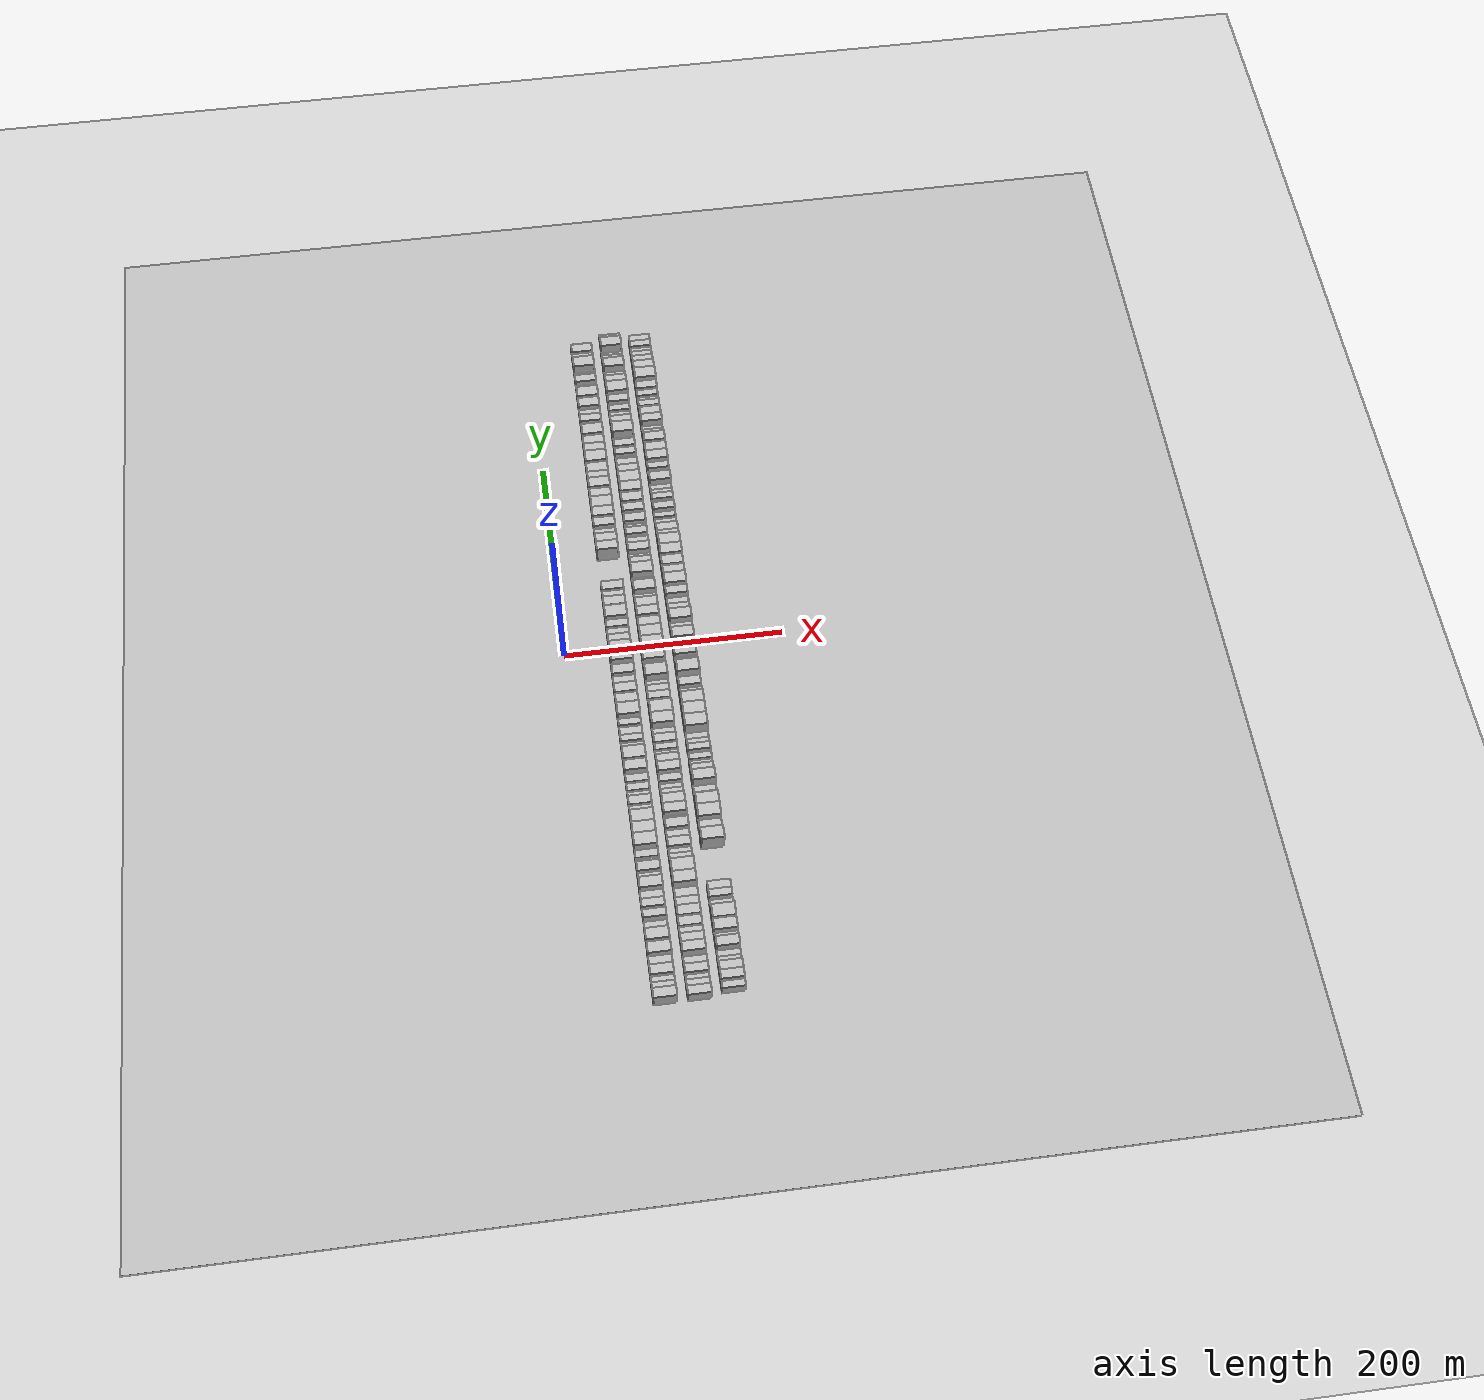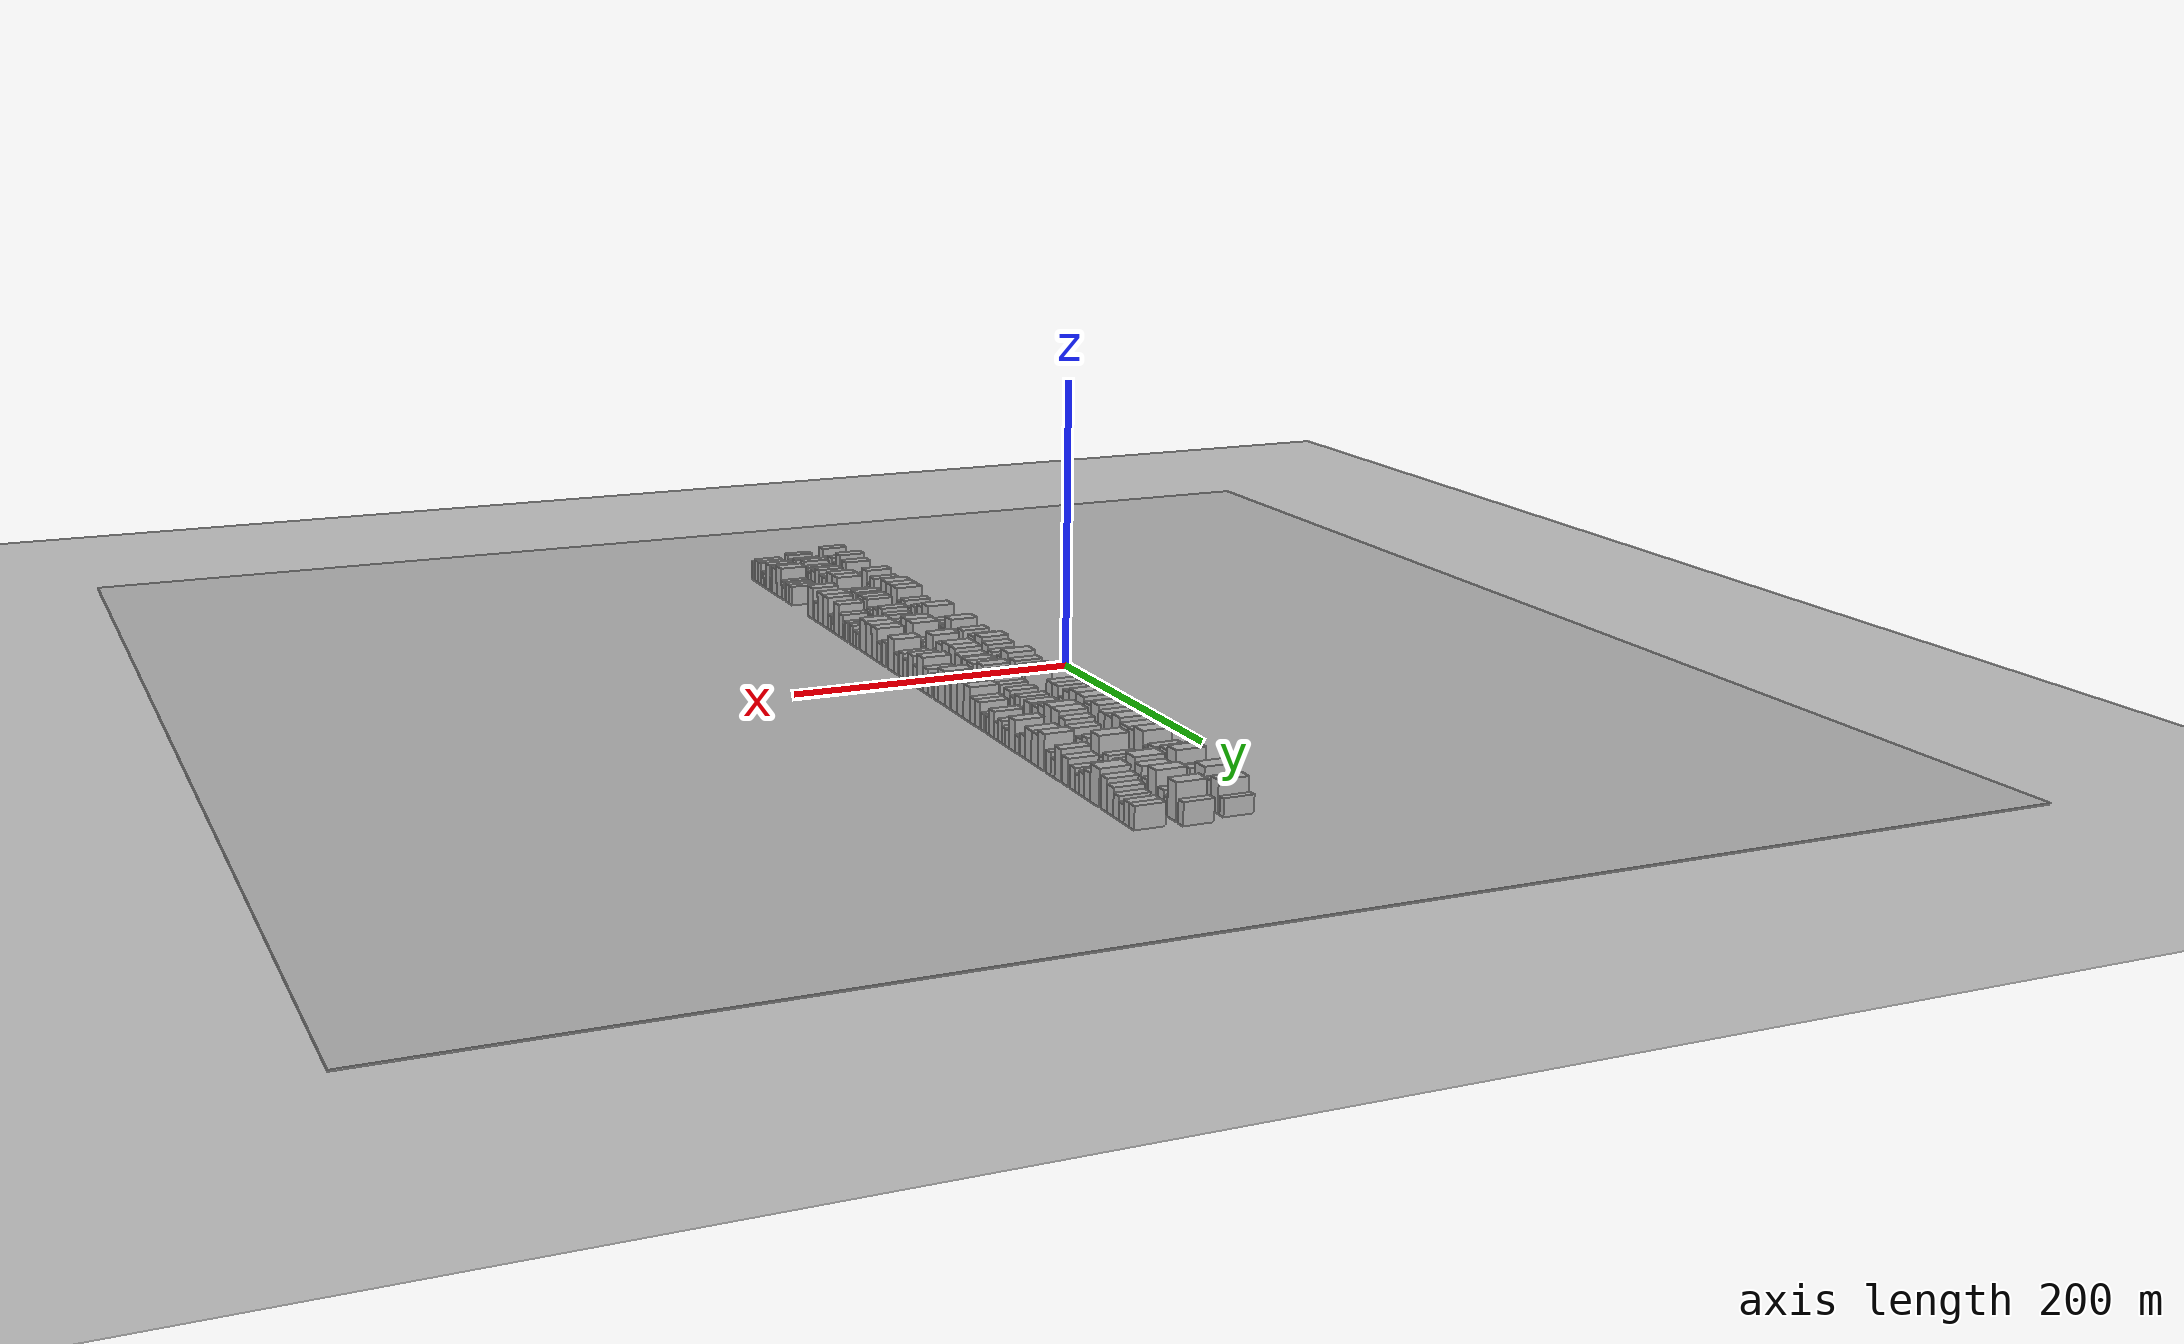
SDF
<?xml version="1.0" encoding="utf-8"?>

<sdf version="1.6">

   <world name="default">

      <gui fullscreen="0">

         <camera name="user_camera">

            <pose>-15 0 4.57585 0 0 0</pose>

            <view_controller>orbit</view_controller>

         </camera>

      </gui>

      <scene>

         <sky>

           <clouds>

             <speed>12</speed>

           </clouds>

         </sky>

         <ambient>0.4 0.4 0.4 1</ambient>

         <background>0.7 0.7 0.7 1</background>

         <shadows>1</shadows>

      </scene>

      <gravity>0 0 -9.8066</gravity>

      <magnetic_field>6e-06 2.3e-05 -4.2e-05</magnetic_field>

      <physics default="0" name="default_physics" type="ode">

         <ode>

            <solver>

               <type>quick</type>

               <iters>10</iters>

               <sor>1.0</sor>

               <use_dynamic_moi_rescaling>0</use_dynamic_moi_rescaling>

            </solver>

            <constraints>

               <cfm>0</cfm>

               <erp>0.2</erp>

               <contact_max_correcting_vel>100</contact_max_correcting_vel>

               <contact_surface_layer>0.001</contact_surface_layer>

            </constraints>

         </ode>

         <max_step_size>0.004</max_step_size>

         <real_time_factor>1</real_time_factor>

         <real_time_update_rate>250</real_time_update_rate>

      </physics>

      <light name="sun" type="directional">

         <cast_shadows>1</cast_shadows>

         <pose>0 0 10 0 0 0</pose>

         <diffuse>0.8 0.8 0.8 1</diffuse>

         <specular>0.2 0.2 0.2 1</specular>

         <attenuation>

            <range>1000</range>

            <constant>0.9</constant>

            <linear>0.01</linear>

            <quadratic>0.001</quadratic>

         </attenuation>

         <direction>-0.5 0.1 -0.9</direction>

      </light>

      <include>

         <name>ground_plane_1</name>

         <uri>model://HANNAS_ground_plane</uri>

         <pose>0 0 0  0 0 0</pose>

      </include>

      <include>

         <name>ground_plane_2</name>

         <uri>model://HANNAS_ground_plane</uri>

         <pose>100 0 0  0 0 0</pose>

      </include>

      <model name="building_1">

         <static>1</static>

         <pose frame="">50.0000 -331.6400 0 0.000000 0.000000 0.000000</pose>

         <link name="link">

            <pose frame="">0 0 10.50 0 0 0</pose>

            <collision name="collision">

               <geometry>

                  <box>

                     <size>20.0000 8.7200 21.0000</size>

                  </box>

               </geometry>

               <max_contacts>10</max_contacts>

               <surface>

                  <contact>

                     <ode/>

                  </contact>

                  <bounce/>

                  <friction>

                     <torsional>

                        <ode/>

                     </torsional>

                     <ode/>

                  </friction>

               </surface>

            </collision>

            <visual name="visual">

               <cast_shadows>0</cast_shadows>

               <geometry>

                  <box>

                     <size>20.0000 8.7200 21.0000</size>

                  </box>

               </geometry>

               <material>

                  <script>

                     <uri>model://HANNAS_wall/materials/scripts</uri>

                     <uri>model://HANNAS_wall/materials/textures</uri>

                     <name>vrc/HANNAS_wall</name>

                  </script>

               </material>

            </visual>

            <self_collide>0</self_collide>

            <enable_wind>0</enable_wind>

            <kinematic>0</kinematic>

         </link>

      </model>

      <model name="building_2">

         <static>1</static>

         <pose frame="">50.0000 -323.9423 0 0.000000 0.000000 0.000000</pose>

         <link name="link">

            <pose frame="">0 0 7.50 0 0 0</pose>

            <collision name="collision">

               <geometry>

                  <box>

                     <size>20.0000 6.6754 15.0000</size>

                  </box>

               </geometry>

               <max_contacts>10</max_contacts>

               <surface>

                  <contact>

                     <ode/>

                  </contact>

                  <bounce/>

                  <friction>

                     <torsional>

                        <ode/>

                     </torsional>

                     <ode/>

                  </friction>

               </surface>

            </collision>

            <visual name="visual">

               <cast_shadows>0</cast_shadows>

               <geometry>

                  <box>

                     <size>20.0000 6.6754 15.0000</size>

                  </box>

               </geometry>

               <material>

                  <script>

                     <uri>model://HANNAS_wall/materials/scripts</uri>

                     <uri>model://HANNAS_wall/materials/textures</uri>

                     <name>vrc/HANNAS_wall</name>

                  </script>

               </material>

            </visual>

            <self_collide>0</self_collide>

            <enable_wind>0</enable_wind>

            <kinematic>0</kinematic>

         </link>

      </model>

      <model name="building_3">

         <static>1</static>

         <pose frame="">50.0000 -317.1755 0 0.000000 0.000000 0.000000</pose>

         <link name="link">

            <pose frame="">0 0 6.00 0 0 0</pose>

            <collision name="collision">

               <geometry>

                  <box>

                     <size>20.0000 4.8581 12.0000</size>

                  </box>

               </geometry>

               <max_contacts>10</max_contacts>

               <surface>

                  <contact>

                     <ode/>

                  </contact>

                  <bounce/>

                  <friction>

                     <torsional>

                        <ode/>

                     </torsional>

                     <ode/>

                  </friction>

               </surface>

            </collision>

            <visual name="visual">

               <cast_shadows>0</cast_shadows>

               <geometry>

                  <box>

                     <size>20.0000 4.8581 12.0000</size>

                  </box>

               </geometry>

               <material>

                  <script>

                     <uri>model://HANNAS_wall/materials/scripts</uri>

                     <uri>model://HANNAS_wall/materials/textures</uri>

                     <name>vrc/HANNAS_wall</name>

                  </script>

               </material>

            </visual>

            <self_collide>0</self_collide>

            <enable_wind>0</enable_wind>

            <kinematic>0</kinematic>

         </link>

      </model>

      <model name="building_4">

         <static>1</static>

         <pose frame="">50.0000 -310.3629 0 0.000000 0.000000 0.000000</pose>

         <link name="link">

            <pose frame="">0 0 9.00 0 0 0</pose>

            <collision name="collision">

               <geometry>

                  <box>

                     <size>20.0000 8.7672 18.0000</size>

                  </box>

               </geometry>

               <max_contacts>10</max_contacts>

               <surface>

                  <contact>

                     <ode/>

                  </contact>

                  <bounce/>

                  <friction>

                     <torsional>

                        <ode/>

                     </torsional>

                     <ode/>

                  </friction>

               </surface>

            </collision>

            <visual name="visual">

               <cast_shadows>0</cast_shadows>

               <geometry>

                  <box>

                     <size>20.0000 8.7672 18.0000</size>

                  </box>

               </geometry>

               <material>

                  <script>

                     <uri>model://HANNAS_wall/materials/scripts</uri>

                     <uri>model://HANNAS_wall/materials/textures</uri>

                     <name>vrc/HANNAS_wall</name>

                  </script>

               </material>

            </visual>

            <self_collide>0</self_collide>

            <enable_wind>0</enable_wind>

            <kinematic>0</kinematic>

         </link>

      </model>

      <model name="building_5">

         <static>1</static>

         <pose frame="">50.0000 -301.4935 0 0.000000 0.000000 0.000000</pose>

         <link name="link">

            <pose frame="">0 0 7.50 0 0 0</pose>

            <collision name="collision">

               <geometry>

                  <box>

                     <size>20.0000 6.9716 15.0000</size>

                  </box>

               </geometry>

               <max_contacts>10</max_contacts>

               <surface>

                  <contact>

                     <ode/>

                  </contact>

                  <bounce/>

                  <friction>

                     <torsional>

                        <ode/>

                     </torsional>

                     <ode/>

                  </friction>

               </surface>

            </collision>

            <visual name="visual">

               <cast_shadows>0</cast_shadows>

               <geometry>

                  <box>

                     <size>20.0000 6.9716 15.0000</size>

                  </box>

               </geometry>

               <material>

                  <script>

                     <uri>model://HANNAS_wall/materials/scripts</uri>

                     <uri>model://HANNAS_wall/materials/textures</uri>

                     <name>vrc/HANNAS_wall</name>

                  </script>

               </material>

            </visual>

            <self_collide>0</self_collide>

            <enable_wind>0</enable_wind>

            <kinematic>0</kinematic>

         </link>

      </model>

      <model name="building_6">

         <static>1</static>

         <pose frame="">50.0000 -293.0491 0 0.000000 0.000000 0.000000</pose>

         <link name="link">

            <pose frame="">0 0 12.00 0 0 0</pose>

            <collision name="collision">

               <geometry>

                  <box>

                     <size>20.0000 9.9170 24.0000</size>

                  </box>

               </geometry>

               <max_contacts>10</max_contacts>

               <surface>

                  <contact>

                     <ode/>

                  </contact>

                  <bounce/>

                  <friction>

                     <torsional>

                        <ode/>

                     </torsional>

                     <ode/>

                  </friction>

               </surface>

            </collision>

            <visual name="visual">

               <cast_shadows>0</cast_shadows>

               <geometry>

                  <box>

                     <size>20.0000 9.9170 24.0000</size>

                  </box>

               </geometry>

               <material>

                  <script>

                     <uri>model://HANNAS_wall/materials/scripts</uri>

                     <uri>model://HANNAS_wall/materials/textures</uri>

                     <name>vrc/HANNAS_wall</name>

                  </script>

               </material>

            </visual>

            <self_collide>0</self_collide>

            <enable_wind>0</enable_wind>

            <kinematic>0</kinematic>

         </link>

      </model>

      <model name="building_7">

         <static>1</static>

         <pose frame="">50.0000 -280.0020 0 0.000000 0.000000 0.000000</pose>

         <link name="link">

            <pose frame="">0 0 10.50 0 0 0</pose>

            <collision name="collision">

               <geometry>

                  <box>

                     <size>20.0000 10.1773 21.0000</size>

                  </box>

               </geometry>

               <max_contacts>10</max_contacts>

               <surface>

                  <contact>

                     <ode/>

                  </contact>

                  <bounce/>

                  <friction>

                     <torsional>

                        <ode/>

                     </torsional>

                     <ode/>

                  </friction>

               </surface>

            </collision>

            <visual name="visual">

               <cast_shadows>0</cast_shadows>

               <geometry>

                  <box>

                     <size>20.0000 10.1773 21.0000</size>

                  </box>

               </geometry>

               <material>

                  <script>

                     <uri>model://HANNAS_wall/materials/scripts</uri>

                     <uri>model://HANNAS_wall/materials/textures</uri>

                     <name>vrc/HANNAS_wall</name>

                  </script>

               </material>

            </visual>

            <self_collide>0</self_collide>

            <enable_wind>0</enable_wind>

            <kinematic>0</kinematic>

         </link>

      </model>

      <model name="building_8">

         <static>1</static>

         <pose frame="">50.0000 -269.1246 0 0.000000 0.000000 0.000000</pose>

         <link name="link">

            <pose frame="">0 0 6.00 0 0 0</pose>

            <collision name="collision">

               <geometry>

                  <box>

                     <size>20.0000 5.5774 12.0000</size>

                  </box>

               </geometry>

               <max_contacts>10</max_contacts>

               <surface>

                  <contact>

                     <ode/>

                  </contact>

                  <bounce/>

                  <friction>

                     <torsional>

                        <ode/>

                     </torsional>

                     <ode/>

                  </friction>

               </surface>

            </collision>

            <visual name="visual">

               <cast_shadows>0</cast_shadows>

               <geometry>

                  <box>

                     <size>20.0000 5.5774 12.0000</size>

                  </box>

               </geometry>

               <material>

                  <script>

                     <uri>model://HANNAS_wall/materials/scripts</uri>

                     <uri>model://HANNAS_wall/materials/textures</uri>

                     <name>vrc/HANNAS_wall</name>

                  </script>

               </material>

            </visual>

            <self_collide>0</self_collide>

            <enable_wind>0</enable_wind>

            <kinematic>0</kinematic>

         </link>

      </model>

      <model name="building_9">

         <static>1</static>

         <pose frame="">50.0000 -259.6852 0 0.000000 0.000000 0.000000</pose>

         <link name="link">

            <pose frame="">0 0 7.50 0 0 0</pose>

            <collision name="collision">

               <geometry>

                  <box>

                     <size>20.0000 7.3014 15.0000</size>

                  </box>

               </geometry>

               <max_contacts>10</max_contacts>

               <surface>

                  <contact>

                     <ode/>

                  </contact>

                  <bounce/>

                  <friction>

                     <torsional>

                        <ode/>

                     </torsional>

                     <ode/>

                  </friction>

               </surface>

            </collision>

            <visual name="visual">

               <cast_shadows>0</cast_shadows>

               <geometry>

                  <box>

                     <size>20.0000 7.3014 15.0000</size>

                  </box>

               </geometry>

               <material>

                  <script>

                     <uri>model://HANNAS_wall/materials/scripts</uri>

                     <uri>model://HANNAS_wall/materials/textures</uri>

                     <name>vrc/HANNAS_wall</name>

                  </script>

               </material>

            </visual>

            <self_collide>0</self_collide>

            <enable_wind>0</enable_wind>

            <kinematic>0</kinematic>

         </link>

      </model>

      <model name="building_10">

         <static>1</static>

         <pose frame="">50.0000 -250.3015 0 0.000000 0.000000 0.000000</pose>

         <link name="link">

            <pose frame="">0 0 7.50 0 0 0</pose>

            <collision name="collision">

               <geometry>

                  <box>

                     <size>20.0000 7.4660 15.0000</size>

                  </box>

               </geometry>

               <max_contacts>10</max_contacts>

               <surface>

                  <contact>

                     <ode/>

                  </contact>

                  <bounce/>

                  <friction>

                     <torsional>

                        <ode/>

                     </torsional>

                     <ode/>

                  </friction>

               </surface>

            </collision>

            <visual name="visual">

               <cast_shadows>0</cast_shadows>

               <geometry>

                  <box>

                     <size>20.0000 7.4660 15.0000</size>

                  </box>

               </geometry>

               <material>

                  <script>

                     <uri>model://HANNAS_wall/materials/scripts</uri>

                     <uri>model://HANNAS_wall/materials/textures</uri>

                     <name>vrc/HANNAS_wall</name>

                  </script>

               </material>

            </visual>

            <self_collide>0</self_collide>

            <enable_wind>0</enable_wind>

            <kinematic>0</kinematic>

         </link>

      </model>

      <model name="building_11">

         <static>1</static>

         <pose frame="">50.0000 -243.1698 0 0.000000 0.000000 0.000000</pose>

         <link name="link">

            <pose frame="">0 0 7.50 0 0 0</pose>

            <collision name="collision">

               <geometry>

                  <box>

                     <size>20.0000 6.7973 15.0000</size>

                  </box>

               </geometry>

               <max_contacts>10</max_contacts>

               <surface>

                  <contact>

                     <ode/>

                  </contact>

                  <bounce/>

                  <friction>

                     <torsional>

                        <ode/>

                     </torsional>

                     <ode/>

                  </friction>

               </surface>

            </collision>

            <visual name="visual">

               <cast_shadows>0</cast_shadows>

               <geometry>

                  <box>

                     <size>20.0000 6.7973 15.0000</size>

                  </box>

               </geometry>

               <material>

                  <script>

                     <uri>model://HANNAS_wall/materials/scripts</uri>

                     <uri>model://HANNAS_wall/materials/textures</uri>

                     <name>vrc/HANNAS_wall</name>

                  </script>

               </material>

            </visual>

            <self_collide>0</self_collide>

            <enable_wind>0</enable_wind>

            <kinematic>0</kinematic>

         </link>

      </model>

      <model name="building_12">

         <static>1</static>

         <pose frame="">50.0000 -234.9150 0 0.000000 0.000000 0.000000</pose>

         <link name="link">

            <pose frame="">0 0 12.00 0 0 0</pose>

            <collision name="collision">

               <geometry>

                  <box>

                     <size>20.0000 9.7123 24.0000</size>

                  </box>

               </geometry>

               <max_contacts>10</max_contacts>

               <surface>

                  <contact>

                     <ode/>

                  </contact>

                  <bounce/>

                  <friction>

                     <torsional>

                        <ode/>

                     </torsional>

                     <ode/>

                  </friction>

               </surface>

            </collision>

            <visual name="visual">

               <cast_shadows>0</cast_shadows>

               <geometry>

                  <box>

                     <size>20.0000 9.7123 24.0000</size>

                  </box>

               </geometry>

               <material>

                  <script>

                     <uri>model://HANNAS_wall/materials/scripts</uri>

                     <uri>model://HANNAS_wall/materials/textures</uri>

                     <name>vrc/HANNAS_wall</name>

                  </script>

               </material>

            </visual>

            <self_collide>0</self_collide>

            <enable_wind>0</enable_wind>

            <kinematic>0</kinematic>

         </link>

      </model>

      <model name="building_13">

         <static>1</static>

         <pose frame="">50.0000 -226.7596 0 0.000000 0.000000 0.000000</pose>

         <link name="link">

            <pose frame="">0 0 7.50 0 0 0</pose>

            <collision name="collision">

               <geometry>

                  <box>

                     <size>20.0000 6.5986 15.0000</size>

                  </box>

               </geometry>

               <max_contacts>10</max_contacts>

               <surface>

                  <contact>

                     <ode/>

                  </contact>

                  <bounce/>

                  <friction>

                     <torsional>

                        <ode/>

                     </torsional>

                     <ode/>

                  </friction>

               </surface>

            </collision>

            <visual name="visual">

               <cast_shadows>0</cast_shadows>

               <geometry>

                  <box>

                     <size>20.0000 6.5986 15.0000</size>

                  </box>

               </geometry>

               <material>

                  <script>

                     <uri>model://HANNAS_wall/materials/scripts</uri>

                     <uri>model://HANNAS_wall/materials/textures</uri>

                     <name>vrc/HANNAS_wall</name>

                  </script>

               </material>

            </visual>

            <self_collide>0</self_collide>

            <enable_wind>0</enable_wind>

            <kinematic>0</kinematic>

         </link>

      </model>

      <model name="building_14">

         <static>1</static>

         <pose frame="">50.0000 -219.0943 0 0.000000 0.000000 0.000000</pose>

         <link name="link">

            <pose frame="">0 0 10.50 0 0 0</pose>

            <collision name="collision">

               <geometry>

                  <box>

                     <size>20.0000 8.7320 21.0000</size>

                  </box>

               </geometry>

               <max_contacts>10</max_contacts>

               <surface>

                  <contact>

                     <ode/>

                  </contact>

                  <bounce/>

                  <friction>

                     <torsional>

                        <ode/>

                     </torsional>

                     <ode/>

                  </friction>

               </surface>

            </collision>

            <visual name="visual">

               <cast_shadows>0</cast_shadows>

               <geometry>

                  <box>

                     <size>20.0000 8.7320 21.0000</size>

                  </box>

               </geometry>

               <material>

                  <script>

                     <uri>model://HANNAS_wall/materials/scripts</uri>

                     <uri>model://HANNAS_wall/materials/textures</uri>

                     <name>vrc/HANNAS_wall</name>

                  </script>

               </material>

            </visual>

            <self_collide>0</self_collide>

            <enable_wind>0</enable_wind>

            <kinematic>0</kinematic>

         </link>

      </model>

      <model name="building_15">

         <static>1</static>

         <pose frame="">50.0000 -212.0358 0 0.000000 0.000000 0.000000</pose>

         <link name="link">

            <pose frame="">0 0 6.00 0 0 0</pose>

            <collision name="collision">

               <geometry>

                  <box>

                     <size>20.0000 5.3851 12.0000</size>

                  </box>

               </geometry>

               <max_contacts>10</max_contacts>

               <surface>

                  <contact>

                     <ode/>

                  </contact>

                  <bounce/>

                  <friction>

                     <torsional>

                        <ode/>

                     </torsional>

                     <ode/>

                  </friction>

               </surface>

            </collision>

            <visual name="visual">

               <cast_shadows>0</cast_shadows>

               <geometry>

                  <box>

                     <size>20.0000 5.3851 12.0000</size>

                  </box>

               </geometry>

               <material>

                  <script>

                     <uri>model://HANNAS_wall/materials/scripts</uri>

                     <uri>model://HANNAS_wall/materials/textures</uri>

                     <name>vrc/HANNAS_wall</name>

                  </script>

               </material>

            </visual>

            <self_collide>0</self_collide>

            <enable_wind>0</enable_wind>

            <kinematic>0</kinematic>

         </link>

      </model>

      <model name="building_16">

         <static>1</static>

         <pose frame="">50.0000 -205.7659 0 0.000000 0.000000 0.000000</pose>

         <link name="link">

            <pose frame="">0 0 7.50 0 0 0</pose>

            <collision name="collision">

               <geometry>

                  <box>

                     <size>20.0000 7.1548 15.0000</size>

                  </box>

               </geometry>

               <max_contacts>10</max_contacts>

               <surface>

                  <contact>

                     <ode/>

                  </contact>

                  <bounce/>

                  <friction>

                     <torsional>

                        <ode/>

                     </torsional>

                     <ode/>

                  </friction>

               </surface>

            </collision>

            <visual name="visual">

               <cast_shadows>0</cast_shadows>

               <geometry>

                  <box>

                     <size>20.0000 7.1548 15.0000</size>

                  </box>

               </geometry>

               <material>

                  <script>

                     <uri>model://HANNAS_wall/materials/scripts</uri>

                     <uri>model://HANNAS_wall/materials/textures</uri>

                     <name>vrc/HANNAS_wall</name>

                  </script>

               </material>

            </visual>

            <self_collide>0</self_collide>

            <enable_wind>0</enable_wind>

            <kinematic>0</kinematic>

         </link>

      </model>

      <model name="building_17">

         <static>1</static>

         <pose frame="">50.0000 -195.3583 0 0.000000 0.000000 0.000000</pose>

         <link name="link">

            <pose frame="">0 0 12.00 0 0 0</pose>

            <collision name="collision">

               <geometry>

                  <box>

                     <size>20.0000 11.6603 24.0000</size>

                  </box>

               </geometry>

               <max_contacts>10</max_contacts>

               <surface>

                  <contact>

                     <ode/>

                  </contact>

                  <bounce/>

                  <friction>

                     <torsional>

                        <ode/>

                     </torsional>

                     <ode/>

                  </friction>

               </surface>

            </collision>

            <visual name="visual">

               <cast_shadows>0</cast_shadows>

               <geometry>

                  <box>

                     <size>20.0000 11.6603 24.0000</size>

                  </box>

               </geometry>

               <material>

                  <script>

                     <uri>model://HANNAS_wall/materials/scripts</uri>

                     <uri>model://HANNAS_wall/materials/textures</uri>

                     <name>vrc/HANNAS_wall</name>

                  </script>

               </material>

            </visual>

            <self_collide>0</self_collide>

            <enable_wind>0</enable_wind>

            <kinematic>0</kinematic>

         </link>

      </model>

      <model name="building_18">

         <static>1</static>

         <pose frame="">50.0000 -184.3350 0 0.000000 0.000000 0.000000</pose>

         <link name="link">

            <pose frame="">0 0 12.00 0 0 0</pose>

            <collision name="collision">

               <geometry>

                  <box>

                     <size>20.0000 10.3863 24.0000</size>

                  </box>

               </geometry>

               <max_contacts>10</max_contacts>

               <surface>

                  <contact>

                     <ode/>

                  </contact>

                  <bounce/>

                  <friction>

                     <torsional>

                        <ode/>

                     </torsional>

                     <ode/>

                  </friction>

               </surface>

            </collision>

            <visual name="visual">

               <cast_shadows>0</cast_shadows>

               <geometry>

                  <box>

                     <size>20.0000 10.3863 24.0000</size>

                  </box>

               </geometry>

               <material>

                  <script>

                     <uri>model://HANNAS_wall/materials/scripts</uri>

                     <uri>model://HANNAS_wall/materials/textures</uri>

                     <name>vrc/HANNAS_wall</name>

                  </script>

               </material>

            </visual>

            <self_collide>0</self_collide>

            <enable_wind>0</enable_wind>

            <kinematic>0</kinematic>

         </link>

      </model>

      <model name="building_19">

         <static>1</static>

         <pose frame="">50.0000 -173.5306 0 0.000000 0.000000 0.000000</pose>

         <link name="link">

            <pose frame="">0 0 12.00 0 0 0</pose>

            <collision name="collision">

               <geometry>

                  <box>

                     <size>20.0000 11.2227 24.0000</size>

                  </box>

               </geometry>

               <max_contacts>10</max_contacts>

               <surface>

                  <contact>

                     <ode/>

                  </contact>

                  <bounce/>

                  <friction>

                     <torsional>

                        <ode/>

                     </torsional>

                     <ode/>

                  </friction>

               </surface>

            </collision>

            <visual name="visual">

               <cast_shadows>0</cast_shadows>

               <geometry>

                  <box>

                     <size>20.0000 11.2227 24.0000</size>

                  </box>

               </geometry>

               <material>

                  <script>

                     <uri>model://HANNAS_wall/materials/scripts</uri>

                     <uri>model://HANNAS_wall/materials/textures</uri>

                     <name>vrc/HANNAS_wall</name>

                  </script>

               </material>

            </visual>

            <self_collide>0</self_collide>

            <enable_wind>0</enable_wind>

            <kinematic>0</kinematic>

         </link>

      </model>

      <model name="building_20">

         <static>1</static>

         <pose frame="">50.0000 -164.2807 0 0.000000 0.000000 0.000000</pose>

         <link name="link">

            <pose frame="">0 0 7.50 0 0 0</pose>

            <collision name="collision">

               <geometry>

                  <box>

                     <size>20.0000 7.2771 15.0000</size>

                  </box>

               </geometry>

               <max_contacts>10</max_contacts>

               <surface>

                  <contact>

                     <ode/>

                  </contact>

                  <bounce/>

                  <friction>

                     <torsional>

                        <ode/>

                     </torsional>

                     <ode/>

                  </friction>

               </surface>

            </collision>

            <visual name="visual">

               <cast_shadows>0</cast_shadows>

               <geometry>

                  <box>

                     <size>20.0000 7.2771 15.0000</size>

                  </box>

               </geometry>

               <material>

                  <script>

                     <uri>model://HANNAS_wall/materials/scripts</uri>

                     <uri>model://HANNAS_wall/materials/textures</uri>

                     <name>vrc/HANNAS_wall</name>

                  </script>

               </material>

            </visual>

            <self_collide>0</self_collide>

            <enable_wind>0</enable_wind>

            <kinematic>0</kinematic>

         </link>

      </model>

      <model name="building_21">

         <static>1</static>

         <pose frame="">50.0000 -156.4418 0 0.000000 0.000000 0.000000</pose>

         <link name="link">

            <pose frame="">0 0 9.00 0 0 0</pose>

            <collision name="collision">

               <geometry>

                  <box>

                     <size>20.0000 8.4006 18.0000</size>

                  </box>

               </geometry>

               <max_contacts>10</max_contacts>

               <surface>

                  <contact>

                     <ode/>

                  </contact>

                  <bounce/>

                  <friction>

                     <torsional>

                        <ode/>

                     </torsional>

                     <ode/>

                  </friction>

               </surface>

            </collision>

            <visual name="visual">

               <cast_shadows>0</cast_shadows>

               <geometry>

                  <box>

                     <size>20.0000 8.4006 18.0000</size>

                  </box>

               </geometry>

               <material>

                  <script>

                     <uri>model://HANNAS_wall/materials/scripts</uri>

                     <uri>model://HANNAS_wall/materials/textures</uri>

                     <name>vrc/HANNAS_wall</name>

                  </script>

               </material>

            </visual>

            <self_collide>0</self_collide>

            <enable_wind>0</enable_wind>

            <kinematic>0</kinematic>

         </link>

      </model>

      <model name="building_22">

         <static>1</static>

         <pose frame="">50.0000 -149.2605 0 0.000000 0.000000 0.000000</pose>

         <link name="link">

            <pose frame="">0 0 6.00 0 0 0</pose>

            <collision name="collision">

               <geometry>

                  <box>

                     <size>20.0000 5.9621 12.0000</size>

                  </box>

               </geometry>

               <max_contacts>10</max_contacts>

               <surface>

                  <contact>

                     <ode/>

                  </contact>

                  <bounce/>

                  <friction>

                     <torsional>

                        <ode/>

                     </torsional>

                     <ode/>

                  </friction>

               </surface>

            </collision>

            <visual name="visual">

               <cast_shadows>0</cast_shadows>

               <geometry>

                  <box>

                     <size>20.0000 5.9621 12.0000</size>

                  </box>

               </geometry>

               <material>

                  <script>

                     <uri>model://HANNAS_wall/materials/scripts</uri>

                     <uri>model://HANNAS_wall/materials/textures</uri>

                     <name>vrc/HANNAS_wall</name>

                  </script>

               </material>

            </visual>

            <self_collide>0</self_collide>

            <enable_wind>0</enable_wind>

            <kinematic>0</kinematic>

         </link>

      </model>

      <model name="building_23">

         <static>1</static>

         <pose frame="">50.0000 -142.8116 0 0.000000 0.000000 0.000000</pose>

         <link name="link">

            <pose frame="">0 0 7.50 0 0 0</pose>

            <collision name="collision">

               <geometry>

                  <box>

                     <size>20.0000 6.9357 15.0000</size>

                  </box>

               </geometry>

               <max_contacts>10</max_contacts>

               <surface>

                  <contact>

                     <ode/>

                  </contact>

                  <bounce/>

                  <friction>

                     <torsional>

                        <ode/>

                     </torsional>

                     <ode/>

                  </friction>

               </surface>

            </collision>

            <visual name="visual">

               <cast_shadows>0</cast_shadows>

               <geometry>

                  <box>

                     <size>20.0000 6.9357 15.0000</size>

                  </box>

               </geometry>

               <material>

                  <script>

                     <uri>model://HANNAS_wall/materials/scripts</uri>

                     <uri>model://HANNAS_wall/materials/textures</uri>

                     <name>vrc/HANNAS_wall</name>

                  </script>

               </material>

            </visual>

            <self_collide>0</self_collide>

            <enable_wind>0</enable_wind>

            <kinematic>0</kinematic>

         </link>

      </model>

      <model name="building_24">

         <static>1</static>

         <pose frame="">50.0000 -135.6105 0 0.000000 0.000000 0.000000</pose>

         <link name="link">

            <pose frame="">0 0 9.00 0 0 0</pose>

            <collision name="collision">

               <geometry>

                  <box>

                     <size>20.0000 7.4665 18.0000</size>

                  </box>

               </geometry>

               <max_contacts>10</max_contacts>

               <surface>

                  <contact>

                     <ode/>

                  </contact>

                  <bounce/>

                  <friction>

                     <torsional>

                        <ode/>

                     </torsional>

                     <ode/>

                  </friction>

               </surface>

            </collision>

            <visual name="visual">

               <cast_shadows>0</cast_shadows>

               <geometry>

                  <box>

                     <size>20.0000 7.4665 18.0000</size>

                  </box>

               </geometry>

               <material>

                  <script>

                     <uri>model://HANNAS_wall/materials/scripts</uri>

                     <uri>model://HANNAS_wall/materials/textures</uri>

                     <name>vrc/HANNAS_wall</name>

                  </script>

               </material>

            </visual>

            <self_collide>0</self_collide>

            <enable_wind>0</enable_wind>

            <kinematic>0</kinematic>

         </link>

      </model>

      <model name="building_25">

         <static>1</static>

         <pose frame="">50.0000 -123.9901 0 0.000000 0.000000 0.000000</pose>

         <link name="link">

            <pose frame="">0 0 10.50 0 0 0</pose>

            <collision name="collision">

               <geometry>

                  <box>

                     <size>20.0000 9.7743 21.0000</size>

                  </box>

               </geometry>

               <max_contacts>10</max_contacts>

               <surface>

                  <contact>

                     <ode/>

                  </contact>

                  <bounce/>

                  <friction>

                     <torsional>

                        <ode/>

                     </torsional>

                     <ode/>

                  </friction>

               </surface>

            </collision>

            <visual name="visual">

               <cast_shadows>0</cast_shadows>

               <geometry>

                  <box>

                     <size>20.0000 9.7743 21.0000</size>

                  </box>

               </geometry>

               <material>

                  <script>

                     <uri>model://HANNAS_wall/materials/scripts</uri>

                     <uri>model://HANNAS_wall/materials/textures</uri>

                     <name>vrc/HANNAS_wall</name>

                  </script>

               </material>

            </visual>

            <self_collide>0</self_collide>

            <enable_wind>0</enable_wind>

            <kinematic>0</kinematic>

         </link>

      </model>

      <model name="building_26">

         <static>1</static>

         <pose frame="">50.0000 -113.1574 0 0.000000 0.000000 0.000000</pose>

         <link name="link">

            <pose frame="">0 0 12.00 0 0 0</pose>

            <collision name="collision">

               <geometry>

                  <box>

                     <size>20.0000 11.8910 24.0000</size>

                  </box>

               </geometry>

               <max_contacts>10</max_contacts>

               <surface>

                  <contact>

                     <ode/>

                  </contact>

                  <bounce/>

                  <friction>

                     <torsional>

                        <ode/>

                     </torsional>

                     <ode/>

                  </friction>

               </surface>

            </collision>

            <visual name="visual">

               <cast_shadows>0</cast_shadows>

               <geometry>

                  <box>

                     <size>20.0000 11.8910 24.0000</size>

                  </box>

               </geometry>

               <material>

                  <script>

                     <uri>model://HANNAS_wall/materials/scripts</uri>

                     <uri>model://HANNAS_wall/materials/textures</uri>

                     <name>vrc/HANNAS_wall</name>

                  </script>

               </material>

            </visual>

            <self_collide>0</self_collide>

            <enable_wind>0</enable_wind>

            <kinematic>0</kinematic>

         </link>

      </model>

      <model name="building_27">

         <static>1</static>

         <pose frame="">50.0000 -103.7190 0 0.000000 0.000000 0.000000</pose>

         <link name="link">

            <pose frame="">0 0 7.50 0 0 0</pose>

            <collision name="collision">

               <geometry>

                  <box>

                     <size>20.0000 6.9859 15.0000</size>

                  </box>

               </geometry>

               <max_contacts>10</max_contacts>

               <surface>

                  <contact>

                     <ode/>

                  </contact>

                  <bounce/>

                  <friction>

                     <torsional>

                        <ode/>

                     </torsional>

                     <ode/>

                  </friction>

               </surface>

            </collision>

            <visual name="visual">

               <cast_shadows>0</cast_shadows>

               <geometry>

                  <box>

                     <size>20.0000 6.9859 15.0000</size>

                  </box>

               </geometry>

               <material>

                  <script>

                     <uri>model://HANNAS_wall/materials/scripts</uri>

                     <uri>model://HANNAS_wall/materials/textures</uri>

                     <name>vrc/HANNAS_wall</name>

                  </script>

               </material>

            </visual>

            <self_collide>0</self_collide>

            <enable_wind>0</enable_wind>

            <kinematic>0</kinematic>

         </link>

      </model>

      <model name="building_28">

         <static>1</static>

         <pose frame="">50.0000 -95.0902 0 0.000000 0.000000 0.000000</pose>

         <link name="link">

            <pose frame="">0 0 7.50 0 0 0</pose>

            <collision name="collision">

               <geometry>

                  <box>

                     <size>20.0000 6.2716 15.0000</size>

                  </box>

               </geometry>

               <max_contacts>10</max_contacts>

               <surface>

                  <contact>

                     <ode/>

                  </contact>

                  <bounce/>

                  <friction>

                     <torsional>

                        <ode/>

                     </torsional>

                     <ode/>

                  </friction>

               </surface>

            </collision>

            <visual name="visual">

               <cast_shadows>0</cast_shadows>

               <geometry>

                  <box>

                     <size>20.0000 6.2716 15.0000</size>

                  </box>

               </geometry>

               <material>

                  <script>

                     <uri>model://HANNAS_wall/materials/scripts</uri>

                     <uri>model://HANNAS_wall/materials/textures</uri>

                     <name>vrc/HANNAS_wall</name>

                  </script>

               </material>

            </visual>

            <self_collide>0</self_collide>

            <enable_wind>0</enable_wind>

            <kinematic>0</kinematic>

         </link>

      </model>

      <model name="building_29">

         <static>1</static>

         <pose frame="">50.0000 -88.3531 0 0.000000 0.000000 0.000000</pose>

         <link name="link">

            <pose frame="">0 0 7.50 0 0 0</pose>

            <collision name="collision">

               <geometry>

                  <box>

                     <size>20.0000 7.2026 15.0000</size>

                  </box>

               </geometry>

               <max_contacts>10</max_contacts>

               <surface>

                  <contact>

                     <ode/>

                  </contact>

                  <bounce/>

                  <friction>

                     <torsional>

                        <ode/>

                     </torsional>

                     <ode/>

                  </friction>

               </surface>

            </collision>

            <visual name="visual">

               <cast_shadows>0</cast_shadows>

               <geometry>

                  <box>

                     <size>20.0000 7.2026 15.0000</size>

                  </box>

               </geometry>

               <material>

                  <script>

                     <uri>model://HANNAS_wall/materials/scripts</uri>

                     <uri>model://HANNAS_wall/materials/textures</uri>

                     <name>vrc/HANNAS_wall</name>

                  </script>

               </material>

            </visual>

            <self_collide>0</self_collide>

            <enable_wind>0</enable_wind>

            <kinematic>0</kinematic>

         </link>

      </model>

      <model name="building_30">

         <static>1</static>

         <pose frame="">50.0000 -79.4296 0 0.000000 0.000000 0.000000</pose>

         <link name="link">

            <pose frame="">0 0 7.50 0 0 0</pose>

            <collision name="collision">

               <geometry>

                  <box>

                     <size>20.0000 6.6446 15.0000</size>

                  </box>

               </geometry>

               <max_contacts>10</max_contacts>

               <surface>

                  <contact>

                     <ode/>

                  </contact>

                  <bounce/>

                  <friction>

                     <torsional>

                        <ode/>

                     </torsional>

                     <ode/>

                  </friction>

               </surface>

            </collision>

            <visual name="visual">

               <cast_shadows>0</cast_shadows>

               <geometry>

                  <box>

                     <size>20.0000 6.6446 15.0000</size>

                  </box>

               </geometry>

               <material>

                  <script>

                     <uri>model://HANNAS_wall/materials/scripts</uri>

                     <uri>model://HANNAS_wall/materials/textures</uri>

                     <name>vrc/HANNAS_wall</name>

                  </script>

               </material>

            </visual>

            <self_collide>0</self_collide>

            <enable_wind>0</enable_wind>

            <kinematic>0</kinematic>

         </link>

      </model>

      <model name="building_31">

         <static>1</static>

         <pose frame="">50.0000 -70.2010 0 0.000000 0.000000 0.000000</pose>

         <link name="link">

            <pose frame="">0 0 12.00 0 0 0</pose>

            <collision name="collision">

               <geometry>

                  <box>

                     <size>20.0000 11.8125 24.0000</size>

                  </box>

               </geometry>

               <max_contacts>10</max_contacts>

               <surface>

                  <contact>

                     <ode/>

                  </contact>

                  <bounce/>

                  <friction>

                     <torsional>

                        <ode/>

                     </torsional>

                     <ode/>

                  </friction>

               </surface>

            </collision>

            <visual name="visual">

               <cast_shadows>0</cast_shadows>

               <geometry>

                  <box>

                     <size>20.0000 11.8125 24.0000</size>

                  </box>

               </geometry>

               <material>

                  <script>

                     <uri>model://HANNAS_wall/materials/scripts</uri>

                     <uri>model://HANNAS_wall/materials/textures</uri>

                     <name>vrc/HANNAS_wall</name>

                  </script>

               </material>

            </visual>

            <self_collide>0</self_collide>

            <enable_wind>0</enable_wind>

            <kinematic>0</kinematic>

         </link>

      </model>

      <model name="building_32">

         <static>1</static>

         <pose frame="">50.0000 -56.8380 0 0.000000 0.000000 0.000000</pose>

         <link name="link">

            <pose frame="">0 0 9.00 0 0 0</pose>

            <collision name="collision">

               <geometry>

                  <box>

                     <size>20.0000 8.9135 18.0000</size>

                  </box>

               </geometry>

               <max_contacts>10</max_contacts>

               <surface>

                  <contact>

                     <ode/>

                  </contact>

                  <bounce/>

                  <friction>

                     <torsional>

                        <ode/>

                     </torsional>

                     <ode/>

                  </friction>

               </surface>

            </collision>

            <visual name="visual">

               <cast_shadows>0</cast_shadows>

               <geometry>

                  <box>

                     <size>20.0000 8.9135 18.0000</size>

                  </box>

               </geometry>

               <material>

                  <script>

                     <uri>model://HANNAS_wall/materials/scripts</uri>

                     <uri>model://HANNAS_wall/materials/textures</uri>

                     <name>vrc/HANNAS_wall</name>

                  </script>

               </material>

            </visual>

            <self_collide>0</self_collide>

            <enable_wind>0</enable_wind>

            <kinematic>0</kinematic>

         </link>

      </model>

      <model name="building_33">

         <static>1</static>

         <pose frame="">50.0000 -47.8218 0 0.000000 0.000000 0.000000</pose>

         <link name="link">

            <pose frame="">0 0 10.50 0 0 0</pose>

            <collision name="collision">

               <geometry>

                  <box>

                     <size>20.0000 9.1189 21.0000</size>

                  </box>

               </geometry>

               <max_contacts>10</max_contacts>

               <surface>

                  <contact>

                     <ode/>

                  </contact>

                  <bounce/>

                  <friction>

                     <torsional>

                        <ode/>

                     </torsional>

                     <ode/>

                  </friction>

               </surface>

            </collision>

            <visual name="visual">

               <cast_shadows>0</cast_shadows>

               <geometry>

                  <box>

                     <size>20.0000 9.1189 21.0000</size>

                  </box>

               </geometry>

               <material>

                  <script>

                     <uri>model://HANNAS_wall/materials/scripts</uri>

                     <uri>model://HANNAS_wall/materials/textures</uri>

                     <name>vrc/HANNAS_wall</name>

                  </script>

               </material>

            </visual>

            <self_collide>0</self_collide>

            <enable_wind>0</enable_wind>

            <kinematic>0</kinematic>

         </link>

      </model>

      <model name="building_34">

         <static>1</static>

         <pose frame="">50.0000 -37.0058 0 0.000000 0.000000 0.000000</pose>

         <link name="link">

            <pose frame="">0 0 7.50 0 0 0</pose>

            <collision name="collision">

               <geometry>

                  <box>

                     <size>20.0000 6.5132 15.0000</size>

                  </box>

               </geometry>

               <max_contacts>10</max_contacts>

               <surface>

                  <contact>

                     <ode/>

                  </contact>

                  <bounce/>

                  <friction>

                     <torsional>

                        <ode/>

                     </torsional>

                     <ode/>

                  </friction>

               </surface>

            </collision>

            <visual name="visual">

               <cast_shadows>0</cast_shadows>

               <geometry>

                  <box>

                     <size>20.0000 6.5132 15.0000</size>

                  </box>

               </geometry>

               <material>

                  <script>

                     <uri>model://HANNAS_wall/materials/scripts</uri>

                     <uri>model://HANNAS_wall/materials/textures</uri>

                     <name>vrc/HANNAS_wall</name>

                  </script>

               </material>

            </visual>

            <self_collide>0</self_collide>

            <enable_wind>0</enable_wind>

            <kinematic>0</kinematic>

         </link>

      </model>

      <model name="building_35">

         <static>1</static>

         <pose frame="">50.0000 -29.0701 0 0.000000 0.000000 0.000000</pose>

         <link name="link">

            <pose frame="">0 0 10.50 0 0 0</pose>

            <collision name="collision">

               <geometry>

                  <box>

                     <size>20.0000 9.3582 21.0000</size>

                  </box>

               </geometry>

               <max_contacts>10</max_contacts>

               <surface>

                  <contact>

                     <ode/>

                  </contact>

                  <bounce/>

                  <friction>

                     <torsional>

                        <ode/>

                     </torsional>

                     <ode/>

                  </friction>

               </surface>

            </collision>

            <visual name="visual">

               <cast_shadows>0</cast_shadows>

               <geometry>

                  <box>

                     <size>20.0000 9.3582 21.0000</size>

                  </box>

               </geometry>

               <material>

                  <script>

                     <uri>model://HANNAS_wall/materials/scripts</uri>

                     <uri>model://HANNAS_wall/materials/textures</uri>

                     <name>vrc/HANNAS_wall</name>

                  </script>

               </material>

            </visual>

            <self_collide>0</self_collide>

            <enable_wind>0</enable_wind>

            <kinematic>0</kinematic>

         </link>

      </model>

      <model name="building_36">

         <static>1</static>

         <pose frame="">50.0000 -15.8890 0 0.000000 0.000000 0.000000</pose>

         <link name="link">

            <pose frame="">0 0 12.00 0 0 0</pose>

            <collision name="collision">

               <geometry>

                  <box>

                     <size>20.0000 11.0039 24.0000</size>

                  </box>

               </geometry>

               <max_contacts>10</max_contacts>

               <surface>

                  <contact>

                     <ode/>

                  </contact>

                  <bounce/>

                  <friction>

                     <torsional>

                        <ode/>

                     </torsional>

                     <ode/>

                  </friction>

               </surface>

            </collision>

            <visual name="visual">

               <cast_shadows>0</cast_shadows>

               <geometry>

                  <box>

                     <size>20.0000 11.0039 24.0000</size>

                  </box>

               </geometry>

               <material>

                  <script>

                     <uri>model://HANNAS_wall/materials/scripts</uri>

                     <uri>model://HANNAS_wall/materials/textures</uri>

                     <name>vrc/HANNAS_wall</name>

                  </script>

               </material>

            </visual>

            <self_collide>0</self_collide>

            <enable_wind>0</enable_wind>

            <kinematic>0</kinematic>

         </link>

      </model>

      <model name="building_37">

         <static>1</static>

         <pose frame="">50.0000 -5.2631 0 0.000000 0.000000 0.000000</pose>

         <link name="link">

            <pose frame="">0 0 10.50 0 0 0</pose>

            <collision name="collision">

               <geometry>

                  <box>

                     <size>20.0000 10.2481 21.0000</size>

                  </box>

               </geometry>

               <max_contacts>10</max_contacts>

               <surface>

                  <contact>

                     <ode/>

                  </contact>

                  <bounce/>

                  <friction>

                     <torsional>

                        <ode/>

                     </torsional>

                     <ode/>

                  </friction>

               </surface>

            </collision>

            <visual name="visual">

               <cast_shadows>0</cast_shadows>

               <geometry>

                  <box>

                     <size>20.0000 10.2481 21.0000</size>

                  </box>

               </geometry>

               <material>

                  <script>

                     <uri>model://HANNAS_wall/materials/scripts</uri>

                     <uri>model://HANNAS_wall/materials/textures</uri>

                     <name>vrc/HANNAS_wall</name>

                  </script>

               </material>

            </visual>

            <self_collide>0</self_collide>

            <enable_wind>0</enable_wind>

            <kinematic>0</kinematic>

         </link>

      </model>

      <model name="building_38">

         <static>1</static>

         <pose frame="">50.0000 3.9993 0 0.000000 0.000000 0.000000</pose>

         <link name="link">

            <pose frame="">0 0 9.00 0 0 0</pose>

            <collision name="collision">

               <geometry>

                  <box>

                     <size>20.0000 8.2765 18.0000</size>

                  </box>

               </geometry>

               <max_contacts>10</max_contacts>

               <surface>

                  <contact>

                     <ode/>

                  </contact>

                  <bounce/>

                  <friction>

                     <torsional>

                        <ode/>

                     </torsional>

                     <ode/>

                  </friction>

               </surface>

            </collision>

            <visual name="visual">

               <cast_shadows>0</cast_shadows>

               <geometry>

                  <box>

                     <size>20.0000 8.2765 18.0000</size>

                  </box>

               </geometry>

               <material>

                  <script>

                     <uri>model://HANNAS_wall/materials/scripts</uri>

                     <uri>model://HANNAS_wall/materials/textures</uri>

                     <name>vrc/HANNAS_wall</name>

                  </script>

               </material>

            </visual>

            <self_collide>0</self_collide>

            <enable_wind>0</enable_wind>

            <kinematic>0</kinematic>

         </link>

      </model>

      <model name="building_39">

         <static>1</static>

         <pose frame="">50.0000 11.8371 0 0.000000 0.000000 0.000000</pose>

         <link name="link">

            <pose frame="">0 0 7.50 0 0 0</pose>

            <collision name="collision">

               <geometry>

                  <box>

                     <size>20.0000 7.3991 15.0000</size>

                  </box>

               </geometry>

               <max_contacts>10</max_contacts>

               <surface>

                  <contact>

                     <ode/>

                  </contact>

                  <bounce/>

                  <friction>

                     <torsional>

                        <ode/>

                     </torsional>

                     <ode/>

                  </friction>

               </surface>

            </collision>

            <visual name="visual">

               <cast_shadows>0</cast_shadows>

               <geometry>

                  <box>

                     <size>20.0000 7.3991 15.0000</size>

                  </box>

               </geometry>

               <material>

                  <script>

                     <uri>model://HANNAS_wall/materials/scripts</uri>

                     <uri>model://HANNAS_wall/materials/textures</uri>

                     <name>vrc/HANNAS_wall</name>

                  </script>

               </material>

            </visual>

            <self_collide>0</self_collide>

            <enable_wind>0</enable_wind>

            <kinematic>0</kinematic>

         </link>

      </model>

      <model name="building_40">

         <static>1</static>

         <pose frame="">50.0000 19.3833 0 0.000000 0.000000 0.000000</pose>

         <link name="link">

            <pose frame="">0 0 9.00 0 0 0</pose>

            <collision name="collision">

               <geometry>

                  <box>

                     <size>20.0000 7.6934 18.0000</size>

                  </box>

               </geometry>

               <max_contacts>10</max_contacts>

               <surface>

                  <contact>

                     <ode/>

                  </contact>

                  <bounce/>

                  <friction>

                     <torsional>

                        <ode/>

                     </torsional>

                     <ode/>

                  </friction>

               </surface>

            </collision>

            <visual name="visual">

               <cast_shadows>0</cast_shadows>

               <geometry>

                  <box>

                     <size>20.0000 7.6934 18.0000</size>

                  </box>

               </geometry>

               <material>

                  <script>

                     <uri>model://HANNAS_wall/materials/scripts</uri>

                     <uri>model://HANNAS_wall/materials/textures</uri>

                     <name>vrc/HANNAS_wall</name>

                  </script>

               </material>

            </visual>

            <self_collide>0</self_collide>

            <enable_wind>0</enable_wind>

            <kinematic>0</kinematic>

         </link>

      </model>

      <model name="building_41">

         <static>1</static>

         <pose frame="">50.0000 29.1139 0 0.000000 0.000000 0.000000</pose>

         <link name="link">

            <pose frame="">0 0 12.00 0 0 0</pose>

            <collision name="collision">

               <geometry>

                  <box>

                     <size>20.0000 11.7678 24.0000</size>

                  </box>

               </geometry>

               <max_contacts>10</max_contacts>

               <surface>

                  <contact>

                     <ode/>

                  </contact>

                  <bounce/>

                  <friction>

                     <torsional>

                        <ode/>

                     </torsional>

                     <ode/>

                  </friction>

               </surface>

            </collision>

            <visual name="visual">

               <cast_shadows>0</cast_shadows>

               <geometry>

                  <box>

                     <size>20.0000 11.7678 24.0000</size>

                  </box>

               </geometry>

               <material>

                  <script>

                     <uri>model://HANNAS_wall/materials/scripts</uri>

                     <uri>model://HANNAS_wall/materials/textures</uri>

                     <name>vrc/HANNAS_wall</name>

                  </script>

               </material>

            </visual>

            <self_collide>0</self_collide>

            <enable_wind>0</enable_wind>

            <kinematic>0</kinematic>

         </link>

      </model>

      <model name="building_42">

         <static>1</static>

         <pose frame="">50.0000 41.4578 0 0.000000 0.000000 0.000000</pose>

         <link name="link">

            <pose frame="">0 0 10.50 0 0 0</pose>

            <collision name="collision">

               <geometry>

                  <box>

                     <size>20.0000 8.9201 21.0000</size>

                  </box>

               </geometry>

               <max_contacts>10</max_contacts>

               <surface>

                  <contact>

                     <ode/>

                  </contact>

                  <bounce/>

                  <friction>

                     <torsional>

                        <ode/>

                     </torsional>

                     <ode/>

                  </friction>

               </surface>

            </collision>

            <visual name="visual">

               <cast_shadows>0</cast_shadows>

               <geometry>

                  <box>

                     <size>20.0000 8.9201 21.0000</size>

                  </box>

               </geometry>

               <material>

                  <script>

                     <uri>model://HANNAS_wall/materials/scripts</uri>

                     <uri>model://HANNAS_wall/materials/textures</uri>

                     <name>vrc/HANNAS_wall</name>

                  </script>

               </material>

            </visual>

            <self_collide>0</self_collide>

            <enable_wind>0</enable_wind>

            <kinematic>0</kinematic>

         </link>

      </model>

      <model name="building_43">

         <static>1</static>

         <pose frame="">50.0000 49.5280 0 0.000000 0.000000 0.000000</pose>

         <link name="link">

            <pose frame="">0 0 9.00 0 0 0</pose>

            <collision name="collision">

               <geometry>

                  <box>

                     <size>20.0000 7.2202 18.0000</size>

                  </box>

               </geometry>

               <max_contacts>10</max_contacts>

               <surface>

                  <contact>

                     <ode/>

                  </contact>

                  <bounce/>

                  <friction>

                     <torsional>

                        <ode/>

                     </torsional>

                     <ode/>

                  </friction>

               </surface>

            </collision>

            <visual name="visual">

               <cast_shadows>0</cast_shadows>

               <geometry>

                  <box>

                     <size>20.0000 7.2202 18.0000</size>

                  </box>

               </geometry>

               <material>

                  <script>

                     <uri>model://HANNAS_wall/materials/scripts</uri>

                     <uri>model://HANNAS_wall/materials/textures</uri>

                     <name>vrc/HANNAS_wall</name>

                  </script>

               </material>

            </visual>

            <self_collide>0</self_collide>

            <enable_wind>0</enable_wind>

            <kinematic>0</kinematic>

         </link>

      </model>

      <model name="building_44">

         <static>1</static>

         <pose frame="">50.0000 57.5813 0 0.000000 0.000000 0.000000</pose>

         <link name="link">

            <pose frame="">0 0 10.50 0 0 0</pose>

            <collision name="collision">

               <geometry>

                  <box>

                     <size>20.0000 8.8865 21.0000</size>

                  </box>

               </geometry>

               <max_contacts>10</max_contacts>

               <surface>

                  <contact>

                     <ode/>

                  </contact>

                  <bounce/>

                  <friction>

                     <torsional>

                        <ode/>

                     </torsional>

                     <ode/>

                  </friction>

               </surface>

            </collision>

            <visual name="visual">

               <cast_shadows>0</cast_shadows>

               <geometry>

                  <box>

                     <size>20.0000 8.8865 21.0000</size>

                  </box>

               </geometry>

               <material>

                  <script>

                     <uri>model://HANNAS_wall/materials/scripts</uri>

                     <uri>model://HANNAS_wall/materials/textures</uri>

                     <name>vrc/HANNAS_wall</name>

                  </script>

               </material>

            </visual>

            <self_collide>0</self_collide>

            <enable_wind>0</enable_wind>

            <kinematic>0</kinematic>

         </link>

      </model>

      <model name="building_45">

         <static>1</static>

         <pose frame="">50.0000 100.7493 0 0.000000 0.000000 0.000000</pose>

         <link name="link">

            <pose frame="">0 0 10.50 0 0 0</pose>

            <collision name="collision">

               <geometry>

                  <box>

                     <size>20.0000 9.1498 21.0000</size>

                  </box>

               </geometry>

               <max_contacts>10</max_contacts>

               <surface>

                  <contact>

                     <ode/>

                  </contact>

                  <bounce/>

                  <friction>

                     <torsional>

                        <ode/>

                     </torsional>

                     <ode/>

                  </friction>

               </surface>

            </collision>

            <visual name="visual">

               <cast_shadows>0</cast_shadows>

               <geometry>

                  <box>

                     <size>20.0000 9.1498 21.0000</size>

                  </box>

               </geometry>

               <material>

                  <script>

                     <uri>model://HANNAS_wall/materials/scripts</uri>

                     <uri>model://HANNAS_wall/materials/textures</uri>

                     <name>vrc/HANNAS_wall</name>

                  </script>

               </material>

            </visual>

            <self_collide>0</self_collide>

            <enable_wind>0</enable_wind>

            <kinematic>0</kinematic>

         </link>

      </model>

      <model name="building_46">

         <static>1</static>

         <pose frame="">50.0000 109.5379 0 0.000000 0.000000 0.000000</pose>

         <link name="link">

            <pose frame="">0 0 10.50 0 0 0</pose>

            <collision name="collision">

               <geometry>

                  <box>

                     <size>20.0000 8.4273 21.0000</size>

                  </box>

               </geometry>

               <max_contacts>10</max_contacts>

               <surface>

                  <contact>

                     <ode/>

                  </contact>

                  <bounce/>

                  <friction>

                     <torsional>

                        <ode/>

                     </torsional>

                     <ode/>

                  </friction>

               </surface>

            </collision>

            <visual name="visual">

               <cast_shadows>0</cast_shadows>

               <geometry>

                  <box>

                     <size>20.0000 8.4273 21.0000</size>

                  </box>

               </geometry>

               <material>

                  <script>

                     <uri>model://HANNAS_wall/materials/scripts</uri>

                     <uri>model://HANNAS_wall/materials/textures</uri>

                     <name>vrc/HANNAS_wall</name>

                  </script>

               </material>

            </visual>

            <self_collide>0</self_collide>

            <enable_wind>0</enable_wind>

            <kinematic>0</kinematic>

         </link>

      </model>

      <model name="building_47">

         <static>1</static>

         <pose frame="">50.0000 118.8460 0 0.000000 0.000000 0.000000</pose>

         <link name="link">

            <pose frame="">0 0 7.50 0 0 0</pose>

            <collision name="collision">

               <geometry>

                  <box>

                     <size>20.0000 6.1890 15.0000</size>

                  </box>

               </geometry>

               <max_contacts>10</max_contacts>

               <surface>

                  <contact>

                     <ode/>

                  </contact>

                  <bounce/>

                  <friction>

                     <torsional>

                        <ode/>

                     </torsional>

                     <ode/>

                  </friction>

               </surface>

            </collision>

            <visual name="visual">

               <cast_shadows>0</cast_shadows>

               <geometry>

                  <box>

                     <size>20.0000 6.1890 15.0000</size>

                  </box>

               </geometry>

               <material>

                  <script>

                     <uri>model://HANNAS_wall/materials/scripts</uri>

                     <uri>model://HANNAS_wall/materials/textures</uri>

                     <name>vrc/HANNAS_wall</name>

                  </script>

               </material>

            </visual>

            <self_collide>0</self_collide>

            <enable_wind>0</enable_wind>

            <kinematic>0</kinematic>

         </link>

      </model>

      <model name="building_48">

         <static>1</static>

         <pose frame="">50.0000 126.5604 0 0.000000 0.000000 0.000000</pose>

         <link name="link">

            <pose frame="">0 0 10.50 0 0 0</pose>

            <collision name="collision">

               <geometry>

                  <box>

                     <size>20.0000 9.2399 21.0000</size>

                  </box>

               </geometry>

               <max_contacts>10</max_contacts>

               <surface>

                  <contact>

                     <ode/>

                  </contact>

                  <bounce/>

                  <friction>

                     <torsional>

                        <ode/>

                     </torsional>

                     <ode/>

                  </friction>

               </surface>

            </collision>

            <visual name="visual">

               <cast_shadows>0</cast_shadows>

               <geometry>

                  <box>

                     <size>20.0000 9.2399 21.0000</size>

                  </box>

               </geometry>

               <material>

                  <script>

                     <uri>model://HANNAS_wall/materials/scripts</uri>

                     <uri>model://HANNAS_wall/materials/textures</uri>

                     <name>vrc/HANNAS_wall</name>

                  </script>

               </material>

            </visual>

            <self_collide>0</self_collide>

            <enable_wind>0</enable_wind>

            <kinematic>0</kinematic>

         </link>

      </model>

      <model name="building_49">

         <static>1</static>

         <pose frame="">50.0000 136.3057 0 0.000000 0.000000 0.000000</pose>

         <link name="link">

            <pose frame="">0 0 12.00 0 0 0</pose>

            <collision name="collision">

               <geometry>

                  <box>

                     <size>20.0000 10.2506 24.0000</size>

                  </box>

               </geometry>

               <max_contacts>10</max_contacts>

               <surface>

                  <contact>

                     <ode/>

                  </contact>

                  <bounce/>

                  <friction>

                     <torsional>

                        <ode/>

                     </torsional>

                     <ode/>

                  </friction>

               </surface>

            </collision>

            <visual name="visual">

               <cast_shadows>0</cast_shadows>

               <geometry>

                  <box>

                     <size>20.0000 10.2506 24.0000</size>

                  </box>

               </geometry>

               <material>

                  <script>

                     <uri>model://HANNAS_wall/materials/scripts</uri>

                     <uri>model://HANNAS_wall/materials/textures</uri>

                     <name>vrc/HANNAS_wall</name>

                  </script>

               </material>

            </visual>

            <self_collide>0</self_collide>

            <enable_wind>0</enable_wind>

            <kinematic>0</kinematic>

         </link>

      </model>

      <model name="building_50">

         <static>1</static>

         <pose frame="">50.0000 147.1549 0 0.000000 0.000000 0.000000</pose>

         <link name="link">

            <pose frame="">0 0 12.00 0 0 0</pose>

            <collision name="collision">

               <geometry>

                  <box>

                     <size>20.0000 11.4478 24.0000</size>

                  </box>

               </geometry>

               <max_contacts>10</max_contacts>

               <surface>

                  <contact>

                     <ode/>

                  </contact>

                  <bounce/>

                  <friction>

                     <torsional>

                        <ode/>

                     </torsional>

                     <ode/>

                  </friction>

               </surface>

            </collision>

            <visual name="visual">

               <cast_shadows>0</cast_shadows>

               <geometry>

                  <box>

                     <size>20.0000 11.4478 24.0000</size>

                  </box>

               </geometry>

               <material>

                  <script>

                     <uri>model://HANNAS_wall/materials/scripts</uri>

                     <uri>model://HANNAS_wall/materials/textures</uri>

                     <name>vrc/HANNAS_wall</name>

                  </script>

               </material>

            </visual>

            <self_collide>0</self_collide>

            <enable_wind>0</enable_wind>

            <kinematic>0</kinematic>

         </link>

      </model>

      <model name="building_51">

         <static>1</static>

         <pose frame="">50.0000 158.1207 0 0.000000 0.000000 0.000000</pose>

         <link name="link">

            <pose frame="">0 0 10.50 0 0 0</pose>

            <collision name="collision">

               <geometry>

                  <box>

                     <size>20.0000 10.4837 21.0000</size>

                  </box>

               </geometry>

               <max_contacts>10</max_contacts>

               <surface>

                  <contact>

                     <ode/>

                  </contact>

                  <bounce/>

                  <friction>

                     <torsional>

                        <ode/>

                     </torsional>

                     <ode/>

                  </friction>

               </surface>

            </collision>

            <visual name="visual">

               <cast_shadows>0</cast_shadows>

               <geometry>

                  <box>

                     <size>20.0000 10.4837 21.0000</size>

                  </box>

               </geometry>

               <material>

                  <script>

                     <uri>model://HANNAS_wall/materials/scripts</uri>

                     <uri>model://HANNAS_wall/materials/textures</uri>

                     <name>vrc/HANNAS_wall</name>

                  </script>

               </material>

            </visual>

            <self_collide>0</self_collide>

            <enable_wind>0</enable_wind>

            <kinematic>0</kinematic>

         </link>

      </model>

      <model name="building_52">

         <static>1</static>

         <pose frame="">50.0000 168.6137 0 0.000000 0.000000 0.000000</pose>

         <link name="link">

            <pose frame="">0 0 12.00 0 0 0</pose>

            <collision name="collision">

               <geometry>

                  <box>

                     <size>20.0000 10.5022 24.0000</size>

                  </box>

               </geometry>

               <max_contacts>10</max_contacts>

               <surface>

                  <contact>

                     <ode/>

                  </contact>

                  <bounce/>

                  <friction>

                     <torsional>

                        <ode/>

                     </torsional>

                     <ode/>

                  </friction>

               </surface>

            </collision>

            <visual name="visual">

               <cast_shadows>0</cast_shadows>

               <geometry>

                  <box>

                     <size>20.0000 10.5022 24.0000</size>

                  </box>

               </geometry>

               <material>

                  <script>

                     <uri>model://HANNAS_wall/materials/scripts</uri>

                     <uri>model://HANNAS_wall/materials/textures</uri>

                     <name>vrc/HANNAS_wall</name>

                  </script>

               </material>

            </visual>

            <self_collide>0</self_collide>

            <enable_wind>0</enable_wind>

            <kinematic>0</kinematic>

         </link>

      </model>

      <model name="building_53">

         <static>1</static>

         <pose frame="">50.0000 178.1863 0 0.000000 0.000000 0.000000</pose>

         <link name="link">

            <pose frame="">0 0 10.50 0 0 0</pose>

            <collision name="collision">

               <geometry>

                  <box>

                     <size>20.0000 8.6431 21.0000</size>

                  </box>

               </geometry>

               <max_contacts>10</max_contacts>

               <surface>

                  <contact>

                     <ode/>

                  </contact>

                  <bounce/>

                  <friction>

                     <torsional>

                        <ode/>

                     </torsional>

                     <ode/>

                  </friction>

               </surface>

            </collision>

            <visual name="visual">

               <cast_shadows>0</cast_shadows>

               <geometry>

                  <box>

                     <size>20.0000 8.6431 21.0000</size>

                  </box>

               </geometry>

               <material>

                  <script>

                     <uri>model://HANNAS_wall/materials/scripts</uri>

                     <uri>model://HANNAS_wall/materials/textures</uri>

                     <name>vrc/HANNAS_wall</name>

                  </script>

               </material>

            </visual>

            <self_collide>0</self_collide>

            <enable_wind>0</enable_wind>

            <kinematic>0</kinematic>

         </link>

      </model>

      <model name="building_54">

         <static>1</static>

         <pose frame="">50.0000 187.5377 0 0.000000 0.000000 0.000000</pose>

         <link name="link">

            <pose frame="">0 0 10.50 0 0 0</pose>

            <collision name="collision">

               <geometry>

                  <box>

                     <size>20.0000 10.0596 21.0000</size>

                  </box>

               </geometry>

               <max_contacts>10</max_contacts>

               <surface>

                  <contact>

                     <ode/>

                  </contact>

                  <bounce/>

                  <friction>

                     <torsional>

                        <ode/>

                     </torsional>

                     <ode/>

                  </friction>

               </surface>

            </collision>

            <visual name="visual">

               <cast_shadows>0</cast_shadows>

               <geometry>

                  <box>

                     <size>20.0000 10.0596 21.0000</size>

                  </box>

               </geometry>

               <material>

                  <script>

                     <uri>model://HANNAS_wall/materials/scripts</uri>

                     <uri>model://HANNAS_wall/materials/textures</uri>

                     <name>vrc/HANNAS_wall</name>

                  </script>

               </material>

            </visual>

            <self_collide>0</self_collide>

            <enable_wind>0</enable_wind>

            <kinematic>0</kinematic>

         </link>

      </model>

      <model name="building_55">

         <static>1</static>

         <pose frame="">50.0000 198.5426 0 0.000000 0.000000 0.000000</pose>

         <link name="link">

            <pose frame="">0 0 12.00 0 0 0</pose>

            <collision name="collision">

               <geometry>

                  <box>

                     <size>20.0000 11.9503 24.0000</size>

                  </box>

               </geometry>

               <max_contacts>10</max_contacts>

               <surface>

                  <contact>

                     <ode/>

                  </contact>

                  <bounce/>

                  <friction>

                     <torsional>

                        <ode/>

                     </torsional>

                     <ode/>

                  </friction>

               </surface>

            </collision>

            <visual name="visual">

               <cast_shadows>0</cast_shadows>

               <geometry>

                  <box>

                     <size>20.0000 11.9503 24.0000</size>

                  </box>

               </geometry>

               <material>

                  <script>

                     <uri>model://HANNAS_wall/materials/scripts</uri>

                     <uri>model://HANNAS_wall/materials/textures</uri>

                     <name>vrc/HANNAS_wall</name>

                  </script>

               </material>

            </visual>

            <self_collide>0</self_collide>

            <enable_wind>0</enable_wind>

            <kinematic>0</kinematic>

         </link>

      </model>

      <model name="building_56">

         <static>1</static>

         <pose frame="">50.0000 209.5806 0 0.000000 0.000000 0.000000</pose>

         <link name="link">

            <pose frame="">0 0 10.50 0 0 0</pose>

            <collision name="collision">

               <geometry>

                  <box>

                     <size>20.0000 10.1256 21.0000</size>

                  </box>

               </geometry>

               <max_contacts>10</max_contacts>

               <surface>

                  <contact>

                     <ode/>

                  </contact>

                  <bounce/>

                  <friction>

                     <torsional>

                        <ode/>

                     </torsional>

                     <ode/>

                  </friction>

               </surface>

            </collision>

            <visual name="visual">

               <cast_shadows>0</cast_shadows>

               <geometry>

                  <box>

                     <size>20.0000 10.1256 21.0000</size>

                  </box>

               </geometry>

               <material>

                  <script>

                     <uri>model://HANNAS_wall/materials/scripts</uri>

                     <uri>model://HANNAS_wall/materials/textures</uri>

                     <name>vrc/HANNAS_wall</name>

                  </script>

               </material>

            </visual>

            <self_collide>0</self_collide>

            <enable_wind>0</enable_wind>

            <kinematic>0</kinematic>

         </link>

      </model>

      <model name="building_57">

         <static>1</static>

         <pose frame="">50.0000 219.1079 0 0.000000 0.000000 0.000000</pose>

         <link name="link">

            <pose frame="">0 0 10.50 0 0 0</pose>

            <collision name="collision">

               <geometry>

                  <box>

                     <size>20.0000 8.9292 21.0000</size>

                  </box>

               </geometry>

               <max_contacts>10</max_contacts>

               <surface>

                  <contact>

                     <ode/>

                  </contact>

                  <bounce/>

                  <friction>

                     <torsional>

                        <ode/>

                     </torsional>

                     <ode/>

                  </friction>

               </surface>

            </collision>

            <visual name="visual">

               <cast_shadows>0</cast_shadows>

               <geometry>

                  <box>

                     <size>20.0000 8.9292 21.0000</size>

                  </box>

               </geometry>

               <material>

                  <script>

                     <uri>model://HANNAS_wall/materials/scripts</uri>

                     <uri>model://HANNAS_wall/materials/textures</uri>

                     <name>vrc/HANNAS_wall</name>

                  </script>

               </material>

            </visual>

            <self_collide>0</self_collide>

            <enable_wind>0</enable_wind>

            <kinematic>0</kinematic>

         </link>

      </model>

      <model name="building_58">

         <static>1</static>

         <pose frame="">50.0000 229.4209 0 0.000000 0.000000 0.000000</pose>

         <link name="link">

            <pose frame="">0 0 12.00 0 0 0</pose>

            <collision name="collision">

               <geometry>

                  <box>

                     <size>20.0000 11.6969 24.0000</size>

                  </box>

               </geometry>

               <max_contacts>10</max_contacts>

               <surface>

                  <contact>

                     <ode/>

                  </contact>

                  <bounce/>

                  <friction>

                     <torsional>

                        <ode/>

                     </torsional>

                     <ode/>

                  </friction>

               </surface>

            </collision>

            <visual name="visual">

               <cast_shadows>0</cast_shadows>

               <geometry>

                  <box>

                     <size>20.0000 11.6969 24.0000</size>

                  </box>

               </geometry>

               <material>

                  <script>

                     <uri>model://HANNAS_wall/materials/scripts</uri>

                     <uri>model://HANNAS_wall/materials/textures</uri>

                     <name>vrc/HANNAS_wall</name>

                  </script>

               </material>

            </visual>

            <self_collide>0</self_collide>

            <enable_wind>0</enable_wind>

            <kinematic>0</kinematic>

         </link>

      </model>

      <model name="building_59">

         <static>1</static>

         <pose frame="">50.0000 238.3207 0 0.000000 0.000000 0.000000</pose>

         <link name="link">

            <pose frame="">0 0 7.50 0 0 0</pose>

            <collision name="collision">

               <geometry>

                  <box>

                     <size>20.0000 6.1027 15.0000</size>

                  </box>

               </geometry>

               <max_contacts>10</max_contacts>

               <surface>

                  <contact>

                     <ode/>

                  </contact>

                  <bounce/>

                  <friction>

                     <torsional>

                        <ode/>

                     </torsional>

                     <ode/>

                  </friction>

               </surface>

            </collision>

            <visual name="visual">

               <cast_shadows>0</cast_shadows>

               <geometry>

                  <box>

                     <size>20.0000 6.1027 15.0000</size>

                  </box>

               </geometry>

               <material>

                  <script>

                     <uri>model://HANNAS_wall/materials/scripts</uri>

                     <uri>model://HANNAS_wall/materials/textures</uri>

                     <name>vrc/HANNAS_wall</name>

                  </script>

               </material>

            </visual>

            <self_collide>0</self_collide>

            <enable_wind>0</enable_wind>

            <kinematic>0</kinematic>

         </link>

      </model>

      <model name="building_60">

         <static>1</static>

         <pose frame="">50.0000 246.3471 0 0.000000 0.000000 0.000000</pose>

         <link name="link">

            <pose frame="">0 0 9.00 0 0 0</pose>

            <collision name="collision">

               <geometry>

                  <box>

                     <size>20.0000 7.9500 18.0000</size>

                  </box>

               </geometry>

               <max_contacts>10</max_contacts>

               <surface>

                  <contact>

                     <ode/>

                  </contact>

                  <bounce/>

                  <friction>

                     <torsional>

                        <ode/>

                     </torsional>

                     <ode/>

                  </friction>

               </surface>

            </collision>

            <visual name="visual">

               <cast_shadows>0</cast_shadows>

               <geometry>

                  <box>

                     <size>20.0000 7.9500 18.0000</size>

                  </box>

               </geometry>

               <material>

                  <script>

                     <uri>model://HANNAS_wall/materials/scripts</uri>

                     <uri>model://HANNAS_wall/materials/textures</uri>

                     <name>vrc/HANNAS_wall</name>

                  </script>

               </material>

            </visual>

            <self_collide>0</self_collide>

            <enable_wind>0</enable_wind>

            <kinematic>0</kinematic>

         </link>

      </model>

      <model name="building_61">

         <static>1</static>

         <pose frame="">50.0000 253.9285 0 0.000000 0.000000 0.000000</pose>

         <link name="link">

            <pose frame="">0 0 7.50 0 0 0</pose>

            <collision name="collision">

               <geometry>

                  <box>

                     <size>20.0000 7.2130 15.0000</size>

                  </box>

               </geometry>

               <max_contacts>10</max_contacts>

               <surface>

                  <contact>

                     <ode/>

                  </contact>

                  <bounce/>

                  <friction>

                     <torsional>

                        <ode/>

                     </torsional>

                     <ode/>

                  </friction>

               </surface>

            </collision>

            <visual name="visual">

               <cast_shadows>0</cast_shadows>

               <geometry>

                  <box>

                     <size>20.0000 7.2130 15.0000</size>

                  </box>

               </geometry>

               <material>

                  <script>

                     <uri>model://HANNAS_wall/materials/scripts</uri>

                     <uri>model://HANNAS_wall/materials/textures</uri>

                     <name>vrc/HANNAS_wall</name>

                  </script>

               </material>

            </visual>

            <self_collide>0</self_collide>

            <enable_wind>0</enable_wind>

            <kinematic>0</kinematic>

         </link>

      </model>

      <model name="building_62">

         <static>1</static>

         <pose frame="">50.0000 262.6263 0 0.000000 0.000000 0.000000</pose>

         <link name="link">

            <pose frame="">0 0 10.50 0 0 0</pose>

            <collision name="collision">

               <geometry>

                  <box>

                     <size>20.0000 10.1825 21.0000</size>

                  </box>

               </geometry>

               <max_contacts>10</max_contacts>

               <surface>

                  <contact>

                     <ode/>

                  </contact>

                  <bounce/>

                  <friction>

                     <torsional>

                        <ode/>

                     </torsional>

                     <ode/>

                  </friction>

               </surface>

            </collision>

            <visual name="visual">

               <cast_shadows>0</cast_shadows>

               <geometry>

                  <box>

                     <size>20.0000 10.1825 21.0000</size>

                  </box>

               </geometry>

               <material>

                  <script>

                     <uri>model://HANNAS_wall/materials/scripts</uri>

                     <uri>model://HANNAS_wall/materials/textures</uri>

                     <name>vrc/HANNAS_wall</name>

                  </script>

               </material>

            </visual>

            <self_collide>0</self_collide>

            <enable_wind>0</enable_wind>

            <kinematic>0</kinematic>

         </link>

      </model>

      <model name="building_63">

         <static>1</static>

         <pose frame="">50.0000 273.2846 0 0.000000 0.000000 0.000000</pose>

         <link name="link">

            <pose frame="">0 0 12.00 0 0 0</pose>

            <collision name="collision">

               <geometry>

                  <box>

                     <size>20.0000 11.1341 24.0000</size>

                  </box>

               </geometry>

               <max_contacts>10</max_contacts>

               <surface>

                  <contact>

                     <ode/>

                  </contact>

                  <bounce/>

                  <friction>

                     <torsional>

                        <ode/>

                     </torsional>

                     <ode/>

                  </friction>

               </surface>

            </collision>

            <visual name="visual">

               <cast_shadows>0</cast_shadows>

               <geometry>

                  <box>

                     <size>20.0000 11.1341 24.0000</size>

                  </box>

               </geometry>

               <material>

                  <script>

                     <uri>model://HANNAS_wall/materials/scripts</uri>

                     <uri>model://HANNAS_wall/materials/textures</uri>

                     <name>vrc/HANNAS_wall</name>

                  </script>

               </material>

            </visual>

            <self_collide>0</self_collide>

            <enable_wind>0</enable_wind>

            <kinematic>0</kinematic>

         </link>

      </model>

      <model name="building_64">

         <static>1</static>

         <pose frame="">50.0000 282.4258 0 0.000000 0.000000 0.000000</pose>

         <link name="link">

            <pose frame="">0 0 7.50 0 0 0</pose>

            <collision name="collision">

               <geometry>

                  <box>

                     <size>20.0000 7.1483 15.0000</size>

                  </box>

               </geometry>

               <max_contacts>10</max_contacts>

               <surface>

                  <contact>

                     <ode/>

                  </contact>

                  <bounce/>

                  <friction>

                     <torsional>

                        <ode/>

                     </torsional>

                     <ode/>

                  </friction>

               </surface>

            </collision>

            <visual name="visual">

               <cast_shadows>0</cast_shadows>

               <geometry>

                  <box>

                     <size>20.0000 7.1483 15.0000</size>

                  </box>

               </geometry>

               <material>

                  <script>

                     <uri>model://HANNAS_wall/materials/scripts</uri>

                     <uri>model://HANNAS_wall/materials/textures</uri>

                     <name>vrc/HANNAS_wall</name>

                  </script>

               </material>

            </visual>

            <self_collide>0</self_collide>

            <enable_wind>0</enable_wind>

            <kinematic>0</kinematic>

         </link>

      </model>

      <model name="building_65">

         <static>1</static>

         <pose frame="">50.0000 293.0622 0 0.000000 0.000000 0.000000</pose>

         <link name="link">

            <pose frame="">0 0 9.00 0 0 0</pose>

            <collision name="collision">

               <geometry>

                  <box>

                     <size>20.0000 8.1246 18.0000</size>

                  </box>

               </geometry>

               <max_contacts>10</max_contacts>

               <surface>

                  <contact>

                     <ode/>

                  </contact>

                  <bounce/>

                  <friction>

                     <torsional>

                        <ode/>

                     </torsional>

                     <ode/>

                  </friction>

               </surface>

            </collision>

            <visual name="visual">

               <cast_shadows>0</cast_shadows>

               <geometry>

                  <box>

                     <size>20.0000 8.1246 18.0000</size>

                  </box>

               </geometry>

               <material>

                  <script>

                     <uri>model://HANNAS_wall/materials/scripts</uri>

                     <uri>model://HANNAS_wall/materials/textures</uri>

                     <name>vrc/HANNAS_wall</name>

                  </script>

               </material>

            </visual>

            <self_collide>0</self_collide>

            <enable_wind>0</enable_wind>

            <kinematic>0</kinematic>

         </link>

      </model>

      <model name="building_66">

         <static>1</static>

         <pose frame="">50.0000 300.1071 0 0.000000 0.000000 0.000000</pose>

         <link name="link">

            <pose frame="">0 0 6.00 0 0 0</pose>

            <collision name="collision">

               <geometry>

                  <box>

                     <size>20.0000 5.9651 12.0000</size>

                  </box>

               </geometry>

               <max_contacts>10</max_contacts>

               <surface>

                  <contact>

                     <ode/>

                  </contact>

                  <bounce/>

                  <friction>

                     <torsional>

                        <ode/>

                     </torsional>

                     <ode/>

                  </friction>

               </surface>

            </collision>

            <visual name="visual">

               <cast_shadows>0</cast_shadows>

               <geometry>

                  <box>

                     <size>20.0000 5.9651 12.0000</size>

                  </box>

               </geometry>

               <material>

                  <script>

                     <uri>model://HANNAS_wall/materials/scripts</uri>

                     <uri>model://HANNAS_wall/materials/textures</uri>

                     <name>vrc/HANNAS_wall</name>

                  </script>

               </material>

            </visual>

            <self_collide>0</self_collide>

            <enable_wind>0</enable_wind>

            <kinematic>0</kinematic>

         </link>

      </model>

      <model name="building_67">

         <static>1</static>

         <pose frame="">50.0000 308.7683 0 0.000000 0.000000 0.000000</pose>

         <link name="link">

            <pose frame="">0 0 12.00 0 0 0</pose>

            <collision name="collision">

               <geometry>

                  <box>

                     <size>20.0000 11.3572 24.0000</size>

                  </box>

               </geometry>

               <max_contacts>10</max_contacts>

               <surface>

                  <contact>

                     <ode/>

                  </contact>

                  <bounce/>

                  <friction>

                     <torsional>

                        <ode/>

                     </torsional>

                     <ode/>

                  </friction>

               </surface>

            </collision>

            <visual name="visual">

               <cast_shadows>0</cast_shadows>

               <geometry>

                  <box>

                     <size>20.0000 11.3572 24.0000</size>

                  </box>

               </geometry>

               <material>

                  <script>

                     <uri>model://HANNAS_wall/materials/scripts</uri>

                     <uri>model://HANNAS_wall/materials/textures</uri>

                     <name>vrc/HANNAS_wall</name>

                  </script>

               </material>

            </visual>

            <self_collide>0</self_collide>

            <enable_wind>0</enable_wind>

            <kinematic>0</kinematic>

         </link>

      </model>

      <model name="building_68">

         <static>1</static>

         <pose frame="">50.0000 318.4089 0 0.000000 0.000000 0.000000</pose>

         <link name="link">

            <pose frame="">0 0 9.00 0 0 0</pose>

            <collision name="collision">

               <geometry>

                  <box>

                     <size>20.0000 7.9241 18.0000</size>

                  </box>

               </geometry>

               <max_contacts>10</max_contacts>

               <surface>

                  <contact>

                     <ode/>

                  </contact>

                  <bounce/>

                  <friction>

                     <torsional>

                        <ode/>

                     </torsional>

                     <ode/>

                  </friction>

               </surface>

            </collision>

            <visual name="visual">

               <cast_shadows>0</cast_shadows>

               <geometry>

                  <box>

                     <size>20.0000 7.9241 18.0000</size>

                  </box>

               </geometry>

               <material>

                  <script>

                     <uri>model://HANNAS_wall/materials/scripts</uri>

                     <uri>model://HANNAS_wall/materials/textures</uri>

                     <name>vrc/HANNAS_wall</name>

                  </script>

               </material>

            </visual>

            <self_collide>0</self_collide>

            <enable_wind>0</enable_wind>

            <kinematic>0</kinematic>

         </link>

      </model>

      <model name="building_69">

         <static>1</static>

         <pose frame="">50.0000 327.0154 0 0.000000 0.000000 0.000000</pose>

         <link name="link">

            <pose frame="">0 0 10.50 0 0 0</pose>

            <collision name="collision">

               <geometry>

                  <box>

                     <size>20.0000 9.2889 21.0000</size>

                  </box>

               </geometry>

               <max_contacts>10</max_contacts>

               <surface>

                  <contact>

                     <ode/>

                  </contact>

                  <bounce/>

                  <friction>

                     <torsional>

                        <ode/>

                     </torsional>

                     <ode/>

                  </friction>

               </surface>

            </collision>

            <visual name="visual">

               <cast_shadows>0</cast_shadows>

               <geometry>

                  <box>

                     <size>20.0000 9.2889 21.0000</size>

                  </box>

               </geometry>

               <material>

                  <script>

                     <uri>model://HANNAS_wall/materials/scripts</uri>

                     <uri>model://HANNAS_wall/materials/textures</uri>

                     <name>vrc/HANNAS_wall</name>

                  </script>

               </material>

            </visual>

            <self_collide>0</self_collide>

            <enable_wind>0</enable_wind>

            <kinematic>0</kinematic>

         </link>

      </model>

      <model name="building_70">

         <static>1</static>

         <pose frame="">50.0000 336.0711 0 0.000000 0.000000 0.000000</pose>

         <link name="link">

            <pose frame="">0 0 6.00 0 0 0</pose>

            <collision name="collision">

               <geometry>

                  <box>

                     <size>20.0000 4.8225 12.0000</size>

                  </box>

               </geometry>

               <max_contacts>10</max_contacts>

               <surface>

                  <contact>

                     <ode/>

                  </contact>

                  <bounce/>

                  <friction>

                     <torsional>

                        <ode/>

                     </torsional>

                     <ode/>

                  </friction>

               </surface>

            </collision>

            <visual name="visual">

               <cast_shadows>0</cast_shadows>

               <geometry>

                  <box>

                     <size>20.0000 4.8225 12.0000</size>

                  </box>

               </geometry>

               <material>

                  <script>

                     <uri>model://HANNAS_wall/materials/scripts</uri>

                     <uri>model://HANNAS_wall/materials/textures</uri>

                     <name>vrc/HANNAS_wall</name>

                  </script>

               </material>

            </visual>

            <self_collide>0</self_collide>

            <enable_wind>0</enable_wind>

            <kinematic>0</kinematic>

         </link>

      </model>

      <model name="building_71">

         <static>1</static>

         <pose frame="">79.0000 -332.0076 0 0.000000 0.000000 0.000000</pose>

         <link name="link">

            <pose frame="">0 0 9.00 0 0 0</pose>

            <collision name="collision">

               <geometry>

                  <box>

                     <size>20.0000 7.9848 18.0000</size>

                  </box>

               </geometry>

               <max_contacts>10</max_contacts>

               <surface>

                  <contact>

                     <ode/>

                  </contact>

                  <bounce/>

                  <friction>

                     <torsional>

                        <ode/>

                     </torsional>

                     <ode/>

                  </friction>

               </surface>

            </collision>

            <visual name="visual">

               <cast_shadows>0</cast_shadows>

               <geometry>

                  <box>

                     <size>20.0000 7.9848 18.0000</size>

                  </box>

               </geometry>

               <material>

                  <script>

                     <uri>model://HANNAS_wall/materials/scripts</uri>

                     <uri>model://HANNAS_wall/materials/textures</uri>

                     <name>vrc/HANNAS_wall</name>

                  </script>

               </material>

            </visual>

            <self_collide>0</self_collide>

            <enable_wind>0</enable_wind>

            <kinematic>0</kinematic>

         </link>

      </model>

      <model name="building_72">

         <static>1</static>

         <pose frame="">79.0000 -324.8877 0 0.000000 0.000000 0.000000</pose>

         <link name="link">

            <pose frame="">0 0 7.50 0 0 0</pose>

            <collision name="collision">

               <geometry>

                  <box>

                     <size>20.0000 6.2548 15.0000</size>

                  </box>

               </geometry>

               <max_contacts>10</max_contacts>

               <surface>

                  <contact>

                     <ode/>

                  </contact>

                  <bounce/>

                  <friction>

                     <torsional>

                        <ode/>

                     </torsional>

                     <ode/>

                  </friction>

               </surface>

            </collision>

            <visual name="visual">

               <cast_shadows>0</cast_shadows>

               <geometry>

                  <box>

                     <size>20.0000 6.2548 15.0000</size>

                  </box>

               </geometry>

               <material>

                  <script>

                     <uri>model://HANNAS_wall/materials/scripts</uri>

                     <uri>model://HANNAS_wall/materials/textures</uri>

                     <name>vrc/HANNAS_wall</name>

                  </script>

               </material>

            </visual>

            <self_collide>0</self_collide>

            <enable_wind>0</enable_wind>

            <kinematic>0</kinematic>

         </link>

      </model>

      <model name="building_73">

         <static>1</static>

         <pose frame="">79.0000 -319.2826 0 0.000000 0.000000 0.000000</pose>

         <link name="link">

            <pose frame="">0 0 6.00 0 0 0</pose>

            <collision name="collision">

               <geometry>

                  <box>

                     <size>20.0000 4.9555 12.0000</size>

                  </box>

               </geometry>

               <max_contacts>10</max_contacts>

               <surface>

                  <contact>

                     <ode/>

                  </contact>

                  <bounce/>

                  <friction>

                     <torsional>

                        <ode/>

                     </torsional>

                     <ode/>

                  </friction>

               </surface>

            </collision>

            <visual name="visual">

               <cast_shadows>0</cast_shadows>

               <geometry>

                  <box>

                     <size>20.0000 4.9555 12.0000</size>

                  </box>

               </geometry>

               <material>

                  <script>

                     <uri>model://HANNAS_wall/materials/scripts</uri>

                     <uri>model://HANNAS_wall/materials/textures</uri>

                     <name>vrc/HANNAS_wall</name>

                  </script>

               </material>

            </visual>

            <self_collide>0</self_collide>

            <enable_wind>0</enable_wind>

            <kinematic>0</kinematic>

         </link>

      </model>

      <model name="building_74">

         <static>1</static>

         <pose frame="">79.0000 -312.9037 0 0.000000 0.000000 0.000000</pose>

         <link name="link">

            <pose frame="">0 0 9.00 0 0 0</pose>

            <collision name="collision">

               <geometry>

                  <box>

                     <size>20.0000 7.8023 18.0000</size>

                  </box>

               </geometry>

               <max_contacts>10</max_contacts>

               <surface>

                  <contact>

                     <ode/>

                  </contact>

                  <bounce/>

                  <friction>

                     <torsional>

                        <ode/>

                     </torsional>

                     <ode/>

                  </friction>

               </surface>

            </collision>

            <visual name="visual">

               <cast_shadows>0</cast_shadows>

               <geometry>

                  <box>

                     <size>20.0000 7.8023 18.0000</size>

                  </box>

               </geometry>

               <material>

                  <script>

                     <uri>model://HANNAS_wall/materials/scripts</uri>

                     <uri>model://HANNAS_wall/materials/textures</uri>

                     <name>vrc/HANNAS_wall</name>

                  </script>

               </material>

            </visual>

            <self_collide>0</self_collide>

            <enable_wind>0</enable_wind>

            <kinematic>0</kinematic>

         </link>

      </model>

      <model name="building_75">

         <static>1</static>

         <pose frame="">79.0000 -305.4761 0 0.000000 0.000000 0.000000</pose>

         <link name="link">

            <pose frame="">0 0 7.50 0 0 0</pose>

            <collision name="collision">

               <geometry>

                  <box>

                     <size>20.0000 7.0528 15.0000</size>

                  </box>

               </geometry>

               <max_contacts>10</max_contacts>

               <surface>

                  <contact>

                     <ode/>

                  </contact>

                  <bounce/>

                  <friction>

                     <torsional>

                        <ode/>

                     </torsional>

                     <ode/>

                  </friction>

               </surface>

            </collision>

            <visual name="visual">

               <cast_shadows>0</cast_shadows>

               <geometry>

                  <box>

                     <size>20.0000 7.0528 15.0000</size>

                  </box>

               </geometry>

               <material>

                  <script>

                     <uri>model://HANNAS_wall/materials/scripts</uri>

                     <uri>model://HANNAS_wall/materials/textures</uri>

                     <name>vrc/HANNAS_wall</name>

                  </script>

               </material>

            </visual>

            <self_collide>0</self_collide>

            <enable_wind>0</enable_wind>

            <kinematic>0</kinematic>

         </link>

      </model>

      <model name="building_76">

         <static>1</static>

         <pose frame="">79.0000 -294.5811 0 0.000000 0.000000 0.000000</pose>

         <link name="link">

            <pose frame="">0 0 10.50 0 0 0</pose>

            <collision name="collision">

               <geometry>

                  <box>

                     <size>20.0000 8.7373 21.0000</size>

                  </box>

               </geometry>

               <max_contacts>10</max_contacts>

               <surface>

                  <contact>

                     <ode/>

                  </contact>

                  <bounce/>

                  <friction>

                     <torsional>

                        <ode/>

                     </torsional>

                     <ode/>

                  </friction>

               </surface>

            </collision>

            <visual name="visual">

               <cast_shadows>0</cast_shadows>

               <geometry>

                  <box>

                     <size>20.0000 8.7373 21.0000</size>

                  </box>

               </geometry>

               <material>

                  <script>

                     <uri>model://HANNAS_wall/materials/scripts</uri>

                     <uri>model://HANNAS_wall/materials/textures</uri>

                     <name>vrc/HANNAS_wall</name>

                  </script>

               </material>

            </visual>

            <self_collide>0</self_collide>

            <enable_wind>0</enable_wind>

            <kinematic>0</kinematic>

         </link>

      </model>

      <model name="building_77">

         <static>1</static>

         <pose frame="">79.0000 -285.6031 0 0.000000 0.000000 0.000000</pose>

         <link name="link">

            <pose frame="">0 0 9.00 0 0 0</pose>

            <collision name="collision">

               <geometry>

                  <box>

                     <size>20.0000 7.2186 18.0000</size>

                  </box>

               </geometry>

               <max_contacts>10</max_contacts>

               <surface>

                  <contact>

                     <ode/>

                  </contact>

                  <bounce/>

                  <friction>

                     <torsional>

                        <ode/>

                     </torsional>

                     <ode/>

                  </friction>

               </surface>

            </collision>

            <visual name="visual">

               <cast_shadows>0</cast_shadows>

               <geometry>

                  <box>

                     <size>20.0000 7.2186 18.0000</size>

                  </box>

               </geometry>

               <material>

                  <script>

                     <uri>model://HANNAS_wall/materials/scripts</uri>

                     <uri>model://HANNAS_wall/materials/textures</uri>

                     <name>vrc/HANNAS_wall</name>

                  </script>

               </material>

            </visual>

            <self_collide>0</self_collide>

            <enable_wind>0</enable_wind>

            <kinematic>0</kinematic>

         </link>

      </model>

      <model name="building_78">

         <static>1</static>

         <pose frame="">79.0000 -278.8722 0 0.000000 0.000000 0.000000</pose>

         <link name="link">

            <pose frame="">0 0 7.50 0 0 0</pose>

            <collision name="collision">

               <geometry>

                  <box>

                     <size>20.0000 6.2432 15.0000</size>

                  </box>

               </geometry>

               <max_contacts>10</max_contacts>

               <surface>

                  <contact>

                     <ode/>

                  </contact>

                  <bounce/>

                  <friction>

                     <torsional>

                        <ode/>

                     </torsional>

                     <ode/>

                  </friction>

               </surface>

            </collision>

            <visual name="visual">

               <cast_shadows>0</cast_shadows>

               <geometry>

                  <box>

                     <size>20.0000 6.2432 15.0000</size>

                  </box>

               </geometry>

               <material>

                  <script>

                     <uri>model://HANNAS_wall/materials/scripts</uri>

                     <uri>model://HANNAS_wall/materials/textures</uri>

                     <name>vrc/HANNAS_wall</name>

                  </script>

               </material>

            </visual>

            <self_collide>0</self_collide>

            <enable_wind>0</enable_wind>

            <kinematic>0</kinematic>

         </link>

      </model>

      <model name="building_79">

         <static>1</static>

         <pose frame="">79.0000 -271.4393 0 0.000000 0.000000 0.000000</pose>

         <link name="link">

            <pose frame="">0 0 9.00 0 0 0</pose>

            <collision name="collision">

               <geometry>

                  <box>

                     <size>20.0000 8.6226 18.0000</size>

                  </box>

               </geometry>

               <max_contacts>10</max_contacts>

               <surface>

                  <contact>

                     <ode/>

                  </contact>

                  <bounce/>

                  <friction>

                     <torsional>

                        <ode/>

                     </torsional>

                     <ode/>

                  </friction>

               </surface>

            </collision>

            <visual name="visual">

               <cast_shadows>0</cast_shadows>

               <geometry>

                  <box>

                     <size>20.0000 8.6226 18.0000</size>

                  </box>

               </geometry>

               <material>

                  <script>

                     <uri>model://HANNAS_wall/materials/scripts</uri>

                     <uri>model://HANNAS_wall/materials/textures</uri>

                     <name>vrc/HANNAS_wall</name>

                  </script>

               </material>

            </visual>

            <self_collide>0</self_collide>

            <enable_wind>0</enable_wind>

            <kinematic>0</kinematic>

         </link>

      </model>

      <model name="building_80">

         <static>1</static>

         <pose frame="">79.0000 -262.6434 0 0.000000 0.000000 0.000000</pose>

         <link name="link">

            <pose frame="">0 0 10.50 0 0 0</pose>

            <collision name="collision">

               <geometry>

                  <box>

                     <size>20.0000 8.9692 21.0000</size>

                  </box>

               </geometry>

               <max_contacts>10</max_contacts>

               <surface>

                  <contact>

                     <ode/>

                  </contact>

                  <bounce/>

                  <friction>

                     <torsional>

                        <ode/>

                     </torsional>

                     <ode/>

                  </friction>

               </surface>

            </collision>

            <visual name="visual">

               <cast_shadows>0</cast_shadows>

               <geometry>

                  <box>

                     <size>20.0000 8.9692 21.0000</size>

                  </box>

               </geometry>

               <material>

                  <script>

                     <uri>model://HANNAS_wall/materials/scripts</uri>

                     <uri>model://HANNAS_wall/materials/textures</uri>

                     <name>vrc/HANNAS_wall</name>

                  </script>

               </material>

            </visual>

            <self_collide>0</self_collide>

            <enable_wind>0</enable_wind>

            <kinematic>0</kinematic>

         </link>

      </model>

      <model name="building_81">

         <static>1</static>

         <pose frame="">79.0000 -254.0477 0 0.000000 0.000000 0.000000</pose>

         <link name="link">

            <pose frame="">0 0 9.00 0 0 0</pose>

            <collision name="collision">

               <geometry>

                  <box>

                     <size>20.0000 8.2222 18.0000</size>

                  </box>

               </geometry>

               <max_contacts>10</max_contacts>

               <surface>

                  <contact>

                     <ode/>

                  </contact>

                  <bounce/>

                  <friction>

                     <torsional>

                        <ode/>

                     </torsional>

                     <ode/>

                  </friction>

               </surface>

            </collision>

            <visual name="visual">

               <cast_shadows>0</cast_shadows>

               <geometry>

                  <box>

                     <size>20.0000 8.2222 18.0000</size>

                  </box>

               </geometry>

               <material>

                  <script>

                     <uri>model://HANNAS_wall/materials/scripts</uri>

                     <uri>model://HANNAS_wall/materials/textures</uri>

                     <name>vrc/HANNAS_wall</name>

                  </script>

               </material>

            </visual>

            <self_collide>0</self_collide>

            <enable_wind>0</enable_wind>

            <kinematic>0</kinematic>

         </link>

      </model>

      <model name="building_82">

         <static>1</static>

         <pose frame="">79.0000 -245.9224 0 0.000000 0.000000 0.000000</pose>

         <link name="link">

            <pose frame="">0 0 9.00 0 0 0</pose>

            <collision name="collision">

               <geometry>

                  <box>

                     <size>20.0000 8.0285 18.0000</size>

                  </box>

               </geometry>

               <max_contacts>10</max_contacts>

               <surface>

                  <contact>

                     <ode/>

                  </contact>

                  <bounce/>

                  <friction>

                     <torsional>

                        <ode/>

                     </torsional>

                     <ode/>

                  </friction>

               </surface>

            </collision>

            <visual name="visual">

               <cast_shadows>0</cast_shadows>

               <geometry>

                  <box>

                     <size>20.0000 8.0285 18.0000</size>

                  </box>

               </geometry>

               <material>

                  <script>

                     <uri>model://HANNAS_wall/materials/scripts</uri>

                     <uri>model://HANNAS_wall/materials/textures</uri>

                     <name>vrc/HANNAS_wall</name>

                  </script>

               </material>

            </visual>

            <self_collide>0</self_collide>

            <enable_wind>0</enable_wind>

            <kinematic>0</kinematic>

         </link>

      </model>

      <model name="building_83">

         <static>1</static>

         <pose frame="">79.0000 -233.6316 0 0.000000 0.000000 0.000000</pose>

         <link name="link">

            <pose frame="">0 0 12.00 0 0 0</pose>

            <collision name="collision">

               <geometry>

                  <box>

                     <size>20.0000 10.5530 24.0000</size>

                  </box>

               </geometry>

               <max_contacts>10</max_contacts>

               <surface>

                  <contact>

                     <ode/>

                  </contact>

                  <bounce/>

                  <friction>

                     <torsional>

                        <ode/>

                     </torsional>

                     <ode/>

                  </friction>

               </surface>

            </collision>

            <visual name="visual">

               <cast_shadows>0</cast_shadows>

               <geometry>

                  <box>

                     <size>20.0000 10.5530 24.0000</size>

                  </box>

               </geometry>

               <material>

                  <script>

                     <uri>model://HANNAS_wall/materials/scripts</uri>

                     <uri>model://HANNAS_wall/materials/textures</uri>

                     <name>vrc/HANNAS_wall</name>

                  </script>

               </material>

            </visual>

            <self_collide>0</self_collide>

            <enable_wind>0</enable_wind>

            <kinematic>0</kinematic>

         </link>

      </model>

      <model name="building_84">

         <static>1</static>

         <pose frame="">79.0000 -222.5740 0 0.000000 0.000000 0.000000</pose>

         <link name="link">

            <pose frame="">0 0 12.00 0 0 0</pose>

            <collision name="collision">

               <geometry>

                  <box>

                     <size>20.0000 11.5623 24.0000</size>

                  </box>

               </geometry>

               <max_contacts>10</max_contacts>

               <surface>

                  <contact>

                     <ode/>

                  </contact>

                  <bounce/>

                  <friction>

                     <torsional>

                        <ode/>

                     </torsional>

                     <ode/>

                  </friction>

               </surface>

            </collision>

            <visual name="visual">

               <cast_shadows>0</cast_shadows>

               <geometry>

                  <box>

                     <size>20.0000 11.5623 24.0000</size>

                  </box>

               </geometry>

               <material>

                  <script>

                     <uri>model://HANNAS_wall/materials/scripts</uri>

                     <uri>model://HANNAS_wall/materials/textures</uri>

                     <name>vrc/HANNAS_wall</name>

                  </script>

               </material>

            </visual>

            <self_collide>0</self_collide>

            <enable_wind>0</enable_wind>

            <kinematic>0</kinematic>

         </link>

      </model>

      <model name="building_85">

         <static>1</static>

         <pose frame="">79.0000 -212.3437 0 0.000000 0.000000 0.000000</pose>

         <link name="link">

            <pose frame="">0 0 7.50 0 0 0</pose>

            <collision name="collision">

               <geometry>

                  <box>

                     <size>20.0000 6.8983 15.0000</size>

                  </box>

               </geometry>

               <max_contacts>10</max_contacts>

               <surface>

                  <contact>

                     <ode/>

                  </contact>

                  <bounce/>

                  <friction>

                     <torsional>

                        <ode/>

                     </torsional>

                     <ode/>

                  </friction>

               </surface>

            </collision>

            <visual name="visual">

               <cast_shadows>0</cast_shadows>

               <geometry>

                  <box>

                     <size>20.0000 6.8983 15.0000</size>

                  </box>

               </geometry>

               <material>

                  <script>

                     <uri>model://HANNAS_wall/materials/scripts</uri>

                     <uri>model://HANNAS_wall/materials/textures</uri>

                     <name>vrc/HANNAS_wall</name>

                  </script>

               </material>

            </visual>

            <self_collide>0</self_collide>

            <enable_wind>0</enable_wind>

            <kinematic>0</kinematic>

         </link>

      </model>

      <model name="building_86">

         <static>1</static>

         <pose frame="">79.0000 -206.0917 0 0.000000 0.000000 0.000000</pose>

         <link name="link">

            <pose frame="">0 0 6.00 0 0 0</pose>

            <collision name="collision">

               <geometry>

                  <box>

                     <size>20.0000 5.6056 12.0000</size>

                  </box>

               </geometry>

               <max_contacts>10</max_contacts>

               <surface>

                  <contact>

                     <ode/>

                  </contact>

                  <bounce/>

                  <friction>

                     <torsional>

                        <ode/>

                     </torsional>

                     <ode/>

                  </friction>

               </surface>

            </collision>

            <visual name="visual">

               <cast_shadows>0</cast_shadows>

               <geometry>

                  <box>

                     <size>20.0000 5.6056 12.0000</size>

                  </box>

               </geometry>

               <material>

                  <script>

                     <uri>model://HANNAS_wall/materials/scripts</uri>

                     <uri>model://HANNAS_wall/materials/textures</uri>

                     <name>vrc/HANNAS_wall</name>

                  </script>

               </material>

            </visual>

            <self_collide>0</self_collide>

            <enable_wind>0</enable_wind>

            <kinematic>0</kinematic>

         </link>

      </model>

      <model name="building_87">

         <static>1</static>

         <pose frame="">79.0000 -199.0315 0 0.000000 0.000000 0.000000</pose>

         <link name="link">

            <pose frame="">0 0 9.00 0 0 0</pose>

            <collision name="collision">

               <geometry>

                  <box>

                     <size>20.0000 8.5148 18.0000</size>

                  </box>

               </geometry>

               <max_contacts>10</max_contacts>

               <surface>

                  <contact>

                     <ode/>

                  </contact>

                  <bounce/>

                  <friction>

                     <torsional>

                        <ode/>

                     </torsional>

                     <ode/>

                  </friction>

               </surface>

            </collision>

            <visual name="visual">

               <cast_shadows>0</cast_shadows>

               <geometry>

                  <box>

                     <size>20.0000 8.5148 18.0000</size>

                  </box>

               </geometry>

               <material>

                  <script>

                     <uri>model://HANNAS_wall/materials/scripts</uri>

                     <uri>model://HANNAS_wall/materials/textures</uri>

                     <name>vrc/HANNAS_wall</name>

                  </script>

               </material>

            </visual>

            <self_collide>0</self_collide>

            <enable_wind>0</enable_wind>

            <kinematic>0</kinematic>

         </link>

      </model>

      <model name="building_88">

         <static>1</static>

         <pose frame="">79.0000 -190.5724 0 0.000000 0.000000 0.000000</pose>

         <link name="link">

            <pose frame="">0 0 7.50 0 0 0</pose>

            <collision name="collision">

               <geometry>

                  <box>

                     <size>20.0000 6.4034 15.0000</size>

                  </box>

               </geometry>

               <max_contacts>10</max_contacts>

               <surface>

                  <contact>

                     <ode/>

                  </contact>

                  <bounce/>

                  <friction>

                     <torsional>

                        <ode/>

                     </torsional>

                     <ode/>

                  </friction>

               </surface>

            </collision>

            <visual name="visual">

               <cast_shadows>0</cast_shadows>

               <geometry>

                  <box>

                     <size>20.0000 6.4034 15.0000</size>

                  </box>

               </geometry>

               <material>

                  <script>

                     <uri>model://HANNAS_wall/materials/scripts</uri>

                     <uri>model://HANNAS_wall/materials/textures</uri>

                     <name>vrc/HANNAS_wall</name>

                  </script>

               </material>

            </visual>

            <self_collide>0</self_collide>

            <enable_wind>0</enable_wind>

            <kinematic>0</kinematic>

         </link>

      </model>

      <model name="building_89">

         <static>1</static>

         <pose frame="">79.0000 -182.7771 0 0.000000 0.000000 0.000000</pose>

         <link name="link">

            <pose frame="">0 0 10.50 0 0 0</pose>

            <collision name="collision">

               <geometry>

                  <box>

                     <size>20.0000 9.1872 21.0000</size>

                  </box>

               </geometry>

               <max_contacts>10</max_contacts>

               <surface>

                  <contact>

                     <ode/>

                  </contact>

                  <bounce/>

                  <friction>

                     <torsional>

                        <ode/>

                     </torsional>

                     <ode/>

                  </friction>

               </surface>

            </collision>

            <visual name="visual">

               <cast_shadows>0</cast_shadows>

               <geometry>

                  <box>

                     <size>20.0000 9.1872 21.0000</size>

                  </box>

               </geometry>

               <material>

                  <script>

                     <uri>model://HANNAS_wall/materials/scripts</uri>

                     <uri>model://HANNAS_wall/materials/textures</uri>

                     <name>vrc/HANNAS_wall</name>

                  </script>

               </material>

            </visual>

            <self_collide>0</self_collide>

            <enable_wind>0</enable_wind>

            <kinematic>0</kinematic>

         </link>

      </model>

      <model name="building_90">

         <static>1</static>

         <pose frame="">79.0000 -175.4888 0 0.000000 0.000000 0.000000</pose>

         <link name="link">

            <pose frame="">0 0 6.00 0 0 0</pose>

            <collision name="collision">

               <geometry>

                  <box>

                     <size>20.0000 5.3892 12.0000</size>

                  </box>

               </geometry>

               <max_contacts>10</max_contacts>

               <surface>

                  <contact>

                     <ode/>

                  </contact>

                  <bounce/>

                  <friction>

                     <torsional>

                        <ode/>

                     </torsional>

                     <ode/>

                  </friction>

               </surface>

            </collision>

            <visual name="visual">

               <cast_shadows>0</cast_shadows>

               <geometry>

                  <box>

                     <size>20.0000 5.3892 12.0000</size>

                  </box>

               </geometry>

               <material>

                  <script>

                     <uri>model://HANNAS_wall/materials/scripts</uri>

                     <uri>model://HANNAS_wall/materials/textures</uri>

                     <name>vrc/HANNAS_wall</name>

                  </script>

               </material>

            </visual>

            <self_collide>0</self_collide>

            <enable_wind>0</enable_wind>

            <kinematic>0</kinematic>

         </link>

      </model>

      <model name="building_91">

         <static>1</static>

         <pose frame="">79.0000 -168.3481 0 0.000000 0.000000 0.000000</pose>

         <link name="link">

            <pose frame="">0 0 10.50 0 0 0</pose>

            <collision name="collision">

               <geometry>

                  <box>

                     <size>20.0000 8.8922 21.0000</size>

                  </box>

               </geometry>

               <max_contacts>10</max_contacts>

               <surface>

                  <contact>

                     <ode/>

                  </contact>

                  <bounce/>

                  <friction>

                     <torsional>

                        <ode/>

                     </torsional>

                     <ode/>

                  </friction>

               </surface>

            </collision>

            <visual name="visual">

               <cast_shadows>0</cast_shadows>

               <geometry>

                  <box>

                     <size>20.0000 8.8922 21.0000</size>

                  </box>

               </geometry>

               <material>

                  <script>

                     <uri>model://HANNAS_wall/materials/scripts</uri>

                     <uri>model://HANNAS_wall/materials/textures</uri>

                     <name>vrc/HANNAS_wall</name>

                  </script>

               </material>

            </visual>

            <self_collide>0</self_collide>

            <enable_wind>0</enable_wind>

            <kinematic>0</kinematic>

         </link>

      </model>

      <model name="building_92">

         <static>1</static>

         <pose frame="">79.0000 -159.4178 0 0.000000 0.000000 0.000000</pose>

         <link name="link">

            <pose frame="">0 0 10.50 0 0 0</pose>

            <collision name="collision">

               <geometry>

                  <box>

                     <size>20.0000 8.9684 21.0000</size>

                  </box>

               </geometry>

               <max_contacts>10</max_contacts>

               <surface>

                  <contact>

                     <ode/>

                  </contact>

                  <bounce/>

                  <friction>

                     <torsional>

                        <ode/>

                     </torsional>

                     <ode/>

                  </friction>

               </surface>

            </collision>

            <visual name="visual">

               <cast_shadows>0</cast_shadows>

               <geometry>

                  <box>

                     <size>20.0000 8.9684 21.0000</size>

                  </box>

               </geometry>

               <material>

                  <script>

                     <uri>model://HANNAS_wall/materials/scripts</uri>

                     <uri>model://HANNAS_wall/materials/textures</uri>

                     <name>vrc/HANNAS_wall</name>

                  </script>

               </material>

            </visual>

            <self_collide>0</self_collide>

            <enable_wind>0</enable_wind>

            <kinematic>0</kinematic>

         </link>

      </model>

      <model name="building_93">

         <static>1</static>

         <pose frame="">79.0000 -151.4813 0 0.000000 0.000000 0.000000</pose>

         <link name="link">

            <pose frame="">0 0 7.50 0 0 0</pose>

            <collision name="collision">

               <geometry>

                  <box>

                     <size>20.0000 6.9046 15.0000</size>

                  </box>

               </geometry>

               <max_contacts>10</max_contacts>

               <surface>

                  <contact>

                     <ode/>

                  </contact>

                  <bounce/>

                  <friction>

                     <torsional>

                        <ode/>

                     </torsional>

                     <ode/>

                  </friction>

               </surface>

            </collision>

            <visual name="visual">

               <cast_shadows>0</cast_shadows>

               <geometry>

                  <box>

                     <size>20.0000 6.9046 15.0000</size>

                  </box>

               </geometry>

               <material>

                  <script>

                     <uri>model://HANNAS_wall/materials/scripts</uri>

                     <uri>model://HANNAS_wall/materials/textures</uri>

                     <name>vrc/HANNAS_wall</name>

                  </script>

               </material>

            </visual>

            <self_collide>0</self_collide>

            <enable_wind>0</enable_wind>

            <kinematic>0</kinematic>

         </link>

      </model>

      <model name="building_94">

         <static>1</static>

         <pose frame="">79.0000 -145.1459 0 0.000000 0.000000 0.000000</pose>

         <link name="link">

            <pose frame="">0 0 6.00 0 0 0</pose>

            <collision name="collision">

               <geometry>

                  <box>

                     <size>20.0000 5.7663 12.0000</size>

                  </box>

               </geometry>

               <max_contacts>10</max_contacts>

               <surface>

                  <contact>

                     <ode/>

                  </contact>

                  <bounce/>

                  <friction>

                     <torsional>

                        <ode/>

                     </torsional>

                     <ode/>

                  </friction>

               </surface>

            </collision>

            <visual name="visual">

               <cast_shadows>0</cast_shadows>

               <geometry>

                  <box>

                     <size>20.0000 5.7663 12.0000</size>

                  </box>

               </geometry>

               <material>

                  <script>

                     <uri>model://HANNAS_wall/materials/scripts</uri>

                     <uri>model://HANNAS_wall/materials/textures</uri>

                     <name>vrc/HANNAS_wall</name>

                  </script>

               </material>

            </visual>

            <self_collide>0</self_collide>

            <enable_wind>0</enable_wind>

            <kinematic>0</kinematic>

         </link>

      </model>

      <model name="building_95">

         <static>1</static>

         <pose frame="">79.0000 -138.6442 0 0.000000 0.000000 0.000000</pose>

         <link name="link">

            <pose frame="">0 0 9.00 0 0 0</pose>

            <collision name="collision">

               <geometry>

                  <box>

                     <size>20.0000 7.2369 18.0000</size>

                  </box>

               </geometry>

               <max_contacts>10</max_contacts>

               <surface>

                  <contact>

                     <ode/>

                  </contact>

                  <bounce/>

                  <friction>

                     <torsional>

                        <ode/>

                     </torsional>

                     <ode/>

                  </friction>

               </surface>

            </collision>

            <visual name="visual">

               <cast_shadows>0</cast_shadows>

               <geometry>

                  <box>

                     <size>20.0000 7.2369 18.0000</size>

                  </box>

               </geometry>

               <material>

                  <script>

                     <uri>model://HANNAS_wall/materials/scripts</uri>

                     <uri>model://HANNAS_wall/materials/textures</uri>

                     <name>vrc/HANNAS_wall</name>

                  </script>

               </material>

            </visual>

            <self_collide>0</self_collide>

            <enable_wind>0</enable_wind>

            <kinematic>0</kinematic>

         </link>

      </model>

      <model name="building_96">

         <static>1</static>

         <pose frame="">79.0000 -128.6386 0 0.000000 0.000000 0.000000</pose>

         <link name="link">

            <pose frame="">0 0 10.50 0 0 0</pose>

            <collision name="collision">

               <geometry>

                  <box>

                     <size>20.0000 8.7743 21.0000</size>

                  </box>

               </geometry>

               <max_contacts>10</max_contacts>

               <surface>

                  <contact>

                     <ode/>

                  </contact>

                  <bounce/>

                  <friction>

                     <torsional>

                        <ode/>

                     </torsional>

                     <ode/>

                  </friction>

               </surface>

            </collision>

            <visual name="visual">

               <cast_shadows>0</cast_shadows>

               <geometry>

                  <box>

                     <size>20.0000 8.7743 21.0000</size>

                  </box>

               </geometry>

               <material>

                  <script>

                     <uri>model://HANNAS_wall/materials/scripts</uri>

                     <uri>model://HANNAS_wall/materials/textures</uri>

                     <name>vrc/HANNAS_wall</name>

                  </script>

               </material>

            </visual>

            <self_collide>0</self_collide>

            <enable_wind>0</enable_wind>

            <kinematic>0</kinematic>

         </link>

      </model>

      <model name="building_97">

         <static>1</static>

         <pose frame="">79.0000 -120.0052 0 0.000000 0.000000 0.000000</pose>

         <link name="link">

            <pose frame="">0 0 9.00 0 0 0</pose>

            <collision name="collision">

               <geometry>

                  <box>

                     <size>20.0000 8.4926 18.0000</size>

                  </box>

               </geometry>

               <max_contacts>10</max_contacts>

               <surface>

                  <contact>

                     <ode/>

                  </contact>

                  <bounce/>

                  <friction>

                     <torsional>

                        <ode/>

                     </torsional>

                     <ode/>

                  </friction>

               </surface>

            </collision>

            <visual name="visual">

               <cast_shadows>0</cast_shadows>

               <geometry>

                  <box>

                     <size>20.0000 8.4926 18.0000</size>

                  </box>

               </geometry>

               <material>

                  <script>

                     <uri>model://HANNAS_wall/materials/scripts</uri>

                     <uri>model://HANNAS_wall/materials/textures</uri>

                     <name>vrc/HANNAS_wall</name>

                  </script>

               </material>

            </visual>

            <self_collide>0</self_collide>

            <enable_wind>0</enable_wind>

            <kinematic>0</kinematic>

         </link>

      </model>

      <model name="building_98">

         <static>1</static>

         <pose frame="">79.0000 -113.0529 0 0.000000 0.000000 0.000000</pose>

         <link name="link">

            <pose frame="">0 0 6.00 0 0 0</pose>

            <collision name="collision">

               <geometry>

                  <box>

                     <size>20.0000 5.4120 12.0000</size>

                  </box>

               </geometry>

               <max_contacts>10</max_contacts>

               <surface>

                  <contact>

                     <ode/>

                  </contact>

                  <bounce/>

                  <friction>

                     <torsional>

                        <ode/>

                     </torsional>

                     <ode/>

                  </friction>

               </surface>

            </collision>

            <visual name="visual">

               <cast_shadows>0</cast_shadows>

               <geometry>

                  <box>

                     <size>20.0000 5.4120 12.0000</size>

                  </box>

               </geometry>

               <material>

                  <script>

                     <uri>model://HANNAS_wall/materials/scripts</uri>

                     <uri>model://HANNAS_wall/materials/textures</uri>

                     <name>vrc/HANNAS_wall</name>

                  </script>

               </material>

            </visual>

            <self_collide>0</self_collide>

            <enable_wind>0</enable_wind>

            <kinematic>0</kinematic>

         </link>

      </model>

      <model name="building_99">

         <static>1</static>

         <pose frame="">79.0000 -107.2950 0 0.000000 0.000000 0.000000</pose>

         <link name="link">

            <pose frame="">0 0 7.50 0 0 0</pose>

            <collision name="collision">

               <geometry>

                  <box>

                     <size>20.0000 6.1037 15.0000</size>

                  </box>

               </geometry>

               <max_contacts>10</max_contacts>

               <surface>

                  <contact>

                     <ode/>

                  </contact>

                  <bounce/>

                  <friction>

                     <torsional>

                        <ode/>

                     </torsional>

                     <ode/>

                  </friction>

               </surface>

            </collision>

            <visual name="visual">

               <cast_shadows>0</cast_shadows>

               <geometry>

                  <box>

                     <size>20.0000 6.1037 15.0000</size>

                  </box>

               </geometry>

               <material>

                  <script>

                     <uri>model://HANNAS_wall/materials/scripts</uri>

                     <uri>model://HANNAS_wall/materials/textures</uri>

                     <name>vrc/HANNAS_wall</name>

                  </script>

               </material>

            </visual>

            <self_collide>0</self_collide>

            <enable_wind>0</enable_wind>

            <kinematic>0</kinematic>

         </link>

      </model>

      <model name="building_100">

         <static>1</static>

         <pose frame="">79.0000 -100.1335 0 0.000000 0.000000 0.000000</pose>

         <link name="link">

            <pose frame="">0 0 9.00 0 0 0</pose>

            <collision name="collision">

               <geometry>

                  <box>

                     <size>20.0000 8.2194 18.0000</size>

                  </box>

               </geometry>

               <max_contacts>10</max_contacts>

               <surface>

                  <contact>

                     <ode/>

                  </contact>

                  <bounce/>

                  <friction>

                     <torsional>

                        <ode/>

                     </torsional>

                     <ode/>

                  </friction>

               </surface>

            </collision>

            <visual name="visual">

               <cast_shadows>0</cast_shadows>

               <geometry>

                  <box>

                     <size>20.0000 8.2194 18.0000</size>

                  </box>

               </geometry>

               <material>

                  <script>

                     <uri>model://HANNAS_wall/materials/scripts</uri>

                     <uri>model://HANNAS_wall/materials/textures</uri>

                     <name>vrc/HANNAS_wall</name>

                  </script>

               </material>

            </visual>

            <self_collide>0</self_collide>

            <enable_wind>0</enable_wind>

            <kinematic>0</kinematic>

         </link>

      </model>

      <model name="building_101">

         <static>1</static>

         <pose frame="">79.0000 -91.0988 0 0.000000 0.000000 0.000000</pose>

         <link name="link">

            <pose frame="">0 0 6.00 0 0 0</pose>

            <collision name="collision">

               <geometry>

                  <box>

                     <size>20.0000 5.8499 12.0000</size>

                  </box>

               </geometry>

               <max_contacts>10</max_contacts>

               <surface>

                  <contact>

                     <ode/>

                  </contact>

                  <bounce/>

                  <friction>

                     <torsional>

                        <ode/>

                     </torsional>

                     <ode/>

                  </friction>

               </surface>

            </collision>

            <visual name="visual">

               <cast_shadows>0</cast_shadows>

               <geometry>

                  <box>

                     <size>20.0000 5.8499 12.0000</size>

                  </box>

               </geometry>

               <material>

                  <script>

                     <uri>model://HANNAS_wall/materials/scripts</uri>

                     <uri>model://HANNAS_wall/materials/textures</uri>

                     <name>vrc/HANNAS_wall</name>

                  </script>

               </material>

            </visual>

            <self_collide>0</self_collide>

            <enable_wind>0</enable_wind>

            <kinematic>0</kinematic>

         </link>

      </model>

      <model name="building_102">

         <static>1</static>

         <pose frame="">79.0000 -82.7172 0 0.000000 0.000000 0.000000</pose>

         <link name="link">

            <pose frame="">0 0 12.00 0 0 0</pose>

            <collision name="collision">

               <geometry>

                  <box>

                     <size>20.0000 10.9133 24.0000</size>

                  </box>

               </geometry>

               <max_contacts>10</max_contacts>

               <surface>

                  <contact>

                     <ode/>

                  </contact>

                  <bounce/>

                  <friction>

                     <torsional>

                        <ode/>

                     </torsional>

                     <ode/>

                  </friction>

               </surface>

            </collision>

            <visual name="visual">

               <cast_shadows>0</cast_shadows>

               <geometry>

                  <box>

                     <size>20.0000 10.9133 24.0000</size>

                  </box>

               </geometry>

               <material>

                  <script>

                     <uri>model://HANNAS_wall/materials/scripts</uri>

                     <uri>model://HANNAS_wall/materials/textures</uri>

                     <name>vrc/HANNAS_wall</name>

                  </script>

               </material>

            </visual>

            <self_collide>0</self_collide>

            <enable_wind>0</enable_wind>

            <kinematic>0</kinematic>

         </link>

      </model>

      <model name="building_103">

         <static>1</static>

         <pose frame="">79.0000 -71.3776 0 0.000000 0.000000 0.000000</pose>

         <link name="link">

            <pose frame="">0 0 12.00 0 0 0</pose>

            <collision name="collision">

               <geometry>

                  <box>

                     <size>20.0000 11.7660 24.0000</size>

                  </box>

               </geometry>

               <max_contacts>10</max_contacts>

               <surface>

                  <contact>

                     <ode/>

                  </contact>

                  <bounce/>

                  <friction>

                     <torsional>

                        <ode/>

                     </torsional>

                     <ode/>

                  </friction>

               </surface>

            </collision>

            <visual name="visual">

               <cast_shadows>0</cast_shadows>

               <geometry>

                  <box>

                     <size>20.0000 11.7660 24.0000</size>

                  </box>

               </geometry>

               <material>

                  <script>

                     <uri>model://HANNAS_wall/materials/scripts</uri>

                     <uri>model://HANNAS_wall/materials/textures</uri>

                     <name>vrc/HANNAS_wall</name>

                  </script>

               </material>

            </visual>

            <self_collide>0</self_collide>

            <enable_wind>0</enable_wind>

            <kinematic>0</kinematic>

         </link>

      </model>

      <model name="building_104">

         <static>1</static>

         <pose frame="">79.0000 -62.6533 0 0.000000 0.000000 0.000000</pose>

         <link name="link">

            <pose frame="">0 0 6.00 0 0 0</pose>

            <collision name="collision">

               <geometry>

                  <box>

                     <size>20.0000 5.6826 12.0000</size>

                  </box>

               </geometry>

               <max_contacts>10</max_contacts>

               <surface>

                  <contact>

                     <ode/>

                  </contact>

                  <bounce/>

                  <friction>

                     <torsional>

                        <ode/>

                     </torsional>

                     <ode/>

                  </friction>

               </surface>

            </collision>

            <visual name="visual">

               <cast_shadows>0</cast_shadows>

               <geometry>

                  <box>

                     <size>20.0000 5.6826 12.0000</size>

                  </box>

               </geometry>

               <material>

                  <script>

                     <uri>model://HANNAS_wall/materials/scripts</uri>

                     <uri>model://HANNAS_wall/materials/textures</uri>

                     <name>vrc/HANNAS_wall</name>

                  </script>

               </material>

            </visual>

            <self_collide>0</self_collide>

            <enable_wind>0</enable_wind>

            <kinematic>0</kinematic>

         </link>

      </model>

      <model name="building_105">

         <static>1</static>

         <pose frame="">79.0000 -56.1339 0 0.000000 0.000000 0.000000</pose>

         <link name="link">

            <pose frame="">0 0 7.50 0 0 0</pose>

            <collision name="collision">

               <geometry>

                  <box>

                     <size>20.0000 7.3562 15.0000</size>

                  </box>

               </geometry>

               <max_contacts>10</max_contacts>

               <surface>

                  <contact>

                     <ode/>

                  </contact>

                  <bounce/>

                  <friction>

                     <torsional>

                        <ode/>

                     </torsional>

                     <ode/>

                  </friction>

               </surface>

            </collision>

            <visual name="visual">

               <cast_shadows>0</cast_shadows>

               <geometry>

                  <box>

                     <size>20.0000 7.3562 15.0000</size>

                  </box>

               </geometry>

               <material>

                  <script>

                     <uri>model://HANNAS_wall/materials/scripts</uri>

                     <uri>model://HANNAS_wall/materials/textures</uri>

                     <name>vrc/HANNAS_wall</name>

                  </script>

               </material>

            </visual>

            <self_collide>0</self_collide>

            <enable_wind>0</enable_wind>

            <kinematic>0</kinematic>

         </link>

      </model>

      <model name="building_106">

         <static>1</static>

         <pose frame="">79.0000 -49.1866 0 0.000000 0.000000 0.000000</pose>

         <link name="link">

            <pose frame="">0 0 7.50 0 0 0</pose>

            <collision name="collision">

               <geometry>

                  <box>

                     <size>20.0000 6.5384 15.0000</size>

                  </box>

               </geometry>

               <max_contacts>10</max_contacts>

               <surface>

                  <contact>

                     <ode/>

                  </contact>

                  <bounce/>

                  <friction>

                     <torsional>

                        <ode/>

                     </torsional>

                     <ode/>

                  </friction>

               </surface>

            </collision>

            <visual name="visual">

               <cast_shadows>0</cast_shadows>

               <geometry>

                  <box>

                     <size>20.0000 6.5384 15.0000</size>

                  </box>

               </geometry>

               <material>

                  <script>

                     <uri>model://HANNAS_wall/materials/scripts</uri>

                     <uri>model://HANNAS_wall/materials/textures</uri>

                     <name>vrc/HANNAS_wall</name>

                  </script>

               </material>

            </visual>

            <self_collide>0</self_collide>

            <enable_wind>0</enable_wind>

            <kinematic>0</kinematic>

         </link>

      </model>

      <model name="building_107">

         <static>1</static>

         <pose frame="">79.0000 -43.1861 0 0.000000 0.000000 0.000000</pose>

         <link name="link">

            <pose frame="">0 0 6.00 0 0 0</pose>

            <collision name="collision">

               <geometry>

                  <box>

                     <size>20.0000 5.4626 12.0000</size>

                  </box>

               </geometry>

               <max_contacts>10</max_contacts>

               <surface>

                  <contact>

                     <ode/>

                  </contact>

                  <bounce/>

                  <friction>

                     <torsional>

                        <ode/>

                     </torsional>

                     <ode/>

                  </friction>

               </surface>

            </collision>

            <visual name="visual">

               <cast_shadows>0</cast_shadows>

               <geometry>

                  <box>

                     <size>20.0000 5.4626 12.0000</size>

                  </box>

               </geometry>

               <material>

                  <script>

                     <uri>model://HANNAS_wall/materials/scripts</uri>

                     <uri>model://HANNAS_wall/materials/textures</uri>

                     <name>vrc/HANNAS_wall</name>

                  </script>

               </material>

            </visual>

            <self_collide>0</self_collide>

            <enable_wind>0</enable_wind>

            <kinematic>0</kinematic>

         </link>

      </model>

      <model name="building_108">

         <static>1</static>

         <pose frame="">79.0000 -34.6478 0 0.000000 0.000000 0.000000</pose>

         <link name="link">

            <pose frame="">0 0 12.00 0 0 0</pose>

            <collision name="collision">

               <geometry>

                  <box>

                     <size>20.0000 11.6141 24.0000</size>

                  </box>

               </geometry>

               <max_contacts>10</max_contacts>

               <surface>

                  <contact>

                     <ode/>

                  </contact>

                  <bounce/>

                  <friction>

                     <torsional>

                        <ode/>

                     </torsional>

                     <ode/>

                  </friction>

               </surface>

            </collision>

            <visual name="visual">

               <cast_shadows>0</cast_shadows>

               <geometry>

                  <box>

                     <size>20.0000 11.6141 24.0000</size>

                  </box>

               </geometry>

               <material>

                  <script>

                     <uri>model://HANNAS_wall/materials/scripts</uri>

                     <uri>model://HANNAS_wall/materials/textures</uri>

                     <name>vrc/HANNAS_wall</name>

                  </script>

               </material>

            </visual>

            <self_collide>0</self_collide>

            <enable_wind>0</enable_wind>

            <kinematic>0</kinematic>

         </link>

      </model>

      <model name="building_109">

         <static>1</static>

         <pose frame="">79.0000 -25.5601 0 0.000000 0.000000 0.000000</pose>

         <link name="link">

            <pose frame="">0 0 7.50 0 0 0</pose>

            <collision name="collision">

               <geometry>

                  <box>

                     <size>20.0000 6.5613 15.0000</size>

                  </box>

               </geometry>

               <max_contacts>10</max_contacts>

               <surface>

                  <contact>

                     <ode/>

                  </contact>

                  <bounce/>

                  <friction>

                     <torsional>

                        <ode/>

                     </torsional>

                     <ode/>

                  </friction>

               </surface>

            </collision>

            <visual name="visual">

               <cast_shadows>0</cast_shadows>

               <geometry>

                  <box>

                     <size>20.0000 6.5613 15.0000</size>

                  </box>

               </geometry>

               <material>

                  <script>

                     <uri>model://HANNAS_wall/materials/scripts</uri>

                     <uri>model://HANNAS_wall/materials/textures</uri>

                     <name>vrc/HANNAS_wall</name>

                  </script>

               </material>

            </visual>

            <self_collide>0</self_collide>

            <enable_wind>0</enable_wind>

            <kinematic>0</kinematic>

         </link>

      </model>

      <model name="building_110">

         <static>1</static>

         <pose frame="">79.0000 -17.0377 0 0.000000 0.000000 0.000000</pose>

         <link name="link">

            <pose frame="">0 0 10.50 0 0 0</pose>

            <collision name="collision">

               <geometry>

                  <box>

                     <size>20.0000 10.4834 21.0000</size>

                  </box>

               </geometry>

               <max_contacts>10</max_contacts>

               <surface>

                  <contact>

                     <ode/>

                  </contact>

                  <bounce/>

                  <friction>

                     <torsional>

                        <ode/>

                     </torsional>

                     <ode/>

                  </friction>

               </surface>

            </collision>

            <visual name="visual">

               <cast_shadows>0</cast_shadows>

               <geometry>

                  <box>

                     <size>20.0000 10.4834 21.0000</size>

                  </box>

               </geometry>

               <material>

                  <script>

                     <uri>model://HANNAS_wall/materials/scripts</uri>

                     <uri>model://HANNAS_wall/materials/textures</uri>

                     <name>vrc/HANNAS_wall</name>

                  </script>

               </material>

            </visual>

            <self_collide>0</self_collide>

            <enable_wind>0</enable_wind>

            <kinematic>0</kinematic>

         </link>

      </model>

      <model name="building_111">

         <static>1</static>

         <pose frame="">79.0000 -6.0008 0 0.000000 0.000000 0.000000</pose>

         <link name="link">

            <pose frame="">0 0 12.00 0 0 0</pose>

            <collision name="collision">

               <geometry>

                  <box>

                     <size>20.0000 11.5903 24.0000</size>

                  </box>

               </geometry>

               <max_contacts>10</max_contacts>

               <surface>

                  <contact>

                     <ode/>

                  </contact>

                  <bounce/>

                  <friction>

                     <torsional>

                        <ode/>

                     </torsional>

                     <ode/>

                  </friction>

               </surface>

            </collision>

            <visual name="visual">

               <cast_shadows>0</cast_shadows>

               <geometry>

                  <box>

                     <size>20.0000 11.5903 24.0000</size>

                  </box>

               </geometry>

               <material>

                  <script>

                     <uri>model://HANNAS_wall/materials/scripts</uri>

                     <uri>model://HANNAS_wall/materials/textures</uri>

                     <name>vrc/HANNAS_wall</name>

                  </script>

               </material>

            </visual>

            <self_collide>0</self_collide>

            <enable_wind>0</enable_wind>

            <kinematic>0</kinematic>

         </link>

      </model>

      <model name="building_112">

         <static>1</static>

         <pose frame="">79.0000 5.1742 0 0.000000 0.000000 0.000000</pose>

         <link name="link">

            <pose frame="">0 0 12.00 0 0 0</pose>

            <collision name="collision">

               <geometry>

                  <box>

                     <size>20.0000 10.7598 24.0000</size>

                  </box>

               </geometry>

               <max_contacts>10</max_contacts>

               <surface>

                  <contact>

                     <ode/>

                  </contact>

                  <bounce/>

                  <friction>

                     <torsional>

                        <ode/>

                     </torsional>

                     <ode/>

                  </friction>

               </surface>

            </collision>

            <visual name="visual">

               <cast_shadows>0</cast_shadows>

               <geometry>

                  <box>

                     <size>20.0000 10.7598 24.0000</size>

                  </box>

               </geometry>

               <material>

                  <script>

                     <uri>model://HANNAS_wall/materials/scripts</uri>

                     <uri>model://HANNAS_wall/materials/textures</uri>

                     <name>vrc/HANNAS_wall</name>

                  </script>

               </material>

            </visual>

            <self_collide>0</self_collide>

            <enable_wind>0</enable_wind>

            <kinematic>0</kinematic>

         </link>

      </model>

      <model name="building_113">

         <static>1</static>

         <pose frame="">79.0000 15.7699 0 0.000000 0.000000 0.000000</pose>

         <link name="link">

            <pose frame="">0 0 10.50 0 0 0</pose>

            <collision name="collision">

               <geometry>

                  <box>

                     <size>20.0000 10.4316 21.0000</size>

                  </box>

               </geometry>

               <max_contacts>10</max_contacts>

               <surface>

                  <contact>

                     <ode/>

                  </contact>

                  <bounce/>

                  <friction>

                     <torsional>

                        <ode/>

                     </torsional>

                     <ode/>

                  </friction>

               </surface>

            </collision>

            <visual name="visual">

               <cast_shadows>0</cast_shadows>

               <geometry>

                  <box>

                     <size>20.0000 10.4316 21.0000</size>

                  </box>

               </geometry>

               <material>

                  <script>

                     <uri>model://HANNAS_wall/materials/scripts</uri>

                     <uri>model://HANNAS_wall/materials/textures</uri>

                     <name>vrc/HANNAS_wall</name>

                  </script>

               </material>

            </visual>

            <self_collide>0</self_collide>

            <enable_wind>0</enable_wind>

            <kinematic>0</kinematic>

         </link>

      </model>

      <model name="building_114">

         <static>1</static>

         <pose frame="">79.0000 27.6469 0 0.000000 0.000000 0.000000</pose>

         <link name="link">

            <pose frame="">0 0 10.50 0 0 0</pose>

            <collision name="collision">

               <geometry>

                  <box>

                     <size>20.0000 9.3224 21.0000</size>

                  </box>

               </geometry>

               <max_contacts>10</max_contacts>

               <surface>

                  <contact>

                     <ode/>

                  </contact>

                  <bounce/>

                  <friction>

                     <torsional>

                        <ode/>

                     </torsional>

                     <ode/>

                  </friction>

               </surface>

            </collision>

            <visual name="visual">

               <cast_shadows>0</cast_shadows>

               <geometry>

                  <box>

                     <size>20.0000 9.3224 21.0000</size>

                  </box>

               </geometry>

               <material>

                  <script>

                     <uri>model://HANNAS_wall/materials/scripts</uri>

                     <uri>model://HANNAS_wall/materials/textures</uri>

                     <name>vrc/HANNAS_wall</name>

                  </script>

               </material>

            </visual>

            <self_collide>0</self_collide>

            <enable_wind>0</enable_wind>

            <kinematic>0</kinematic>

         </link>

      </model>

      <model name="building_115">

         <static>1</static>

         <pose frame="">79.0000 36.8908 0 0.000000 0.000000 0.000000</pose>

         <link name="link">

            <pose frame="">0 0 10.50 0 0 0</pose>

            <collision name="collision">

               <geometry>

                  <box>

                     <size>20.0000 9.1654 21.0000</size>

                  </box>

               </geometry>

               <max_contacts>10</max_contacts>

               <surface>

                  <contact>

                     <ode/>

                  </contact>

                  <bounce/>

                  <friction>

                     <torsional>

                        <ode/>

                     </torsional>

                     <ode/>

                  </friction>

               </surface>

            </collision>

            <visual name="visual">

               <cast_shadows>0</cast_shadows>

               <geometry>

                  <box>

                     <size>20.0000 9.1654 21.0000</size>

                  </box>

               </geometry>

               <material>

                  <script>

                     <uri>model://HANNAS_wall/materials/scripts</uri>

                     <uri>model://HANNAS_wall/materials/textures</uri>

                     <name>vrc/HANNAS_wall</name>

                  </script>

               </material>

            </visual>

            <self_collide>0</self_collide>

            <enable_wind>0</enable_wind>

            <kinematic>0</kinematic>

         </link>

      </model>

      <model name="building_116">

         <static>1</static>

         <pose frame="">79.0000 44.6226 0 0.000000 0.000000 0.000000</pose>

         <link name="link">

            <pose frame="">0 0 7.50 0 0 0</pose>

            <collision name="collision">

               <geometry>

                  <box>

                     <size>20.0000 6.2981 15.0000</size>

                  </box>

               </geometry>

               <max_contacts>10</max_contacts>

               <surface>

                  <contact>

                     <ode/>

                  </contact>

                  <bounce/>

                  <friction>

                     <torsional>

                        <ode/>

                     </torsional>

                     <ode/>

                  </friction>

               </surface>

            </collision>

            <visual name="visual">

               <cast_shadows>0</cast_shadows>

               <geometry>

                  <box>

                     <size>20.0000 6.2981 15.0000</size>

                  </box>

               </geometry>

               <material>

                  <script>

                     <uri>model://HANNAS_wall/materials/scripts</uri>

                     <uri>model://HANNAS_wall/materials/textures</uri>

                     <name>vrc/HANNAS_wall</name>

                  </script>

               </material>

            </visual>

            <self_collide>0</self_collide>

            <enable_wind>0</enable_wind>

            <kinematic>0</kinematic>

         </link>

      </model>

      <model name="building_117">

         <static>1</static>

         <pose frame="">79.0000 53.0283 0 0.000000 0.000000 0.000000</pose>

         <link name="link">

            <pose frame="">0 0 12.00 0 0 0</pose>

            <collision name="collision">

               <geometry>

                  <box>

                     <size>20.0000 10.5134 24.0000</size>

                  </box>

               </geometry>

               <max_contacts>10</max_contacts>

               <surface>

                  <contact>

                     <ode/>

                  </contact>

                  <bounce/>

                  <friction>

                     <torsional>

                        <ode/>

                     </torsional>

                     <ode/>

                  </friction>

               </surface>

            </collision>

            <visual name="visual">

               <cast_shadows>0</cast_shadows>

               <geometry>

                  <box>

                     <size>20.0000 10.5134 24.0000</size>

                  </box>

               </geometry>

               <material>

                  <script>

                     <uri>model://HANNAS_wall/materials/scripts</uri>

                     <uri>model://HANNAS_wall/materials/textures</uri>

                     <name>vrc/HANNAS_wall</name>

                  </script>

               </material>

            </visual>

            <self_collide>0</self_collide>

            <enable_wind>0</enable_wind>

            <kinematic>0</kinematic>

         </link>

      </model>

      <model name="building_118">

         <static>1</static>

         <pose frame="">79.0000 61.6324 0 0.000000 0.000000 0.000000</pose>

         <link name="link">

            <pose frame="">0 0 7.50 0 0 0</pose>

            <collision name="collision">

               <geometry>

                  <box>

                     <size>20.0000 6.6950 15.0000</size>

                  </box>

               </geometry>

               <max_contacts>10</max_contacts>

               <surface>

                  <contact>

                     <ode/>

                  </contact>

                  <bounce/>

                  <friction>

                     <torsional>

                        <ode/>

                     </torsional>

                     <ode/>

                  </friction>

               </surface>

            </collision>

            <visual name="visual">

               <cast_shadows>0</cast_shadows>

               <geometry>

                  <box>

                     <size>20.0000 6.6950 15.0000</size>

                  </box>

               </geometry>

               <material>

                  <script>

                     <uri>model://HANNAS_wall/materials/scripts</uri>

                     <uri>model://HANNAS_wall/materials/textures</uri>

                     <name>vrc/HANNAS_wall</name>

                  </script>

               </material>

            </visual>

            <self_collide>0</self_collide>

            <enable_wind>0</enable_wind>

            <kinematic>0</kinematic>

         </link>

      </model>

      <model name="building_119">

         <static>1</static>

         <pose frame="">79.0000 71.5129 0 0.000000 0.000000 0.000000</pose>

         <link name="link">

            <pose frame="">0 0 12.00 0 0 0</pose>

            <collision name="collision">

               <geometry>

                  <box>

                     <size>20.0000 11.0660 24.0000</size>

                  </box>

               </geometry>

               <max_contacts>10</max_contacts>

               <surface>

                  <contact>

                     <ode/>

                  </contact>

                  <bounce/>

                  <friction>

                     <torsional>

                        <ode/>

                     </torsional>

                     <ode/>

                  </friction>

               </surface>

            </collision>

            <visual name="visual">

               <cast_shadows>0</cast_shadows>

               <geometry>

                  <box>

                     <size>20.0000 11.0660 24.0000</size>

                  </box>

               </geometry>

               <material>

                  <script>

                     <uri>model://HANNAS_wall/materials/scripts</uri>

                     <uri>model://HANNAS_wall/materials/textures</uri>

                     <name>vrc/HANNAS_wall</name>

                  </script>

               </material>

            </visual>

            <self_collide>0</self_collide>

            <enable_wind>0</enable_wind>

            <kinematic>0</kinematic>

         </link>

      </model>

      <model name="building_120">

         <static>1</static>

         <pose frame="">79.0000 82.7144 0 0.000000 0.000000 0.000000</pose>

         <link name="link">

            <pose frame="">0 0 9.00 0 0 0</pose>

            <collision name="collision">

               <geometry>

                  <box>

                     <size>20.0000 7.3370 18.0000</size>

                  </box>

               </geometry>

               <max_contacts>10</max_contacts>

               <surface>

                  <contact>

                     <ode/>

                  </contact>

                  <bounce/>

                  <friction>

                     <torsional>

                        <ode/>

                     </torsional>

                     <ode/>

                  </friction>

               </surface>

            </collision>

            <visual name="visual">

               <cast_shadows>0</cast_shadows>

               <geometry>

                  <box>

                     <size>20.0000 7.3370 18.0000</size>

                  </box>

               </geometry>

               <material>

                  <script>

                     <uri>model://HANNAS_wall/materials/scripts</uri>

                     <uri>model://HANNAS_wall/materials/textures</uri>

                     <name>vrc/HANNAS_wall</name>

                  </script>

               </material>

            </visual>

            <self_collide>0</self_collide>

            <enable_wind>0</enable_wind>

            <kinematic>0</kinematic>

         </link>

      </model>

      <model name="building_121">

         <static>1</static>

         <pose frame="">79.0000 89.9380 0 0.000000 0.000000 0.000000</pose>

         <link name="link">

            <pose frame="">0 0 6.00 0 0 0</pose>

            <collision name="collision">

               <geometry>

                  <box>

                     <size>20.0000 5.1101 12.0000</size>

                  </box>

               </geometry>

               <max_contacts>10</max_contacts>

               <surface>

                  <contact>

                     <ode/>

                  </contact>

                  <bounce/>

                  <friction>

                     <torsional>

                        <ode/>

                     </torsional>

                     <ode/>

                  </friction>

               </surface>

            </collision>

            <visual name="visual">

               <cast_shadows>0</cast_shadows>

               <geometry>

                  <box>

                     <size>20.0000 5.1101 12.0000</size>

                  </box>

               </geometry>

               <material>

                  <script>

                     <uri>model://HANNAS_wall/materials/scripts</uri>

                     <uri>model://HANNAS_wall/materials/textures</uri>

                     <name>vrc/HANNAS_wall</name>

                  </script>

               </material>

            </visual>

            <self_collide>0</self_collide>

            <enable_wind>0</enable_wind>

            <kinematic>0</kinematic>

         </link>

      </model>

      <model name="building_122">

         <static>1</static>

         <pose frame="">79.0000 97.7464 0 0.000000 0.000000 0.000000</pose>

         <link name="link">

            <pose frame="">0 0 9.00 0 0 0</pose>

            <collision name="collision">

               <geometry>

                  <box>

                     <size>20.0000 8.5068 18.0000</size>

                  </box>

               </geometry>

               <max_contacts>10</max_contacts>

               <surface>

                  <contact>

                     <ode/>

                  </contact>

                  <bounce/>

                  <friction>

                     <torsional>

                        <ode/>

                     </torsional>

                     <ode/>

                  </friction>

               </surface>

            </collision>

            <visual name="visual">

               <cast_shadows>0</cast_shadows>

               <geometry>

                  <box>

                     <size>20.0000 8.5068 18.0000</size>

                  </box>

               </geometry>

               <material>

                  <script>

                     <uri>model://HANNAS_wall/materials/scripts</uri>

                     <uri>model://HANNAS_wall/materials/textures</uri>

                     <name>vrc/HANNAS_wall</name>

                  </script>

               </material>

            </visual>

            <self_collide>0</self_collide>

            <enable_wind>0</enable_wind>

            <kinematic>0</kinematic>

         </link>

      </model>

      <model name="building_123">

         <static>1</static>

         <pose frame="">79.0000 105.5858 0 0.000000 0.000000 0.000000</pose>

         <link name="link">

            <pose frame="">0 0 7.50 0 0 0</pose>

            <collision name="collision">

               <geometry>

                  <box>

                     <size>20.0000 7.1720 15.0000</size>

                  </box>

               </geometry>

               <max_contacts>10</max_contacts>

               <surface>

                  <contact>

                     <ode/>

                  </contact>

                  <bounce/>

                  <friction>

                     <torsional>

                        <ode/>

                     </torsional>

                     <ode/>

                  </friction>

               </surface>

            </collision>

            <visual name="visual">

               <cast_shadows>0</cast_shadows>

               <geometry>

                  <box>

                     <size>20.0000 7.1720 15.0000</size>

                  </box>

               </geometry>

               <material>

                  <script>

                     <uri>model://HANNAS_wall/materials/scripts</uri>

                     <uri>model://HANNAS_wall/materials/textures</uri>

                     <name>vrc/HANNAS_wall</name>

                  </script>

               </material>

            </visual>

            <self_collide>0</self_collide>

            <enable_wind>0</enable_wind>

            <kinematic>0</kinematic>

         </link>

      </model>

      <model name="building_124">

         <static>1</static>

         <pose frame="">79.0000 114.9839 0 0.000000 0.000000 0.000000</pose>

         <link name="link">

            <pose frame="">0 0 9.00 0 0 0</pose>

            <collision name="collision">

               <geometry>

                  <box>

                     <size>20.0000 7.6242 18.0000</size>

                  </box>

               </geometry>

               <max_contacts>10</max_contacts>

               <surface>

                  <contact>

                     <ode/>

                  </contact>

                  <bounce/>

                  <friction>

                     <torsional>

                        <ode/>

                     </torsional>

                     <ode/>

                  </friction>

               </surface>

            </collision>

            <visual name="visual">

               <cast_shadows>0</cast_shadows>

               <geometry>

                  <box>

                     <size>20.0000 7.6242 18.0000</size>

                  </box>

               </geometry>

               <material>

                  <script>

                     <uri>model://HANNAS_wall/materials/scripts</uri>

                     <uri>model://HANNAS_wall/materials/textures</uri>

                     <name>vrc/HANNAS_wall</name>

                  </script>

               </material>

            </visual>

            <self_collide>0</self_collide>

            <enable_wind>0</enable_wind>

            <kinematic>0</kinematic>

         </link>

      </model>

      <model name="building_125">

         <static>1</static>

         <pose frame="">79.0000 122.4185 0 0.000000 0.000000 0.000000</pose>

         <link name="link">

            <pose frame="">0 0 6.00 0 0 0</pose>

            <collision name="collision">

               <geometry>

                  <box>

                     <size>20.0000 5.2451 12.0000</size>

                  </box>

               </geometry>

               <max_contacts>10</max_contacts>

               <surface>

                  <contact>

                     <ode/>

                  </contact>

                  <bounce/>

                  <friction>

                     <torsional>

                        <ode/>

                     </torsional>

                     <ode/>

                  </friction>

               </surface>

            </collision>

            <visual name="visual">

               <cast_shadows>0</cast_shadows>

               <geometry>

                  <box>

                     <size>20.0000 5.2451 12.0000</size>

                  </box>

               </geometry>

               <material>

                  <script>

                     <uri>model://HANNAS_wall/materials/scripts</uri>

                     <uri>model://HANNAS_wall/materials/textures</uri>

                     <name>vrc/HANNAS_wall</name>

                  </script>

               </material>

            </visual>

            <self_collide>0</self_collide>

            <enable_wind>0</enable_wind>

            <kinematic>0</kinematic>

         </link>

      </model>

      <model name="building_126">

         <static>1</static>

         <pose frame="">79.0000 129.5362 0 0.000000 0.000000 0.000000</pose>

         <link name="link">

            <pose frame="">0 0 9.00 0 0 0</pose>

            <collision name="collision">

               <geometry>

                  <box>

                     <size>20.0000 8.9902 18.0000</size>

                  </box>

               </geometry>

               <max_contacts>10</max_contacts>

               <surface>

                  <contact>

                     <ode/>

                  </contact>

                  <bounce/>

                  <friction>

                     <torsional>

                        <ode/>

                     </torsional>

                     <ode/>

                  </friction>

               </surface>

            </collision>

            <visual name="visual">

               <cast_shadows>0</cast_shadows>

               <geometry>

                  <box>

                     <size>20.0000 8.9902 18.0000</size>

                  </box>

               </geometry>

               <material>

                  <script>

                     <uri>model://HANNAS_wall/materials/scripts</uri>

                     <uri>model://HANNAS_wall/materials/textures</uri>

                     <name>vrc/HANNAS_wall</name>

                  </script>

               </material>

            </visual>

            <self_collide>0</self_collide>

            <enable_wind>0</enable_wind>

            <kinematic>0</kinematic>

         </link>

      </model>

      <model name="building_127">

         <static>1</static>

         <pose frame="">79.0000 141.3337 0 0.000000 0.000000 0.000000</pose>

         <link name="link">

            <pose frame="">0 0 9.00 0 0 0</pose>

            <collision name="collision">

               <geometry>

                  <box>

                     <size>20.0000 8.6048 18.0000</size>

                  </box>

               </geometry>

               <max_contacts>10</max_contacts>

               <surface>

                  <contact>

                     <ode/>

                  </contact>

                  <bounce/>

                  <friction>

                     <torsional>

                        <ode/>

                     </torsional>

                     <ode/>

                  </friction>

               </surface>

            </collision>

            <visual name="visual">

               <cast_shadows>0</cast_shadows>

               <geometry>

                  <box>

                     <size>20.0000 8.6048 18.0000</size>

                  </box>

               </geometry>

               <material>

                  <script>

                     <uri>model://HANNAS_wall/materials/scripts</uri>

                     <uri>model://HANNAS_wall/materials/textures</uri>

                     <name>vrc/HANNAS_wall</name>

                  </script>

               </material>

            </visual>

            <self_collide>0</self_collide>

            <enable_wind>0</enable_wind>

            <kinematic>0</kinematic>

         </link>

      </model>

      <model name="building_128">

         <static>1</static>

         <pose frame="">79.0000 150.5864 0 0.000000 0.000000 0.000000</pose>

         <link name="link">

            <pose frame="">0 0 10.50 0 0 0</pose>

            <collision name="collision">

               <geometry>

                  <box>

                     <size>20.0000 9.9007 21.0000</size>

                  </box>

               </geometry>

               <max_contacts>10</max_contacts>

               <surface>

                  <contact>

                     <ode/>

                  </contact>

                  <bounce/>

                  <friction>

                     <torsional>

                        <ode/>

                     </torsional>

                     <ode/>

                  </friction>

               </surface>

            </collision>

            <visual name="visual">

               <cast_shadows>0</cast_shadows>

               <geometry>

                  <box>

                     <size>20.0000 9.9007 21.0000</size>

                  </box>

               </geometry>

               <material>

                  <script>

                     <uri>model://HANNAS_wall/materials/scripts</uri>

                     <uri>model://HANNAS_wall/materials/textures</uri>

                     <name>vrc/HANNAS_wall</name>

                  </script>

               </material>

            </visual>

            <self_collide>0</self_collide>

            <enable_wind>0</enable_wind>

            <kinematic>0</kinematic>

         </link>

      </model>

      <model name="building_129">

         <static>1</static>

         <pose frame="">79.0000 160.7810 0 0.000000 0.000000 0.000000</pose>

         <link name="link">

            <pose frame="">0 0 12.00 0 0 0</pose>

            <collision name="collision">

               <geometry>

                  <box>

                     <size>20.0000 10.4884 24.0000</size>

                  </box>

               </geometry>

               <max_contacts>10</max_contacts>

               <surface>

                  <contact>

                     <ode/>

                  </contact>

                  <bounce/>

                  <friction>

                     <torsional>

                        <ode/>

                     </torsional>

                     <ode/>

                  </friction>

               </surface>

            </collision>

            <visual name="visual">

               <cast_shadows>0</cast_shadows>

               <geometry>

                  <box>

                     <size>20.0000 10.4884 24.0000</size>

                  </box>

               </geometry>

               <material>

                  <script>

                     <uri>model://HANNAS_wall/materials/scripts</uri>

                     <uri>model://HANNAS_wall/materials/textures</uri>

                     <name>vrc/HANNAS_wall</name>

                  </script>

               </material>

            </visual>

            <self_collide>0</self_collide>

            <enable_wind>0</enable_wind>

            <kinematic>0</kinematic>

         </link>

      </model>

      <model name="building_130">

         <static>1</static>

         <pose frame="">79.0000 171.6976 0 0.000000 0.000000 0.000000</pose>

         <link name="link">

            <pose frame="">0 0 12.00 0 0 0</pose>

            <collision name="collision">

               <geometry>

                  <box>

                     <size>20.0000 11.3449 24.0000</size>

                  </box>

               </geometry>

               <max_contacts>10</max_contacts>

               <surface>

                  <contact>

                     <ode/>

                  </contact>

                  <bounce/>

                  <friction>

                     <torsional>

                        <ode/>

                     </torsional>

                     <ode/>

                  </friction>

               </surface>

            </collision>

            <visual name="visual">

               <cast_shadows>0</cast_shadows>

               <geometry>

                  <box>

                     <size>20.0000 11.3449 24.0000</size>

                  </box>

               </geometry>

               <material>

                  <script>

                     <uri>model://HANNAS_wall/materials/scripts</uri>

                     <uri>model://HANNAS_wall/materials/textures</uri>

                     <name>vrc/HANNAS_wall</name>

                  </script>

               </material>

            </visual>

            <self_collide>0</self_collide>

            <enable_wind>0</enable_wind>

            <kinematic>0</kinematic>

         </link>

      </model>

      <model name="building_131">

         <static>1</static>

         <pose frame="">79.0000 182.0375 0 0.000000 0.000000 0.000000</pose>

         <link name="link">

            <pose frame="">0 0 10.50 0 0 0</pose>

            <collision name="collision">

               <geometry>

                  <box>

                     <size>20.0000 9.3347 21.0000</size>

                  </box>

               </geometry>

               <max_contacts>10</max_contacts>

               <surface>

                  <contact>

                     <ode/>

                  </contact>

                  <bounce/>

                  <friction>

                     <torsional>

                        <ode/>

                     </torsional>

                     <ode/>

                  </friction>

               </surface>

            </collision>

            <visual name="visual">

               <cast_shadows>0</cast_shadows>

               <geometry>

                  <box>

                     <size>20.0000 9.3347 21.0000</size>

                  </box>

               </geometry>

               <material>

                  <script>

                     <uri>model://HANNAS_wall/materials/scripts</uri>

                     <uri>model://HANNAS_wall/materials/textures</uri>

                     <name>vrc/HANNAS_wall</name>

                  </script>

               </material>

            </visual>

            <self_collide>0</self_collide>

            <enable_wind>0</enable_wind>

            <kinematic>0</kinematic>

         </link>

      </model>

      <model name="building_132">

         <static>1</static>

         <pose frame="">79.0000 191.1346 0 0.000000 0.000000 0.000000</pose>

         <link name="link">

            <pose frame="">0 0 9.00 0 0 0</pose>

            <collision name="collision">

               <geometry>

                  <box>

                     <size>20.0000 8.8595 18.0000</size>

                  </box>

               </geometry>

               <max_contacts>10</max_contacts>

               <surface>

                  <contact>

                     <ode/>

                  </contact>

                  <bounce/>

                  <friction>

                     <torsional>

                        <ode/>

                     </torsional>

                     <ode/>

                  </friction>

               </surface>

            </collision>

            <visual name="visual">

               <cast_shadows>0</cast_shadows>

               <geometry>

                  <box>

                     <size>20.0000 8.8595 18.0000</size>

                  </box>

               </geometry>

               <material>

                  <script>

                     <uri>model://HANNAS_wall/materials/scripts</uri>

                     <uri>model://HANNAS_wall/materials/textures</uri>

                     <name>vrc/HANNAS_wall</name>

                  </script>

               </material>

            </visual>

            <self_collide>0</self_collide>

            <enable_wind>0</enable_wind>

            <kinematic>0</kinematic>

         </link>

      </model>

      <model name="building_133">

         <static>1</static>

         <pose frame="">79.0000 198.0546 0 0.000000 0.000000 0.000000</pose>

         <link name="link">

            <pose frame="">0 0 6.00 0 0 0</pose>

            <collision name="collision">

               <geometry>

                  <box>

                     <size>20.0000 4.9806 12.0000</size>

                  </box>

               </geometry>

               <max_contacts>10</max_contacts>

               <surface>

                  <contact>

                     <ode/>

                  </contact>

                  <bounce/>

                  <friction>

                     <torsional>

                        <ode/>

                     </torsional>

                     <ode/>

                  </friction>

               </surface>

            </collision>

            <visual name="visual">

               <cast_shadows>0</cast_shadows>

               <geometry>

                  <box>

                     <size>20.0000 4.9806 12.0000</size>

                  </box>

               </geometry>

               <material>

                  <script>

                     <uri>model://HANNAS_wall/materials/scripts</uri>

                     <uri>model://HANNAS_wall/materials/textures</uri>

                     <name>vrc/HANNAS_wall</name>

                  </script>

               </material>

            </visual>

            <self_collide>0</self_collide>

            <enable_wind>0</enable_wind>

            <kinematic>0</kinematic>

         </link>

      </model>

      <model name="building_134">

         <static>1</static>

         <pose frame="">79.0000 206.2095 0 0.000000 0.000000 0.000000</pose>

         <link name="link">

            <pose frame="">0 0 7.50 0 0 0</pose>

            <collision name="collision">

               <geometry>

                  <box>

                     <size>20.0000 7.3294 15.0000</size>

                  </box>

               </geometry>

               <max_contacts>10</max_contacts>

               <surface>

                  <contact>

                     <ode/>

                  </contact>

                  <bounce/>

                  <friction>

                     <torsional>

                        <ode/>

                     </torsional>

                     <ode/>

                  </friction>

               </surface>

            </collision>

            <visual name="visual">

               <cast_shadows>0</cast_shadows>

               <geometry>

                  <box>

                     <size>20.0000 7.3294 15.0000</size>

                  </box>

               </geometry>

               <material>

                  <script>

                     <uri>model://HANNAS_wall/materials/scripts</uri>

                     <uri>model://HANNAS_wall/materials/textures</uri>

                     <name>vrc/HANNAS_wall</name>

                  </script>

               </material>

            </visual>

            <self_collide>0</self_collide>

            <enable_wind>0</enable_wind>

            <kinematic>0</kinematic>

         </link>

      </model>

      <model name="building_135">

         <static>1</static>

         <pose frame="">79.0000 213.8346 0 0.000000 0.000000 0.000000</pose>

         <link name="link">

            <pose frame="">0 0 9.00 0 0 0</pose>

            <collision name="collision">

               <geometry>

                  <box>

                     <size>20.0000 7.9206 18.0000</size>

                  </box>

               </geometry>

               <max_contacts>10</max_contacts>

               <surface>

                  <contact>

                     <ode/>

                  </contact>

                  <bounce/>

                  <friction>

                     <torsional>

                        <ode/>

                     </torsional>

                     <ode/>

                  </friction>

               </surface>

            </collision>

            <visual name="visual">

               <cast_shadows>0</cast_shadows>

               <geometry>

                  <box>

                     <size>20.0000 7.9206 18.0000</size>

                  </box>

               </geometry>

               <material>

                  <script>

                     <uri>model://HANNAS_wall/materials/scripts</uri>

                     <uri>model://HANNAS_wall/materials/textures</uri>

                     <name>vrc/HANNAS_wall</name>

                  </script>

               </material>

            </visual>

            <self_collide>0</self_collide>

            <enable_wind>0</enable_wind>

            <kinematic>0</kinematic>

         </link>

      </model>

      <model name="building_136">

         <static>1</static>

         <pose frame="">79.0000 220.2075 0 0.000000 0.000000 0.000000</pose>

         <link name="link">

            <pose frame="">0 0 6.00 0 0 0</pose>

            <collision name="collision">

               <geometry>

                  <box>

                     <size>20.0000 4.8252 12.0000</size>

                  </box>

               </geometry>

               <max_contacts>10</max_contacts>

               <surface>

                  <contact>

                     <ode/>

                  </contact>

                  <bounce/>

                  <friction>

                     <torsional>

                        <ode/>

                     </torsional>

                     <ode/>

                  </friction>

               </surface>

            </collision>

            <visual name="visual">

               <cast_shadows>0</cast_shadows>

               <geometry>

                  <box>

                     <size>20.0000 4.8252 12.0000</size>

                  </box>

               </geometry>

               <material>

                  <script>

                     <uri>model://HANNAS_wall/materials/scripts</uri>

                     <uri>model://HANNAS_wall/materials/textures</uri>

                     <name>vrc/HANNAS_wall</name>

                  </script>

               </material>

            </visual>

            <self_collide>0</self_collide>

            <enable_wind>0</enable_wind>

            <kinematic>0</kinematic>

         </link>

      </model>

      <model name="building_137">

         <static>1</static>

         <pose frame="">79.0000 228.4821 0 0.000000 0.000000 0.000000</pose>

         <link name="link">

            <pose frame="">0 0 12.00 0 0 0</pose>

            <collision name="collision">

               <geometry>

                  <box>

                     <size>20.0000 11.7242 24.0000</size>

                  </box>

               </geometry>

               <max_contacts>10</max_contacts>

               <surface>

                  <contact>

                     <ode/>

                  </contact>

                  <bounce/>

                  <friction>

                     <torsional>

                        <ode/>

                     </torsional>

                     <ode/>

                  </friction>

               </surface>

            </collision>

            <visual name="visual">

               <cast_shadows>0</cast_shadows>

               <geometry>

                  <box>

                     <size>20.0000 11.7242 24.0000</size>

                  </box>

               </geometry>

               <material>

                  <script>

                     <uri>model://HANNAS_wall/materials/scripts</uri>

                     <uri>model://HANNAS_wall/materials/textures</uri>

                     <name>vrc/HANNAS_wall</name>

                  </script>

               </material>

            </visual>

            <self_collide>0</self_collide>

            <enable_wind>0</enable_wind>

            <kinematic>0</kinematic>

         </link>

      </model>

      <model name="building_138">

         <static>1</static>

         <pose frame="">79.0000 237.1394 0 0.000000 0.000000 0.000000</pose>

         <link name="link">

            <pose frame="">0 0 6.00 0 0 0</pose>

            <collision name="collision">

               <geometry>

                  <box>

                     <size>20.0000 5.5903 12.0000</size>

                  </box>

               </geometry>

               <max_contacts>10</max_contacts>

               <surface>

                  <contact>

                     <ode/>

                  </contact>

                  <bounce/>

                  <friction>

                     <torsional>

                        <ode/>

                     </torsional>

                     <ode/>

                  </friction>

               </surface>

            </collision>

            <visual name="visual">

               <cast_shadows>0</cast_shadows>

               <geometry>

                  <box>

                     <size>20.0000 5.5903 12.0000</size>

                  </box>

               </geometry>

               <material>

                  <script>

                     <uri>model://HANNAS_wall/materials/scripts</uri>

                     <uri>model://HANNAS_wall/materials/textures</uri>

                     <name>vrc/HANNAS_wall</name>

                  </script>

               </material>

            </visual>

            <self_collide>0</self_collide>

            <enable_wind>0</enable_wind>

            <kinematic>0</kinematic>

         </link>

      </model>

      <model name="building_139">

         <static>1</static>

         <pose frame="">79.0000 243.5979 0 0.000000 0.000000 0.000000</pose>

         <link name="link">

            <pose frame="">0 0 7.50 0 0 0</pose>

            <collision name="collision">

               <geometry>

                  <box>

                     <size>20.0000 7.3269 15.0000</size>

                  </box>

               </geometry>

               <max_contacts>10</max_contacts>

               <surface>

                  <contact>

                     <ode/>

                  </contact>

                  <bounce/>

                  <friction>

                     <torsional>

                        <ode/>

                     </torsional>

                     <ode/>

                  </friction>

               </surface>

            </collision>

            <visual name="visual">

               <cast_shadows>0</cast_shadows>

               <geometry>

                  <box>

                     <size>20.0000 7.3269 15.0000</size>

                  </box>

               </geometry>

               <material>

                  <script>

                     <uri>model://HANNAS_wall/materials/scripts</uri>

                     <uri>model://HANNAS_wall/materials/textures</uri>

                     <name>vrc/HANNAS_wall</name>

                  </script>

               </material>

            </visual>

            <self_collide>0</self_collide>

            <enable_wind>0</enable_wind>

            <kinematic>0</kinematic>

         </link>

      </model>

      <model name="building_140">

         <static>1</static>

         <pose frame="">79.0000 250.7719 0 0.000000 0.000000 0.000000</pose>

         <link name="link">

            <pose frame="">0 0 6.00 0 0 0</pose>

            <collision name="collision">

               <geometry>

                  <box>

                     <size>20.0000 5.0209 12.0000</size>

                  </box>

               </geometry>

               <max_contacts>10</max_contacts>

               <surface>

                  <contact>

                     <ode/>

                  </contact>

                  <bounce/>

                  <friction>

                     <torsional>

                        <ode/>

                     </torsional>

                     <ode/>

                  </friction>

               </surface>

            </collision>

            <visual name="visual">

               <cast_shadows>0</cast_shadows>

               <geometry>

                  <box>

                     <size>20.0000 5.0209 12.0000</size>

                  </box>

               </geometry>

               <material>

                  <script>

                     <uri>model://HANNAS_wall/materials/scripts</uri>

                     <uri>model://HANNAS_wall/materials/textures</uri>

                     <name>vrc/HANNAS_wall</name>

                  </script>

               </material>

            </visual>

            <self_collide>0</self_collide>

            <enable_wind>0</enable_wind>

            <kinematic>0</kinematic>

         </link>

      </model>

      <model name="building_141">

         <static>1</static>

         <pose frame="">79.0000 256.6417 0 0.000000 0.000000 0.000000</pose>

         <link name="link">

            <pose frame="">0 0 7.50 0 0 0</pose>

            <collision name="collision">

               <geometry>

                  <box>

                     <size>20.0000 6.7187 15.0000</size>

                  </box>

               </geometry>

               <max_contacts>10</max_contacts>

               <surface>

                  <contact>

                     <ode/>

                  </contact>

                  <bounce/>

                  <friction>

                     <torsional>

                        <ode/>

                     </torsional>

                     <ode/>

                  </friction>

               </surface>

            </collision>

            <visual name="visual">

               <cast_shadows>0</cast_shadows>

               <geometry>

                  <box>

                     <size>20.0000 6.7187 15.0000</size>

                  </box>

               </geometry>

               <material>

                  <script>

                     <uri>model://HANNAS_wall/materials/scripts</uri>

                     <uri>model://HANNAS_wall/materials/textures</uri>

                     <name>vrc/HANNAS_wall</name>

                  </script>

               </material>

            </visual>

            <self_collide>0</self_collide>

            <enable_wind>0</enable_wind>

            <kinematic>0</kinematic>

         </link>

      </model>

      <model name="building_142">

         <static>1</static>

         <pose frame="">79.0000 266.0289 0 0.000000 0.000000 0.000000</pose>

         <link name="link">

            <pose frame="">0 0 9.00 0 0 0</pose>

            <collision name="collision">

               <geometry>

                  <box>

                     <size>20.0000 8.0558 18.0000</size>

                  </box>

               </geometry>

               <max_contacts>10</max_contacts>

               <surface>

                  <contact>

                     <ode/>

                  </contact>

                  <bounce/>

                  <friction>

                     <torsional>

                        <ode/>

                     </torsional>

                     <ode/>

                  </friction>

               </surface>

            </collision>

            <visual name="visual">

               <cast_shadows>0</cast_shadows>

               <geometry>

                  <box>

                     <size>20.0000 8.0558 18.0000</size>

                  </box>

               </geometry>

               <material>

                  <script>

                     <uri>model://HANNAS_wall/materials/scripts</uri>

                     <uri>model://HANNAS_wall/materials/textures</uri>

                     <name>vrc/HANNAS_wall</name>

                  </script>

               </material>

            </visual>

            <self_collide>0</self_collide>

            <enable_wind>0</enable_wind>

            <kinematic>0</kinematic>

         </link>

      </model>

      <model name="building_143">

         <static>1</static>

         <pose frame="">79.0000 276.0056 0 0.000000 0.000000 0.000000</pose>

         <link name="link">

            <pose frame="">0 0 12.00 0 0 0</pose>

            <collision name="collision">

               <geometry>

                  <box>

                     <size>20.0000 11.8975 24.0000</size>

                  </box>

               </geometry>

               <max_contacts>10</max_contacts>

               <surface>

                  <contact>

                     <ode/>

                  </contact>

                  <bounce/>

                  <friction>

                     <torsional>

                        <ode/>

                     </torsional>

                     <ode/>

                  </friction>

               </surface>

            </collision>

            <visual name="visual">

               <cast_shadows>0</cast_shadows>

               <geometry>

                  <box>

                     <size>20.0000 11.8975 24.0000</size>

                  </box>

               </geometry>

               <material>

                  <script>

                     <uri>model://HANNAS_wall/materials/scripts</uri>

                     <uri>model://HANNAS_wall/materials/textures</uri>

                     <name>vrc/HANNAS_wall</name>

                  </script>

               </material>

            </visual>

            <self_collide>0</self_collide>

            <enable_wind>0</enable_wind>

            <kinematic>0</kinematic>

         </link>

      </model>

      <model name="building_144">

         <static>1</static>

         <pose frame="">79.0000 286.4659 0 0.000000 0.000000 0.000000</pose>

         <link name="link">

            <pose frame="">0 0 10.50 0 0 0</pose>

            <collision name="collision">

               <geometry>

                  <box>

                     <size>20.0000 9.0231 21.0000</size>

                  </box>

               </geometry>

               <max_contacts>10</max_contacts>

               <surface>

                  <contact>

                     <ode/>

                  </contact>

                  <bounce/>

                  <friction>

                     <torsional>

                        <ode/>

                     </torsional>

                     <ode/>

                  </friction>

               </surface>

            </collision>

            <visual name="visual">

               <cast_shadows>0</cast_shadows>

               <geometry>

                  <box>

                     <size>20.0000 9.0231 21.0000</size>

                  </box>

               </geometry>

               <material>

                  <script>

                     <uri>model://HANNAS_wall/materials/scripts</uri>

                     <uri>model://HANNAS_wall/materials/textures</uri>

                     <name>vrc/HANNAS_wall</name>

                  </script>

               </material>

            </visual>

            <self_collide>0</self_collide>

            <enable_wind>0</enable_wind>

            <kinematic>0</kinematic>

         </link>

      </model>

      <model name="building_145">

         <static>1</static>

         <pose frame="">79.0000 295.2231 0 0.000000 0.000000 0.000000</pose>

         <link name="link">

            <pose frame="">0 0 7.50 0 0 0</pose>

            <collision name="collision">

               <geometry>

                  <box>

                     <size>20.0000 6.4913 15.0000</size>

                  </box>

               </geometry>

               <max_contacts>10</max_contacts>

               <surface>

                  <contact>

                     <ode/>

                  </contact>

                  <bounce/>

                  <friction>

                     <torsional>

                        <ode/>

                     </torsional>

                     <ode/>

                  </friction>

               </surface>

            </collision>

            <visual name="visual">

               <cast_shadows>0</cast_shadows>

               <geometry>

                  <box>

                     <size>20.0000 6.4913 15.0000</size>

                  </box>

               </geometry>

               <material>

                  <script>

                     <uri>model://HANNAS_wall/materials/scripts</uri>

                     <uri>model://HANNAS_wall/materials/textures</uri>

                     <name>vrc/HANNAS_wall</name>

                  </script>

               </material>

            </visual>

            <self_collide>0</self_collide>

            <enable_wind>0</enable_wind>

            <kinematic>0</kinematic>

         </link>

      </model>

      <model name="building_146">

         <static>1</static>

         <pose frame="">79.0000 304.5828 0 0.000000 0.000000 0.000000</pose>

         <link name="link">

            <pose frame="">0 0 12.00 0 0 0</pose>

            <collision name="collision">

               <geometry>

                  <box>

                     <size>20.0000 10.2282 24.0000</size>

                  </box>

               </geometry>

               <max_contacts>10</max_contacts>

               <surface>

                  <contact>

                     <ode/>

                  </contact>

                  <bounce/>

                  <friction>

                     <torsional>

                        <ode/>

                     </torsional>

                     <ode/>

                  </friction>

               </surface>

            </collision>

            <visual name="visual">

               <cast_shadows>0</cast_shadows>

               <geometry>

                  <box>

                     <size>20.0000 10.2282 24.0000</size>

                  </box>

               </geometry>

               <material>

                  <script>

                     <uri>model://HANNAS_wall/materials/scripts</uri>

                     <uri>model://HANNAS_wall/materials/textures</uri>

                     <name>vrc/HANNAS_wall</name>

                  </script>

               </material>

            </visual>

            <self_collide>0</self_collide>

            <enable_wind>0</enable_wind>

            <kinematic>0</kinematic>

         </link>

      </model>

      <model name="building_147">

         <static>1</static>

         <pose frame="">79.0000 316.0205 0 0.000000 0.000000 0.000000</pose>

         <link name="link">

            <pose frame="">0 0 7.50 0 0 0</pose>

            <collision name="collision">

               <geometry>

                  <box>

                     <size>20.0000 6.6471 15.0000</size>

                  </box>

               </geometry>

               <max_contacts>10</max_contacts>

               <surface>

                  <contact>

                     <ode/>

                  </contact>

                  <bounce/>

                  <friction>

                     <torsional>

                        <ode/>

                     </torsional>

                     <ode/>

                  </friction>

               </surface>

            </collision>

            <visual name="visual">

               <cast_shadows>0</cast_shadows>

               <geometry>

                  <box>

                     <size>20.0000 6.6471 15.0000</size>

                  </box>

               </geometry>

               <material>

                  <script>

                     <uri>model://HANNAS_wall/materials/scripts</uri>

                     <uri>model://HANNAS_wall/materials/textures</uri>

                     <name>vrc/HANNAS_wall</name>

                  </script>

               </material>

            </visual>

            <self_collide>0</self_collide>

            <enable_wind>0</enable_wind>

            <kinematic>0</kinematic>

         </link>

      </model>

      <model name="building_148">

         <static>1</static>

         <pose frame="">79.0000 321.7916 0 0.000000 0.000000 0.000000</pose>

         <link name="link">

            <pose frame="">0 0 6.00 0 0 0</pose>

            <collision name="collision">

               <geometry>

                  <box>

                     <size>20.0000 4.8951 12.0000</size>

                  </box>

               </geometry>

               <max_contacts>10</max_contacts>

               <surface>

                  <contact>

                     <ode/>

                  </contact>

                  <bounce/>

                  <friction>

                     <torsional>

                        <ode/>

                     </torsional>

                     <ode/>

                  </friction>

               </surface>

            </collision>

            <visual name="visual">

               <cast_shadows>0</cast_shadows>

               <geometry>

                  <box>

                     <size>20.0000 4.8951 12.0000</size>

                  </box>

               </geometry>

               <material>

                  <script>

                     <uri>model://HANNAS_wall/materials/scripts</uri>

                     <uri>model://HANNAS_wall/materials/textures</uri>

                     <name>vrc/HANNAS_wall</name>

                  </script>

               </material>

            </visual>

            <self_collide>0</self_collide>

            <enable_wind>0</enable_wind>

            <kinematic>0</kinematic>

         </link>

      </model>

      <model name="building_149">

         <static>1</static>

         <pose frame="">79.0000 329.5037 0 0.000000 0.000000 0.000000</pose>

         <link name="link">

            <pose frame="">0 0 12.00 0 0 0</pose>

            <collision name="collision">

               <geometry>

                  <box>

                     <size>20.0000 10.5292 24.0000</size>

                  </box>

               </geometry>

               <max_contacts>10</max_contacts>

               <surface>

                  <contact>

                     <ode/>

                  </contact>

                  <bounce/>

                  <friction>

                     <torsional>

                        <ode/>

                     </torsional>

                     <ode/>

                  </friction>

               </surface>

            </collision>

            <visual name="visual">

               <cast_shadows>0</cast_shadows>

               <geometry>

                  <box>

                     <size>20.0000 10.5292 24.0000</size>

                  </box>

               </geometry>

               <material>

                  <script>

                     <uri>model://HANNAS_wall/materials/scripts</uri>

                     <uri>model://HANNAS_wall/materials/textures</uri>

                     <name>vrc/HANNAS_wall</name>

                  </script>

               </material>

            </visual>

            <self_collide>0</self_collide>

            <enable_wind>0</enable_wind>

            <kinematic>0</kinematic>

         </link>

      </model>

      <model name="building_150">

         <static>1</static>

         <pose frame="">79.0000 340.9067 0 0.000000 0.000000 0.000000</pose>

         <link name="link">

            <pose frame="">0 0 7.50 0 0 0</pose>

            <collision name="collision">

               <geometry>

                  <box>

                     <size>20.0000 6.2769 15.0000</size>

                  </box>

               </geometry>

               <max_contacts>10</max_contacts>

               <surface>

                  <contact>

                     <ode/>

                  </contact>

                  <bounce/>

                  <friction>

                     <torsional>

                        <ode/>

                     </torsional>

                     <ode/>

                  </friction>

               </surface>

            </collision>

            <visual name="visual">

               <cast_shadows>0</cast_shadows>

               <geometry>

                  <box>

                     <size>20.0000 6.2769 15.0000</size>

                  </box>

               </geometry>

               <material>

                  <script>

                     <uri>model://HANNAS_wall/materials/scripts</uri>

                     <uri>model://HANNAS_wall/materials/textures</uri>

                     <name>vrc/HANNAS_wall</name>

                  </script>

               </material>

            </visual>

            <self_collide>0</self_collide>

            <enable_wind>0</enable_wind>

            <kinematic>0</kinematic>

         </link>

      </model>

      <model name="building_151">

         <static>1</static>

         <pose frame="">108.0000 -329.9116 0 0.000000 0.000000 0.000000</pose>

         <link name="link">

            <pose frame="">0 0 7.50 0 0 0</pose>

            <collision name="collision">

               <geometry>

                  <box>

                     <size>20.0000 6.1767 15.0000</size>

                  </box>

               </geometry>

               <max_contacts>10</max_contacts>

               <surface>

                  <contact>

                     <ode/>

                  </contact>

                  <bounce/>

                  <friction>

                     <torsional>

                        <ode/>

                     </torsional>

                     <ode/>

                  </friction>

               </surface>

            </collision>

            <visual name="visual">

               <cast_shadows>0</cast_shadows>

               <geometry>

                  <box>

                     <size>20.0000 6.1767 15.0000</size>

                  </box>

               </geometry>

               <material>

                  <script>

                     <uri>model://HANNAS_wall/materials/scripts</uri>

                     <uri>model://HANNAS_wall/materials/textures</uri>

                     <name>vrc/HANNAS_wall</name>

                  </script>

               </material>

            </visual>

            <self_collide>0</self_collide>

            <enable_wind>0</enable_wind>

            <kinematic>0</kinematic>

         </link>

      </model>

      <model name="building_152">

         <static>1</static>

         <pose frame="">108.0000 -321.8058 0 0.000000 0.000000 0.000000</pose>

         <link name="link">

            <pose frame="">0 0 9.00 0 0 0</pose>

            <collision name="collision">

               <geometry>

                  <box>

                     <size>20.0000 8.0349 18.0000</size>

                  </box>

               </geometry>

               <max_contacts>10</max_contacts>

               <surface>

                  <contact>

                     <ode/>

                  </contact>

                  <bounce/>

                  <friction>

                     <torsional>

                        <ode/>

                     </torsional>

                     <ode/>

                  </friction>

               </surface>

            </collision>

            <visual name="visual">

               <cast_shadows>0</cast_shadows>

               <geometry>

                  <box>

                     <size>20.0000 8.0349 18.0000</size>

                  </box>

               </geometry>

               <material>

                  <script>

                     <uri>model://HANNAS_wall/materials/scripts</uri>

                     <uri>model://HANNAS_wall/materials/textures</uri>

                     <name>vrc/HANNAS_wall</name>

                  </script>

               </material>

            </visual>

            <self_collide>0</self_collide>

            <enable_wind>0</enable_wind>

            <kinematic>0</kinematic>

         </link>

      </model>

      <model name="building_153">

         <static>1</static>

         <pose frame="">108.0000 -313.9029 0 0.000000 0.000000 0.000000</pose>

         <link name="link">

            <pose frame="">0 0 9.00 0 0 0</pose>

            <collision name="collision">

               <geometry>

                  <box>

                     <size>20.0000 7.7710 18.0000</size>

                  </box>

               </geometry>

               <max_contacts>10</max_contacts>

               <surface>

                  <contact>

                     <ode/>

                  </contact>

                  <bounce/>

                  <friction>

                     <torsional>

                        <ode/>

                     </torsional>

                     <ode/>

                  </friction>

               </surface>

            </collision>

            <visual name="visual">

               <cast_shadows>0</cast_shadows>

               <geometry>

                  <box>

                     <size>20.0000 7.7710 18.0000</size>

                  </box>

               </geometry>

               <material>

                  <script>

                     <uri>model://HANNAS_wall/materials/scripts</uri>

                     <uri>model://HANNAS_wall/materials/textures</uri>

                     <name>vrc/HANNAS_wall</name>

                  </script>

               </material>

            </visual>

            <self_collide>0</self_collide>

            <enable_wind>0</enable_wind>

            <kinematic>0</kinematic>

         </link>

      </model>

      <model name="building_154">

         <static>1</static>

         <pose frame="">108.0000 -307.3051 0 0.000000 0.000000 0.000000</pose>

         <link name="link">

            <pose frame="">0 0 6.00 0 0 0</pose>

            <collision name="collision">

               <geometry>

                  <box>

                     <size>20.0000 5.4244 12.0000</size>

                  </box>

               </geometry>

               <max_contacts>10</max_contacts>

               <surface>

                  <contact>

                     <ode/>

                  </contact>

                  <bounce/>

                  <friction>

                     <torsional>

                        <ode/>

                     </torsional>

                     <ode/>

                  </friction>

               </surface>

            </collision>

            <visual name="visual">

               <cast_shadows>0</cast_shadows>

               <geometry>

                  <box>

                     <size>20.0000 5.4244 12.0000</size>

                  </box>

               </geometry>

               <material>

                  <script>

                     <uri>model://HANNAS_wall/materials/scripts</uri>

                     <uri>model://HANNAS_wall/materials/textures</uri>

                     <name>vrc/HANNAS_wall</name>

                  </script>

               </material>

            </visual>

            <self_collide>0</self_collide>

            <enable_wind>0</enable_wind>

            <kinematic>0</kinematic>

         </link>

      </model>

      <model name="building_155">

         <static>1</static>

         <pose frame="">108.0000 -301.9004 0 0.000000 0.000000 0.000000</pose>

         <link name="link">

            <pose frame="">0 0 6.00 0 0 0</pose>

            <collision name="collision">

               <geometry>

                  <box>

                     <size>20.0000 5.3851 12.0000</size>

                  </box>

               </geometry>

               <max_contacts>10</max_contacts>

               <surface>

                  <contact>

                     <ode/>

                  </contact>

                  <bounce/>

                  <friction>

                     <torsional>

                        <ode/>

                     </torsional>

                     <ode/>

                  </friction>

               </surface>

            </collision>

            <visual name="visual">

               <cast_shadows>0</cast_shadows>

               <geometry>

                  <box>

                     <size>20.0000 5.3851 12.0000</size>

                  </box>

               </geometry>

               <material>

                  <script>

                     <uri>model://HANNAS_wall/materials/scripts</uri>

                     <uri>model://HANNAS_wall/materials/textures</uri>

                     <name>vrc/HANNAS_wall</name>

                  </script>

               </material>

            </visual>

            <self_collide>0</self_collide>

            <enable_wind>0</enable_wind>

            <kinematic>0</kinematic>

         </link>

      </model>

      <model name="building_156">

         <static>1</static>

         <pose frame="">108.0000 -293.8176 0 0.000000 0.000000 0.000000</pose>

         <link name="link">

            <pose frame="">0 0 10.50 0 0 0</pose>

            <collision name="collision">

               <geometry>

                  <box>

                     <size>20.0000 8.7806 21.0000</size>

                  </box>

               </geometry>

               <max_contacts>10</max_contacts>

               <surface>

                  <contact>

                     <ode/>

                  </contact>

                  <bounce/>

                  <friction>

                     <torsional>

                        <ode/>

                     </torsional>

                     <ode/>

                  </friction>

               </surface>

            </collision>

            <visual name="visual">

               <cast_shadows>0</cast_shadows>

               <geometry>

                  <box>

                     <size>20.0000 8.7806 21.0000</size>

                  </box>

               </geometry>

               <material>

                  <script>

                     <uri>model://HANNAS_wall/materials/scripts</uri>

                     <uri>model://HANNAS_wall/materials/textures</uri>

                     <name>vrc/HANNAS_wall</name>

                  </script>

               </material>

            </visual>

            <self_collide>0</self_collide>

            <enable_wind>0</enable_wind>

            <kinematic>0</kinematic>

         </link>

      </model>

      <model name="building_157">

         <static>1</static>

         <pose frame="">108.0000 -286.5518 0 0.000000 0.000000 0.000000</pose>

         <link name="link">

            <pose frame="">0 0 6.00 0 0 0</pose>

            <collision name="collision">

               <geometry>

                  <box>

                     <size>20.0000 5.7510 12.0000</size>

                  </box>

               </geometry>

               <max_contacts>10</max_contacts>

               <surface>

                  <contact>

                     <ode/>

                  </contact>

                  <bounce/>

                  <friction>

                     <torsional>

                        <ode/>

                     </torsional>

                     <ode/>

                  </friction>

               </surface>

            </collision>

            <visual name="visual">

               <cast_shadows>0</cast_shadows>

               <geometry>

                  <box>

                     <size>20.0000 5.7510 12.0000</size>

                  </box>

               </geometry>

               <material>

                  <script>

                     <uri>model://HANNAS_wall/materials/scripts</uri>

                     <uri>model://HANNAS_wall/materials/textures</uri>

                     <name>vrc/HANNAS_wall</name>

                  </script>

               </material>

            </visual>

            <self_collide>0</self_collide>

            <enable_wind>0</enable_wind>

            <kinematic>0</kinematic>

         </link>

      </model>

      <model name="building_158">

         <static>1</static>

         <pose frame="">108.0000 -278.6593 0 0.000000 0.000000 0.000000</pose>

         <link name="link">

            <pose frame="">0 0 10.50 0 0 0</pose>

            <collision name="collision">

               <geometry>

                  <box>

                     <size>20.0000 10.0339 21.0000</size>

                  </box>

               </geometry>

               <max_contacts>10</max_contacts>

               <surface>

                  <contact>

                     <ode/>

                  </contact>

                  <bounce/>

                  <friction>

                     <torsional>

                        <ode/>

                     </torsional>

                     <ode/>

                  </friction>

               </surface>

            </collision>

            <visual name="visual">

               <cast_shadows>0</cast_shadows>

               <geometry>

                  <box>

                     <size>20.0000 10.0339 21.0000</size>

                  </box>

               </geometry>

               <material>

                  <script>

                     <uri>model://HANNAS_wall/materials/scripts</uri>

                     <uri>model://HANNAS_wall/materials/textures</uri>

                     <name>vrc/HANNAS_wall</name>

                  </script>

               </material>

            </visual>

            <self_collide>0</self_collide>

            <enable_wind>0</enable_wind>

            <kinematic>0</kinematic>

         </link>

      </model>

      <model name="building_159">

         <static>1</static>

         <pose frame="">108.0000 -267.8089 0 0.000000 0.000000 0.000000</pose>

         <link name="link">

            <pose frame="">0 0 12.00 0 0 0</pose>

            <collision name="collision">

               <geometry>

                  <box>

                     <size>20.0000 11.6669 24.0000</size>

                  </box>

               </geometry>

               <max_contacts>10</max_contacts>

               <surface>

                  <contact>

                     <ode/>

                  </contact>

                  <bounce/>

                  <friction>

                     <torsional>

                        <ode/>

                     </torsional>

                     <ode/>

                  </friction>

               </surface>

            </collision>

            <visual name="visual">

               <cast_shadows>0</cast_shadows>

               <geometry>

                  <box>

                     <size>20.0000 11.6669 24.0000</size>

                  </box>

               </geometry>

               <material>

                  <script>

                     <uri>model://HANNAS_wall/materials/scripts</uri>

                     <uri>model://HANNAS_wall/materials/textures</uri>

                     <name>vrc/HANNAS_wall</name>

                  </script>

               </material>

            </visual>

            <self_collide>0</self_collide>

            <enable_wind>0</enable_wind>

            <kinematic>0</kinematic>

         </link>

      </model>

      <model name="building_160">

         <static>1</static>

         <pose frame="">108.0000 -258.5346 0 0.000000 0.000000 0.000000</pose>

         <link name="link">

            <pose frame="">0 0 7.50 0 0 0</pose>

            <collision name="collision">

               <geometry>

                  <box>

                     <size>20.0000 6.8817 15.0000</size>

                  </box>

               </geometry>

               <max_contacts>10</max_contacts>

               <surface>

                  <contact>

                     <ode/>

                  </contact>

                  <bounce/>

                  <friction>

                     <torsional>

                        <ode/>

                     </torsional>

                     <ode/>

                  </friction>

               </surface>

            </collision>

            <visual name="visual">

               <cast_shadows>0</cast_shadows>

               <geometry>

                  <box>

                     <size>20.0000 6.8817 15.0000</size>

                  </box>

               </geometry>

               <material>

                  <script>

                     <uri>model://HANNAS_wall/materials/scripts</uri>

                     <uri>model://HANNAS_wall/materials/textures</uri>

                     <name>vrc/HANNAS_wall</name>

                  </script>

               </material>

            </visual>

            <self_collide>0</self_collide>

            <enable_wind>0</enable_wind>

            <kinematic>0</kinematic>

         </link>

      </model>

      <model name="building_161">

         <static>1</static>

         <pose frame="">108.0000 -248.6731 0 0.000000 0.000000 0.000000</pose>

         <link name="link">

            <pose frame="">0 0 7.50 0 0 0</pose>

            <collision name="collision">

               <geometry>

                  <box>

                     <size>20.0000 6.8414 15.0000</size>

                  </box>

               </geometry>

               <max_contacts>10</max_contacts>

               <surface>

                  <contact>

                     <ode/>

                  </contact>

                  <bounce/>

                  <friction>

                     <torsional>

                        <ode/>

                     </torsional>

                     <ode/>

                  </friction>

               </surface>

            </collision>

            <visual name="visual">

               <cast_shadows>0</cast_shadows>

               <geometry>

                  <box>

                     <size>20.0000 6.8414 15.0000</size>

                  </box>

               </geometry>

               <material>

                  <script>

                     <uri>model://HANNAS_wall/materials/scripts</uri>

                     <uri>model://HANNAS_wall/materials/textures</uri>

                     <name>vrc/HANNAS_wall</name>

                  </script>

               </material>

            </visual>

            <self_collide>0</self_collide>

            <enable_wind>0</enable_wind>

            <kinematic>0</kinematic>

         </link>

      </model>

      <model name="building_162">

         <static>1</static>

         <pose frame="">108.0000 -241.5632 0 0.000000 0.000000 0.000000</pose>

         <link name="link">

            <pose frame="">0 0 7.50 0 0 0</pose>

            <collision name="collision">

               <geometry>

                  <box>

                     <size>20.0000 7.3783 15.0000</size>

                  </box>

               </geometry>

               <max_contacts>10</max_contacts>

               <surface>

                  <contact>

                     <ode/>

                  </contact>

                  <bounce/>

                  <friction>

                     <torsional>

                        <ode/>

                     </torsional>

                     <ode/>

                  </friction>

               </surface>

            </collision>

            <visual name="visual">

               <cast_shadows>0</cast_shadows>

               <geometry>

                  <box>

                     <size>20.0000 7.3783 15.0000</size>

                  </box>

               </geometry>

               <material>

                  <script>

                     <uri>model://HANNAS_wall/materials/scripts</uri>

                     <uri>model://HANNAS_wall/materials/textures</uri>

                     <name>vrc/HANNAS_wall</name>

                  </script>

               </material>

            </visual>

            <self_collide>0</self_collide>

            <enable_wind>0</enable_wind>

            <kinematic>0</kinematic>

         </link>

      </model>

      <model name="building_163">

         <static>1</static>

         <pose frame="">108.0000 -197.3110 0 0.000000 0.000000 0.000000</pose>

         <link name="link">

            <pose frame="">0 0 12.00 0 0 0</pose>

            <collision name="collision">

               <geometry>

                  <box>

                     <size>20.0000 11.0421 24.0000</size>

                  </box>

               </geometry>

               <max_contacts>10</max_contacts>

               <surface>

                  <contact>

                     <ode/>

                  </contact>

                  <bounce/>

                  <friction>

                     <torsional>

                        <ode/>

                     </torsional>

                     <ode/>

                  </friction>

               </surface>

            </collision>

            <visual name="visual">

               <cast_shadows>0</cast_shadows>

               <geometry>

                  <box>

                     <size>20.0000 11.0421 24.0000</size>

                  </box>

               </geometry>

               <material>

                  <script>

                     <uri>model://HANNAS_wall/materials/scripts</uri>

                     <uri>model://HANNAS_wall/materials/textures</uri>

                     <name>vrc/HANNAS_wall</name>

                  </script>

               </material>

            </visual>

            <self_collide>0</self_collide>

            <enable_wind>0</enable_wind>

            <kinematic>0</kinematic>

         </link>

      </model>

      <model name="building_164">

         <static>1</static>

         <pose frame="">108.0000 -185.0667 0 0.000000 0.000000 0.000000</pose>

         <link name="link">

            <pose frame="">0 0 7.50 0 0 0</pose>

            <collision name="collision">

               <geometry>

                  <box>

                     <size>20.0000 7.4465 15.0000</size>

                  </box>

               </geometry>

               <max_contacts>10</max_contacts>

               <surface>

                  <contact>

                     <ode/>

                  </contact>

                  <bounce/>

                  <friction>

                     <torsional>

                        <ode/>

                     </torsional>

                     <ode/>

                  </friction>

               </surface>

            </collision>

            <visual name="visual">

               <cast_shadows>0</cast_shadows>

               <geometry>

                  <box>

                     <size>20.0000 7.4465 15.0000</size>

                  </box>

               </geometry>

               <material>

                  <script>

                     <uri>model://HANNAS_wall/materials/scripts</uri>

                     <uri>model://HANNAS_wall/materials/textures</uri>

                     <name>vrc/HANNAS_wall</name>

                  </script>

               </material>

            </visual>

            <self_collide>0</self_collide>

            <enable_wind>0</enable_wind>

            <kinematic>0</kinematic>

         </link>

      </model>

      <model name="building_165">

         <static>1</static>

         <pose frame="">108.0000 -175.4711 0 0.000000 0.000000 0.000000</pose>

         <link name="link">

            <pose frame="">0 0 12.00 0 0 0</pose>

            <collision name="collision">

               <geometry>

                  <box>

                     <size>20.0000 11.7447 24.0000</size>

                  </box>

               </geometry>

               <max_contacts>10</max_contacts>

               <surface>

                  <contact>

                     <ode/>

                  </contact>

                  <bounce/>

                  <friction>

                     <torsional>

                        <ode/>

                     </torsional>

                     <ode/>

                  </friction>

               </surface>

            </collision>

            <visual name="visual">

               <cast_shadows>0</cast_shadows>

               <geometry>

                  <box>

                     <size>20.0000 11.7447 24.0000</size>

                  </box>

               </geometry>

               <material>

                  <script>

                     <uri>model://HANNAS_wall/materials/scripts</uri>

                     <uri>model://HANNAS_wall/materials/textures</uri>

                     <name>vrc/HANNAS_wall</name>

                  </script>

               </material>

            </visual>

            <self_collide>0</self_collide>

            <enable_wind>0</enable_wind>

            <kinematic>0</kinematic>

         </link>

      </model>

      <model name="building_166">

         <static>1</static>

         <pose frame="">108.0000 -164.3873 0 0.000000 0.000000 0.000000</pose>

         <link name="link">

            <pose frame="">0 0 12.00 0 0 0</pose>

            <collision name="collision">

               <geometry>

                  <box>

                     <size>20.0000 10.4228 24.0000</size>

                  </box>

               </geometry>

               <max_contacts>10</max_contacts>

               <surface>

                  <contact>

                     <ode/>

                  </contact>

                  <bounce/>

                  <friction>

                     <torsional>

                        <ode/>

                     </torsional>

                     <ode/>

                  </friction>

               </surface>

            </collision>

            <visual name="visual">

               <cast_shadows>0</cast_shadows>

               <geometry>

                  <box>

                     <size>20.0000 10.4228 24.0000</size>

                  </box>

               </geometry>

               <material>

                  <script>

                     <uri>model://HANNAS_wall/materials/scripts</uri>

                     <uri>model://HANNAS_wall/materials/textures</uri>

                     <name>vrc/HANNAS_wall</name>

                  </script>

               </material>

            </visual>

            <self_collide>0</self_collide>

            <enable_wind>0</enable_wind>

            <kinematic>0</kinematic>

         </link>

      </model>

      <model name="building_167">

         <static>1</static>

         <pose frame="">108.0000 -156.4168 0 0.000000 0.000000 0.000000</pose>

         <link name="link">

            <pose frame="">0 0 6.00 0 0 0</pose>

            <collision name="collision">

               <geometry>

                  <box>

                     <size>20.0000 5.5181 12.0000</size>

                  </box>

               </geometry>

               <max_contacts>10</max_contacts>

               <surface>

                  <contact>

                     <ode/>

                  </contact>

                  <bounce/>

                  <friction>

                     <torsional>

                        <ode/>

                     </torsional>

                     <ode/>

                  </friction>

               </surface>

            </collision>

            <visual name="visual">

               <cast_shadows>0</cast_shadows>

               <geometry>

                  <box>

                     <size>20.0000 5.5181 12.0000</size>

                  </box>

               </geometry>

               <material>

                  <script>

                     <uri>model://HANNAS_wall/materials/scripts</uri>

                     <uri>model://HANNAS_wall/materials/textures</uri>

                     <name>vrc/HANNAS_wall</name>

                  </script>

               </material>

            </visual>

            <self_collide>0</self_collide>

            <enable_wind>0</enable_wind>

            <kinematic>0</kinematic>

         </link>

      </model>

      <model name="building_168">

         <static>1</static>

         <pose frame="">108.0000 -150.7217 0 0.000000 0.000000 0.000000</pose>

         <link name="link">

            <pose frame="">0 0 6.00 0 0 0</pose>

            <collision name="collision">

               <geometry>

                  <box>

                     <size>20.0000 5.8722 12.0000</size>

                  </box>

               </geometry>

               <max_contacts>10</max_contacts>

               <surface>

                  <contact>

                     <ode/>

                  </contact>

                  <bounce/>

                  <friction>

                     <torsional>

                        <ode/>

                     </torsional>

                     <ode/>

                  </friction>

               </surface>

            </collision>

            <visual name="visual">

               <cast_shadows>0</cast_shadows>

               <geometry>

                  <box>

                     <size>20.0000 5.8722 12.0000</size>

                  </box>

               </geometry>

               <material>

                  <script>

                     <uri>model://HANNAS_wall/materials/scripts</uri>

                     <uri>model://HANNAS_wall/materials/textures</uri>

                     <name>vrc/HANNAS_wall</name>

                  </script>

               </material>

            </visual>

            <self_collide>0</self_collide>

            <enable_wind>0</enable_wind>

            <kinematic>0</kinematic>

         </link>

      </model>

      <model name="building_169">

         <static>1</static>

         <pose frame="">108.0000 -141.7927 0 0.000000 0.000000 0.000000</pose>

         <link name="link">

            <pose frame="">0 0 12.00 0 0 0</pose>

            <collision name="collision">

               <geometry>

                  <box>

                     <size>20.0000 9.9857 24.0000</size>

                  </box>

               </geometry>

               <max_contacts>10</max_contacts>

               <surface>

                  <contact>

                     <ode/>

                  </contact>

                  <bounce/>

                  <friction>

                     <torsional>

                        <ode/>

                     </torsional>

                     <ode/>

                  </friction>

               </surface>

            </collision>

            <visual name="visual">

               <cast_shadows>0</cast_shadows>

               <geometry>

                  <box>

                     <size>20.0000 9.9857 24.0000</size>

                  </box>

               </geometry>

               <material>

                  <script>

                     <uri>model://HANNAS_wall/materials/scripts</uri>

                     <uri>model://HANNAS_wall/materials/textures</uri>

                     <name>vrc/HANNAS_wall</name>

                  </script>

               </material>

            </visual>

            <self_collide>0</self_collide>

            <enable_wind>0</enable_wind>

            <kinematic>0</kinematic>

         </link>

      </model>

      <model name="building_170">

         <static>1</static>

         <pose frame="">108.0000 -132.8439 0 0.000000 0.000000 0.000000</pose>

         <link name="link">

            <pose frame="">0 0 9.00 0 0 0</pose>

            <collision name="collision">

               <geometry>

                  <box>

                     <size>20.0000 7.9119 18.0000</size>

                  </box>

               </geometry>

               <max_contacts>10</max_contacts>

               <surface>

                  <contact>

                     <ode/>

                  </contact>

                  <bounce/>

                  <friction>

                     <torsional>

                        <ode/>

                     </torsional>

                     <ode/>

                  </friction>

               </surface>

            </collision>

            <visual name="visual">

               <cast_shadows>0</cast_shadows>

               <geometry>

                  <box>

                     <size>20.0000 7.9119 18.0000</size>

                  </box>

               </geometry>

               <material>

                  <script>

                     <uri>model://HANNAS_wall/materials/scripts</uri>

                     <uri>model://HANNAS_wall/materials/textures</uri>

                     <name>vrc/HANNAS_wall</name>

                  </script>

               </material>

            </visual>

            <self_collide>0</self_collide>

            <enable_wind>0</enable_wind>

            <kinematic>0</kinematic>

         </link>

      </model>

      <model name="building_171">

         <static>1</static>

         <pose frame="">108.0000 -126.1063 0 0.000000 0.000000 0.000000</pose>

         <link name="link">

            <pose frame="">0 0 6.00 0 0 0</pose>

            <collision name="collision">

               <geometry>

                  <box>

                     <size>20.0000 5.5632 12.0000</size>

                  </box>

               </geometry>

               <max_contacts>10</max_contacts>

               <surface>

                  <contact>

                     <ode/>

                  </contact>

                  <bounce/>

                  <friction>

                     <torsional>

                        <ode/>

                     </torsional>

                     <ode/>

                  </friction>

               </surface>

            </collision>

            <visual name="visual">

               <cast_shadows>0</cast_shadows>

               <geometry>

                  <box>

                     <size>20.0000 5.5632 12.0000</size>

                  </box>

               </geometry>

               <material>

                  <script>

                     <uri>model://HANNAS_wall/materials/scripts</uri>

                     <uri>model://HANNAS_wall/materials/textures</uri>

                     <name>vrc/HANNAS_wall</name>

                  </script>

               </material>

            </visual>

            <self_collide>0</self_collide>

            <enable_wind>0</enable_wind>

            <kinematic>0</kinematic>

         </link>

      </model>

      <model name="building_172">

         <static>1</static>

         <pose frame="">108.0000 -120.2344 0 0.000000 0.000000 0.000000</pose>

         <link name="link">

            <pose frame="">0 0 7.50 0 0 0</pose>

            <collision name="collision">

               <geometry>

                  <box>

                     <size>20.0000 6.1807 15.0000</size>

                  </box>

               </geometry>

               <max_contacts>10</max_contacts>

               <surface>

                  <contact>

                     <ode/>

                  </contact>

                  <bounce/>

                  <friction>

                     <torsional>

                        <ode/>

                     </torsional>

                     <ode/>

                  </friction>

               </surface>

            </collision>

            <visual name="visual">

               <cast_shadows>0</cast_shadows>

               <geometry>

                  <box>

                     <size>20.0000 6.1807 15.0000</size>

                  </box>

               </geometry>

               <material>

                  <script>

                     <uri>model://HANNAS_wall/materials/scripts</uri>

                     <uri>model://HANNAS_wall/materials/textures</uri>

                     <name>vrc/HANNAS_wall</name>

                  </script>

               </material>

            </visual>

            <self_collide>0</self_collide>

            <enable_wind>0</enable_wind>

            <kinematic>0</kinematic>

         </link>

      </model>

      <model name="building_173">

         <static>1</static>

         <pose frame="">108.0000 -110.9515 0 0.000000 0.000000 0.000000</pose>

         <link name="link">

            <pose frame="">0 0 7.50 0 0 0</pose>

            <collision name="collision">

               <geometry>

                  <box>

                     <size>20.0000 6.3850 15.0000</size>

                  </box>

               </geometry>

               <max_contacts>10</max_contacts>

               <surface>

                  <contact>

                     <ode/>

                  </contact>

                  <bounce/>

                  <friction>

                     <torsional>

                        <ode/>

                     </torsional>

                     <ode/>

                  </friction>

               </surface>

            </collision>

            <visual name="visual">

               <cast_shadows>0</cast_shadows>

               <geometry>

                  <box>

                     <size>20.0000 6.3850 15.0000</size>

                  </box>

               </geometry>

               <material>

                  <script>

                     <uri>model://HANNAS_wall/materials/scripts</uri>

                     <uri>model://HANNAS_wall/materials/textures</uri>

                     <name>vrc/HANNAS_wall</name>

                  </script>

               </material>

            </visual>

            <self_collide>0</self_collide>

            <enable_wind>0</enable_wind>

            <kinematic>0</kinematic>

         </link>

      </model>

      <model name="building_174">

         <static>1</static>

         <pose frame="">108.0000 -104.9263 0 0.000000 0.000000 0.000000</pose>

         <link name="link">

            <pose frame="">0 0 6.00 0 0 0</pose>

            <collision name="collision">

               <geometry>

                  <box>

                     <size>20.0000 5.6656 12.0000</size>

                  </box>

               </geometry>

               <max_contacts>10</max_contacts>

               <surface>

                  <contact>

                     <ode/>

                  </contact>

                  <bounce/>

                  <friction>

                     <torsional>

                        <ode/>

                     </torsional>

                     <ode/>

                  </friction>

               </surface>

            </collision>

            <visual name="visual">

               <cast_shadows>0</cast_shadows>

               <geometry>

                  <box>

                     <size>20.0000 5.6656 12.0000</size>

                  </box>

               </geometry>

               <material>

                  <script>

                     <uri>model://HANNAS_wall/materials/scripts</uri>

                     <uri>model://HANNAS_wall/materials/textures</uri>

                     <name>vrc/HANNAS_wall</name>

                  </script>

               </material>

            </visual>

            <self_collide>0</self_collide>

            <enable_wind>0</enable_wind>

            <kinematic>0</kinematic>

         </link>

      </model>

      <model name="building_175">

         <static>1</static>

         <pose frame="">108.0000 -99.2547 0 0.000000 0.000000 0.000000</pose>

         <link name="link">

            <pose frame="">0 0 6.00 0 0 0</pose>

            <collision name="collision">

               <geometry>

                  <box>

                     <size>20.0000 5.6776 12.0000</size>

                  </box>

               </geometry>

               <max_contacts>10</max_contacts>

               <surface>

                  <contact>

                     <ode/>

                  </contact>

                  <bounce/>

                  <friction>

                     <torsional>

                        <ode/>

                     </torsional>

                     <ode/>

                  </friction>

               </surface>

            </collision>

            <visual name="visual">

               <cast_shadows>0</cast_shadows>

               <geometry>

                  <box>

                     <size>20.0000 5.6776 12.0000</size>

                  </box>

               </geometry>

               <material>

                  <script>

                     <uri>model://HANNAS_wall/materials/scripts</uri>

                     <uri>model://HANNAS_wall/materials/textures</uri>

                     <name>vrc/HANNAS_wall</name>

                  </script>

               </material>

            </visual>

            <self_collide>0</self_collide>

            <enable_wind>0</enable_wind>

            <kinematic>0</kinematic>

         </link>

      </model>

      <model name="building_176">

         <static>1</static>

         <pose frame="">108.0000 -88.5406 0 0.000000 0.000000 0.000000</pose>

         <link name="link">

            <pose frame="">0 0 12.00 0 0 0</pose>

            <collision name="collision">

               <geometry>

                  <box>

                     <size>20.0000 11.7504 24.0000</size>

                  </box>

               </geometry>

               <max_contacts>10</max_contacts>

               <surface>

                  <contact>

                     <ode/>

                  </contact>

                  <bounce/>

                  <friction>

                     <torsional>

                        <ode/>

                     </torsional>

                     <ode/>

                  </friction>

               </surface>

            </collision>

            <visual name="visual">

               <cast_shadows>0</cast_shadows>

               <geometry>

                  <box>

                     <size>20.0000 11.7504 24.0000</size>

                  </box>

               </geometry>

               <material>

                  <script>

                     <uri>model://HANNAS_wall/materials/scripts</uri>

                     <uri>model://HANNAS_wall/materials/textures</uri>

                     <name>vrc/HANNAS_wall</name>

                  </script>

               </material>

            </visual>

            <self_collide>0</self_collide>

            <enable_wind>0</enable_wind>

            <kinematic>0</kinematic>

         </link>

      </model>

      <model name="building_177">

         <static>1</static>

         <pose frame="">108.0000 -76.8437 0 0.000000 0.000000 0.000000</pose>

         <link name="link">

            <pose frame="">0 0 12.00 0 0 0</pose>

            <collision name="collision">

               <geometry>

                  <box>

                     <size>20.0000 11.6434 24.0000</size>

                  </box>

               </geometry>

               <max_contacts>10</max_contacts>

               <surface>

                  <contact>

                     <ode/>

                  </contact>

                  <bounce/>

                  <friction>

                     <torsional>

                        <ode/>

                     </torsional>

                     <ode/>

                  </friction>

               </surface>

            </collision>

            <visual name="visual">

               <cast_shadows>0</cast_shadows>

               <geometry>

                  <box>

                     <size>20.0000 11.6434 24.0000</size>

                  </box>

               </geometry>

               <material>

                  <script>

                     <uri>model://HANNAS_wall/materials/scripts</uri>

                     <uri>model://HANNAS_wall/materials/textures</uri>

                     <name>vrc/HANNAS_wall</name>

                  </script>

               </material>

            </visual>

            <self_collide>0</self_collide>

            <enable_wind>0</enable_wind>

            <kinematic>0</kinematic>

         </link>

      </model>

      <model name="building_178">

         <static>1</static>

         <pose frame="">108.0000 -65.6956 0 0.000000 0.000000 0.000000</pose>

         <link name="link">

            <pose frame="">0 0 12.00 0 0 0</pose>

            <collision name="collision">

               <geometry>

                  <box>

                     <size>20.0000 10.6529 24.0000</size>

                  </box>

               </geometry>

               <max_contacts>10</max_contacts>

               <surface>

                  <contact>

                     <ode/>

                  </contact>

                  <bounce/>

                  <friction>

                     <torsional>

                        <ode/>

                     </torsional>

                     <ode/>

                  </friction>

               </surface>

            </collision>

            <visual name="visual">

               <cast_shadows>0</cast_shadows>

               <geometry>

                  <box>

                     <size>20.0000 10.6529 24.0000</size>

                  </box>

               </geometry>

               <material>

                  <script>

                     <uri>model://HANNAS_wall/materials/scripts</uri>

                     <uri>model://HANNAS_wall/materials/textures</uri>

                     <name>vrc/HANNAS_wall</name>

                  </script>

               </material>

            </visual>

            <self_collide>0</self_collide>

            <enable_wind>0</enable_wind>

            <kinematic>0</kinematic>

         </link>

      </model>

      <model name="building_179">

         <static>1</static>

         <pose frame="">108.0000 -56.7861 0 0.000000 0.000000 0.000000</pose>

         <link name="link">

            <pose frame="">0 0 7.50 0 0 0</pose>

            <collision name="collision">

               <geometry>

                  <box>

                     <size>20.0000 7.1661 15.0000</size>

                  </box>

               </geometry>

               <max_contacts>10</max_contacts>

               <surface>

                  <contact>

                     <ode/>

                  </contact>

                  <bounce/>

                  <friction>

                     <torsional>

                        <ode/>

                     </torsional>

                     <ode/>

                  </friction>

               </surface>

            </collision>

            <visual name="visual">

               <cast_shadows>0</cast_shadows>

               <geometry>

                  <box>

                     <size>20.0000 7.1661 15.0000</size>

                  </box>

               </geometry>

               <material>

                  <script>

                     <uri>model://HANNAS_wall/materials/scripts</uri>

                     <uri>model://HANNAS_wall/materials/textures</uri>

                     <name>vrc/HANNAS_wall</name>

                  </script>

               </material>

            </visual>

            <self_collide>0</self_collide>

            <enable_wind>0</enable_wind>

            <kinematic>0</kinematic>

         </link>

      </model>

      <model name="building_180">

         <static>1</static>

         <pose frame="">108.0000 -46.9928 0 0.000000 0.000000 0.000000</pose>

         <link name="link">

            <pose frame="">0 0 9.00 0 0 0</pose>

            <collision name="collision">

               <geometry>

                  <box>

                     <size>20.0000 8.4205 18.0000</size>

                  </box>

               </geometry>

               <max_contacts>10</max_contacts>

               <surface>

                  <contact>

                     <ode/>

                  </contact>

                  <bounce/>

                  <friction>

                     <torsional>

                        <ode/>

                     </torsional>

                     <ode/>

                  </friction>

               </surface>

            </collision>

            <visual name="visual">

               <cast_shadows>0</cast_shadows>

               <geometry>

                  <box>

                     <size>20.0000 8.4205 18.0000</size>

                  </box>

               </geometry>

               <material>

                  <script>

                     <uri>model://HANNAS_wall/materials/scripts</uri>

                     <uri>model://HANNAS_wall/materials/textures</uri>

                     <name>vrc/HANNAS_wall</name>

                  </script>

               </material>

            </visual>

            <self_collide>0</self_collide>

            <enable_wind>0</enable_wind>

            <kinematic>0</kinematic>

         </link>

      </model>

      <model name="building_181">

         <static>1</static>

         <pose frame="">108.0000 -33.9239 0 0.000000 0.000000 0.000000</pose>

         <link name="link">

            <pose frame="">0 0 12.00 0 0 0</pose>

            <collision name="collision">

               <geometry>

                  <box>

                     <size>20.0000 11.7175 24.0000</size>

                  </box>

               </geometry>

               <max_contacts>10</max_contacts>

               <surface>

                  <contact>

                     <ode/>

                  </contact>

                  <bounce/>

                  <friction>

                     <torsional>

                        <ode/>

                     </torsional>

                     <ode/>

                  </friction>

               </surface>

            </collision>

            <visual name="visual">

               <cast_shadows>0</cast_shadows>

               <geometry>

                  <box>

                     <size>20.0000 11.7175 24.0000</size>

                  </box>

               </geometry>

               <material>

                  <script>

                     <uri>model://HANNAS_wall/materials/scripts</uri>

                     <uri>model://HANNAS_wall/materials/textures</uri>

                     <name>vrc/HANNAS_wall</name>

                  </script>

               </material>

            </visual>

            <self_collide>0</self_collide>

            <enable_wind>0</enable_wind>

            <kinematic>0</kinematic>

         </link>

      </model>

      <model name="building_182">

         <static>1</static>

         <pose frame="">108.0000 -24.7889 0 0.000000 0.000000 0.000000</pose>

         <link name="link">

            <pose frame="">0 0 7.50 0 0 0</pose>

            <collision name="collision">

               <geometry>

                  <box>

                     <size>20.0000 6.5526 15.0000</size>

                  </box>

               </geometry>

               <max_contacts>10</max_contacts>

               <surface>

                  <contact>

                     <ode/>

                  </contact>

                  <bounce/>

                  <friction>

                     <torsional>

                        <ode/>

                     </torsional>

                     <ode/>

                  </friction>

               </surface>

            </collision>

            <visual name="visual">

               <cast_shadows>0</cast_shadows>

               <geometry>

                  <box>

                     <size>20.0000 6.5526 15.0000</size>

                  </box>

               </geometry>

               <material>

                  <script>

                     <uri>model://HANNAS_wall/materials/scripts</uri>

                     <uri>model://HANNAS_wall/materials/textures</uri>

                     <name>vrc/HANNAS_wall</name>

                  </script>

               </material>

            </visual>

            <self_collide>0</self_collide>

            <enable_wind>0</enable_wind>

            <kinematic>0</kinematic>

         </link>

      </model>

      <model name="building_183">

         <static>1</static>

         <pose frame="">108.0000 -15.3531 0 0.000000 0.000000 0.000000</pose>

         <link name="link">

            <pose frame="">0 0 9.00 0 0 0</pose>

            <collision name="collision">

               <geometry>

                  <box>

                     <size>20.0000 8.3190 18.0000</size>

                  </box>

               </geometry>

               <max_contacts>10</max_contacts>

               <surface>

                  <contact>

                     <ode/>

                  </contact>

                  <bounce/>

                  <friction>

                     <torsional>

                        <ode/>

                     </torsional>

                     <ode/>

                  </friction>

               </surface>

            </collision>

            <visual name="visual">

               <cast_shadows>0</cast_shadows>

               <geometry>

                  <box>

                     <size>20.0000 8.3190 18.0000</size>

                  </box>

               </geometry>

               <material>

                  <script>

                     <uri>model://HANNAS_wall/materials/scripts</uri>

                     <uri>model://HANNAS_wall/materials/textures</uri>

                     <name>vrc/HANNAS_wall</name>

                  </script>

               </material>

            </visual>

            <self_collide>0</self_collide>

            <enable_wind>0</enable_wind>

            <kinematic>0</kinematic>

         </link>

      </model>

      <model name="building_184">

         <static>1</static>

         <pose frame="">108.0000 -7.7368 0 0.000000 0.000000 0.000000</pose>

         <link name="link">

            <pose frame="">0 0 7.50 0 0 0</pose>

            <collision name="collision">

               <geometry>

                  <box>

                     <size>20.0000 6.9136 15.0000</size>

                  </box>

               </geometry>

               <max_contacts>10</max_contacts>

               <surface>

                  <contact>

                     <ode/>

                  </contact>

                  <bounce/>

                  <friction>

                     <torsional>

                        <ode/>

                     </torsional>

                     <ode/>

                  </friction>

               </surface>

            </collision>

            <visual name="visual">

               <cast_shadows>0</cast_shadows>

               <geometry>

                  <box>

                     <size>20.0000 6.9136 15.0000</size>

                  </box>

               </geometry>

               <material>

                  <script>

                     <uri>model://HANNAS_wall/materials/scripts</uri>

                     <uri>model://HANNAS_wall/materials/textures</uri>

                     <name>vrc/HANNAS_wall</name>

                  </script>

               </material>

            </visual>

            <self_collide>0</self_collide>

            <enable_wind>0</enable_wind>

            <kinematic>0</kinematic>

         </link>

      </model>

      <model name="building_185">

         <static>1</static>

         <pose frame="">108.0000 1.8367 0 0.000000 0.000000 0.000000</pose>

         <link name="link">

            <pose frame="">0 0 10.50 0 0 0</pose>

            <collision name="collision">

               <geometry>

                  <box>

                     <size>20.0000 10.2334 21.0000</size>

                  </box>

               </geometry>

               <max_contacts>10</max_contacts>

               <surface>

                  <contact>

                     <ode/>

                  </contact>

                  <bounce/>

                  <friction>

                     <torsional>

                        <ode/>

                     </torsional>

                     <ode/>

                  </friction>

               </surface>

            </collision>

            <visual name="visual">

               <cast_shadows>0</cast_shadows>

               <geometry>

                  <box>

                     <size>20.0000 10.2334 21.0000</size>

                  </box>

               </geometry>

               <material>

                  <script>

                     <uri>model://HANNAS_wall/materials/scripts</uri>

                     <uri>model://HANNAS_wall/materials/textures</uri>

                     <name>vrc/HANNAS_wall</name>

                  </script>

               </material>

            </visual>

            <self_collide>0</self_collide>

            <enable_wind>0</enable_wind>

            <kinematic>0</kinematic>

         </link>

      </model>

      <model name="building_186">

         <static>1</static>

         <pose frame="">108.0000 10.5058 0 0.000000 0.000000 0.000000</pose>

         <link name="link">

            <pose frame="">0 0 7.50 0 0 0</pose>

            <collision name="collision">

               <geometry>

                  <box>

                     <size>20.0000 7.1048 15.0000</size>

                  </box>

               </geometry>

               <max_contacts>10</max_contacts>

               <surface>

                  <contact>

                     <ode/>

                  </contact>

                  <bounce/>

                  <friction>

                     <torsional>

                        <ode/>

                     </torsional>

                     <ode/>

                  </friction>

               </surface>

            </collision>

            <visual name="visual">

               <cast_shadows>0</cast_shadows>

               <geometry>

                  <box>

                     <size>20.0000 7.1048 15.0000</size>

                  </box>

               </geometry>

               <material>

                  <script>

                     <uri>model://HANNAS_wall/materials/scripts</uri>

                     <uri>model://HANNAS_wall/materials/textures</uri>

                     <name>vrc/HANNAS_wall</name>

                  </script>

               </material>

            </visual>

            <self_collide>0</self_collide>

            <enable_wind>0</enable_wind>

            <kinematic>0</kinematic>

         </link>

      </model>

      <model name="building_187">

         <static>1</static>

         <pose frame="">108.0000 19.2928 0 0.000000 0.000000 0.000000</pose>

         <link name="link">

            <pose frame="">0 0 12.00 0 0 0</pose>

            <collision name="collision">

               <geometry>

                  <box>

                     <size>20.0000 10.4692 24.0000</size>

                  </box>

               </geometry>

               <max_contacts>10</max_contacts>

               <surface>

                  <contact>

                     <ode/>

                  </contact>

                  <bounce/>

                  <friction>

                     <torsional>

                        <ode/>

                     </torsional>

                     <ode/>

                  </friction>

               </surface>

            </collision>

            <visual name="visual">

               <cast_shadows>0</cast_shadows>

               <geometry>

                  <box>

                     <size>20.0000 10.4692 24.0000</size>

                  </box>

               </geometry>

               <material>

                  <script>

                     <uri>model://HANNAS_wall/materials/scripts</uri>

                     <uri>model://HANNAS_wall/materials/textures</uri>

                     <name>vrc/HANNAS_wall</name>

                  </script>

               </material>

            </visual>

            <self_collide>0</self_collide>

            <enable_wind>0</enable_wind>

            <kinematic>0</kinematic>

         </link>

      </model>

      <model name="building_188">

         <static>1</static>

         <pose frame="">108.0000 28.6797 0 0.000000 0.000000 0.000000</pose>

         <link name="link">

            <pose frame="">0 0 9.00 0 0 0</pose>

            <collision name="collision">

               <geometry>

                  <box>

                     <size>20.0000 8.3047 18.0000</size>

                  </box>

               </geometry>

               <max_contacts>10</max_contacts>

               <surface>

                  <contact>

                     <ode/>

                  </contact>

                  <bounce/>

                  <friction>

                     <torsional>

                        <ode/>

                     </torsional>

                     <ode/>

                  </friction>

               </surface>

            </collision>

            <visual name="visual">

               <cast_shadows>0</cast_shadows>

               <geometry>

                  <box>

                     <size>20.0000 8.3047 18.0000</size>

                  </box>

               </geometry>

               <material>

                  <script>

                     <uri>model://HANNAS_wall/materials/scripts</uri>

                     <uri>model://HANNAS_wall/materials/textures</uri>

                     <name>vrc/HANNAS_wall</name>

                  </script>

               </material>

            </visual>

            <self_collide>0</self_collide>

            <enable_wind>0</enable_wind>

            <kinematic>0</kinematic>

         </link>

      </model>

      <model name="building_189">

         <static>1</static>

         <pose frame="">108.0000 36.5666 0 0.000000 0.000000 0.000000</pose>

         <link name="link">

            <pose frame="">0 0 7.50 0 0 0</pose>

            <collision name="collision">

               <geometry>

                  <box>

                     <size>20.0000 7.4690 15.0000</size>

                  </box>

               </geometry>

               <max_contacts>10</max_contacts>

               <surface>

                  <contact>

                     <ode/>

                  </contact>

                  <bounce/>

                  <friction>

                     <torsional>

                        <ode/>

                     </torsional>

                     <ode/>

                  </friction>

               </surface>

            </collision>

            <visual name="visual">

               <cast_shadows>0</cast_shadows>

               <geometry>

                  <box>

                     <size>20.0000 7.4690 15.0000</size>

                  </box>

               </geometry>

               <material>

                  <script>

                     <uri>model://HANNAS_wall/materials/scripts</uri>

                     <uri>model://HANNAS_wall/materials/textures</uri>

                     <name>vrc/HANNAS_wall</name>

                  </script>

               </material>

            </visual>

            <self_collide>0</self_collide>

            <enable_wind>0</enable_wind>

            <kinematic>0</kinematic>

         </link>

      </model>

      <model name="building_190">

         <static>1</static>

         <pose frame="">108.0000 47.3777 0 0.000000 0.000000 0.000000</pose>

         <link name="link">

            <pose frame="">0 0 9.00 0 0 0</pose>

            <collision name="collision">

               <geometry>

                  <box>

                     <size>20.0000 8.1531 18.0000</size>

                  </box>

               </geometry>

               <max_contacts>10</max_contacts>

               <surface>

                  <contact>

                     <ode/>

                  </contact>

                  <bounce/>

                  <friction>

                     <torsional>

                        <ode/>

                     </torsional>

                     <ode/>

                  </friction>

               </surface>

            </collision>

            <visual name="visual">

               <cast_shadows>0</cast_shadows>

               <geometry>

                  <box>

                     <size>20.0000 8.1531 18.0000</size>

                  </box>

               </geometry>

               <material>

                  <script>

                     <uri>model://HANNAS_wall/materials/scripts</uri>

                     <uri>model://HANNAS_wall/materials/textures</uri>

                     <name>vrc/HANNAS_wall</name>

                  </script>

               </material>

            </visual>

            <self_collide>0</self_collide>

            <enable_wind>0</enable_wind>

            <kinematic>0</kinematic>

         </link>

      </model>

      <model name="building_191">

         <static>1</static>

         <pose frame="">108.0000 57.0106 0 0.000000 0.000000 0.000000</pose>

         <link name="link">

            <pose frame="">0 0 12.00 0 0 0</pose>

            <collision name="collision">

               <geometry>

                  <box>

                     <size>20.0000 11.1126 24.0000</size>

                  </box>

               </geometry>

               <max_contacts>10</max_contacts>

               <surface>

                  <contact>

                     <ode/>

                  </contact>

                  <bounce/>

                  <friction>

                     <torsional>

                        <ode/>

                     </torsional>

                     <ode/>

                  </friction>

               </surface>

            </collision>

            <visual name="visual">

               <cast_shadows>0</cast_shadows>

               <geometry>

                  <box>

                     <size>20.0000 11.1126 24.0000</size>

                  </box>

               </geometry>

               <material>

                  <script>

                     <uri>model://HANNAS_wall/materials/scripts</uri>

                     <uri>model://HANNAS_wall/materials/textures</uri>

                     <name>vrc/HANNAS_wall</name>

                  </script>

               </material>

            </visual>

            <self_collide>0</self_collide>

            <enable_wind>0</enable_wind>

            <kinematic>0</kinematic>

         </link>

      </model>

      <model name="building_192">

         <static>1</static>

         <pose frame="">108.0000 67.2360 0 0.000000 0.000000 0.000000</pose>

         <link name="link">

            <pose frame="">0 0 10.50 0 0 0</pose>

            <collision name="collision">

               <geometry>

                  <box>

                     <size>20.0000 9.3382 21.0000</size>

                  </box>

               </geometry>

               <max_contacts>10</max_contacts>

               <surface>

                  <contact>

                     <ode/>

                  </contact>

                  <bounce/>

                  <friction>

                     <torsional>

                        <ode/>

                     </torsional>

                     <ode/>

                  </friction>

               </surface>

            </collision>

            <visual name="visual">

               <cast_shadows>0</cast_shadows>

               <geometry>

                  <box>

                     <size>20.0000 9.3382 21.0000</size>

                  </box>

               </geometry>

               <material>

                  <script>

                     <uri>model://HANNAS_wall/materials/scripts</uri>

                     <uri>model://HANNAS_wall/materials/textures</uri>

                     <name>vrc/HANNAS_wall</name>

                  </script>

               </material>

            </visual>

            <self_collide>0</self_collide>

            <enable_wind>0</enable_wind>

            <kinematic>0</kinematic>

         </link>

      </model>

      <model name="building_193">

         <static>1</static>

         <pose frame="">108.0000 77.9367 0 0.000000 0.000000 0.000000</pose>

         <link name="link">

            <pose frame="">0 0 10.50 0 0 0</pose>

            <collision name="collision">

               <geometry>

                  <box>

                     <size>20.0000 10.0633 21.0000</size>

                  </box>

               </geometry>

               <max_contacts>10</max_contacts>

               <surface>

                  <contact>

                     <ode/>

                  </contact>

                  <bounce/>

                  <friction>

                     <torsional>

                        <ode/>

                     </torsional>

                     <ode/>

                  </friction>

               </surface>

            </collision>

            <visual name="visual">

               <cast_shadows>0</cast_shadows>

               <geometry>

                  <box>

                     <size>20.0000 10.0633 21.0000</size>

                  </box>

               </geometry>

               <material>

                  <script>

                     <uri>model://HANNAS_wall/materials/scripts</uri>

                     <uri>model://HANNAS_wall/materials/textures</uri>

                     <name>vrc/HANNAS_wall</name>

                  </script>

               </material>

            </visual>

            <self_collide>0</self_collide>

            <enable_wind>0</enable_wind>

            <kinematic>0</kinematic>

         </link>

      </model>

      <model name="building_194">

         <static>1</static>

         <pose frame="">108.0000 88.2943 0 0.000000 0.000000 0.000000</pose>

         <link name="link">

            <pose frame="">0 0 12.00 0 0 0</pose>

            <collision name="collision">

               <geometry>

                  <box>

                     <size>20.0000 10.6520 24.0000</size>

                  </box>

               </geometry>

               <max_contacts>10</max_contacts>

               <surface>

                  <contact>

                     <ode/>

                  </contact>

                  <bounce/>

                  <friction>

                     <torsional>

                        <ode/>

                     </torsional>

                     <ode/>

                  </friction>

               </surface>

            </collision>

            <visual name="visual">

               <cast_shadows>0</cast_shadows>

               <geometry>

                  <box>

                     <size>20.0000 10.6520 24.0000</size>

                  </box>

               </geometry>

               <material>

                  <script>

                     <uri>model://HANNAS_wall/materials/scripts</uri>

                     <uri>model://HANNAS_wall/materials/textures</uri>

                     <name>vrc/HANNAS_wall</name>

                  </script>

               </material>

            </visual>

            <self_collide>0</self_collide>

            <enable_wind>0</enable_wind>

            <kinematic>0</kinematic>

         </link>

      </model>

      <model name="building_195">

         <static>1</static>

         <pose frame="">108.0000 99.0736 0 0.000000 0.000000 0.000000</pose>

         <link name="link">

            <pose frame="">0 0 12.00 0 0 0</pose>

            <collision name="collision">

               <geometry>

                  <box>

                     <size>20.0000 10.9066 24.0000</size>

                  </box>

               </geometry>

               <max_contacts>10</max_contacts>

               <surface>

                  <contact>

                     <ode/>

                  </contact>

                  <bounce/>

                  <friction>

                     <torsional>

                        <ode/>

                     </torsional>

                     <ode/>

                  </friction>

               </surface>

            </collision>

            <visual name="visual">

               <cast_shadows>0</cast_shadows>

               <geometry>

                  <box>

                     <size>20.0000 10.9066 24.0000</size>

                  </box>

               </geometry>

               <material>

                  <script>

                     <uri>model://HANNAS_wall/materials/scripts</uri>

                     <uri>model://HANNAS_wall/materials/textures</uri>

                     <name>vrc/HANNAS_wall</name>

                  </script>

               </material>

            </visual>

            <self_collide>0</self_collide>

            <enable_wind>0</enable_wind>

            <kinematic>0</kinematic>

         </link>

      </model>

      <model name="building_196">

         <static>1</static>

         <pose frame="">108.0000 108.1982 0 0.000000 0.000000 0.000000</pose>

         <link name="link">

            <pose frame="">0 0 9.00 0 0 0</pose>

            <collision name="collision">

               <geometry>

                  <box>

                     <size>20.0000 7.3424 18.0000</size>

                  </box>

               </geometry>

               <max_contacts>10</max_contacts>

               <surface>

                  <contact>

                     <ode/>

                  </contact>

                  <bounce/>

                  <friction>

                     <torsional>

                        <ode/>

                     </torsional>

                     <ode/>

                  </friction>

               </surface>

            </collision>

            <visual name="visual">

               <cast_shadows>0</cast_shadows>

               <geometry>

                  <box>

                     <size>20.0000 7.3424 18.0000</size>

                  </box>

               </geometry>

               <material>

                  <script>

                     <uri>model://HANNAS_wall/materials/scripts</uri>

                     <uri>model://HANNAS_wall/materials/textures</uri>

                     <name>vrc/HANNAS_wall</name>

                  </script>

               </material>

            </visual>

            <self_collide>0</self_collide>

            <enable_wind>0</enable_wind>

            <kinematic>0</kinematic>

         </link>

      </model>

      <model name="building_197">

         <static>1</static>

         <pose frame="">108.0000 115.8320 0 0.000000 0.000000 0.000000</pose>

         <link name="link">

            <pose frame="">0 0 9.00 0 0 0</pose>

            <collision name="collision">

               <geometry>

                  <box>

                     <size>20.0000 7.9253 18.0000</size>

                  </box>

               </geometry>

               <max_contacts>10</max_contacts>

               <surface>

                  <contact>

                     <ode/>

                  </contact>

                  <bounce/>

                  <friction>

                     <torsional>

                        <ode/>

                     </torsional>

                     <ode/>

                  </friction>

               </surface>

            </collision>

            <visual name="visual">

               <cast_shadows>0</cast_shadows>

               <geometry>

                  <box>

                     <size>20.0000 7.9253 18.0000</size>

                  </box>

               </geometry>

               <material>

                  <script>

                     <uri>model://HANNAS_wall/materials/scripts</uri>

                     <uri>model://HANNAS_wall/materials/textures</uri>

                     <name>vrc/HANNAS_wall</name>

                  </script>

               </material>

            </visual>

            <self_collide>0</self_collide>

            <enable_wind>0</enable_wind>

            <kinematic>0</kinematic>

         </link>

      </model>

      <model name="building_198">

         <static>1</static>

         <pose frame="">108.0000 124.6548 0 0.000000 0.000000 0.000000</pose>

         <link name="link">

            <pose frame="">0 0 6.00 0 0 0</pose>

            <collision name="collision">

               <geometry>

                  <box>

                     <size>20.0000 5.7202 12.0000</size>

                  </box>

               </geometry>

               <max_contacts>10</max_contacts>

               <surface>

                  <contact>

                     <ode/>

                  </contact>

                  <bounce/>

                  <friction>

                     <torsional>

                        <ode/>

                     </torsional>

                     <ode/>

                  </friction>

               </surface>

            </collision>

            <visual name="visual">

               <cast_shadows>0</cast_shadows>

               <geometry>

                  <box>

                     <size>20.0000 5.7202 12.0000</size>

                  </box>

               </geometry>

               <material>

                  <script>

                     <uri>model://HANNAS_wall/materials/scripts</uri>

                     <uri>model://HANNAS_wall/materials/textures</uri>

                     <name>vrc/HANNAS_wall</name>

                  </script>

               </material>

            </visual>

            <self_collide>0</self_collide>

            <enable_wind>0</enable_wind>

            <kinematic>0</kinematic>

         </link>

      </model>

      <model name="building_199">

         <static>1</static>

         <pose frame="">108.0000 132.4103 0 0.000000 0.000000 0.000000</pose>

         <link name="link">

            <pose frame="">0 0 6.00 0 0 0</pose>

            <collision name="collision">

               <geometry>

                  <box>

                     <size>20.0000 5.7907 12.0000</size>

                  </box>

               </geometry>

               <max_contacts>10</max_contacts>

               <surface>

                  <contact>

                     <ode/>

                  </contact>

                  <bounce/>

                  <friction>

                     <torsional>

                        <ode/>

                     </torsional>

                     <ode/>

                  </friction>

               </surface>

            </collision>

            <visual name="visual">

               <cast_shadows>0</cast_shadows>

               <geometry>

                  <box>

                     <size>20.0000 5.7907 12.0000</size>

                  </box>

               </geometry>

               <material>

                  <script>

                     <uri>model://HANNAS_wall/materials/scripts</uri>

                     <uri>model://HANNAS_wall/materials/textures</uri>

                     <name>vrc/HANNAS_wall</name>

                  </script>

               </material>

            </visual>

            <self_collide>0</self_collide>

            <enable_wind>0</enable_wind>

            <kinematic>0</kinematic>

         </link>

      </model>

      <model name="building_200">

         <static>1</static>

         <pose frame="">108.0000 139.1654 0 0.000000 0.000000 0.000000</pose>

         <link name="link">

            <pose frame="">0 0 9.00 0 0 0</pose>

            <collision name="collision">

               <geometry>

                  <box>

                     <size>20.0000 7.7195 18.0000</size>

                  </box>

               </geometry>

               <max_contacts>10</max_contacts>

               <surface>

                  <contact>

                     <ode/>

                  </contact>

                  <bounce/>

                  <friction>

                     <torsional>

                        <ode/>

                     </torsional>

                     <ode/>

                  </friction>

               </surface>

            </collision>

            <visual name="visual">

               <cast_shadows>0</cast_shadows>

               <geometry>

                  <box>

                     <size>20.0000 7.7195 18.0000</size>

                  </box>

               </geometry>

               <material>

                  <script>

                     <uri>model://HANNAS_wall/materials/scripts</uri>

                     <uri>model://HANNAS_wall/materials/textures</uri>

                     <name>vrc/HANNAS_wall</name>

                  </script>

               </material>

            </visual>

            <self_collide>0</self_collide>

            <enable_wind>0</enable_wind>

            <kinematic>0</kinematic>

         </link>

      </model>

      <model name="building_201">

         <static>1</static>

         <pose frame="">108.0000 145.6961 0 0.000000 0.000000 0.000000</pose>

         <link name="link">

            <pose frame="">0 0 6.00 0 0 0</pose>

            <collision name="collision">

               <geometry>

                  <box>

                     <size>20.0000 5.3417 12.0000</size>

                  </box>

               </geometry>

               <max_contacts>10</max_contacts>

               <surface>

                  <contact>

                     <ode/>

                  </contact>

                  <bounce/>

                  <friction>

                     <torsional>

                        <ode/>

                     </torsional>

                     <ode/>

                  </friction>

               </surface>

            </collision>

            <visual name="visual">

               <cast_shadows>0</cast_shadows>

               <geometry>

                  <box>

                     <size>20.0000 5.3417 12.0000</size>

                  </box>

               </geometry>

               <material>

                  <script>

                     <uri>model://HANNAS_wall/materials/scripts</uri>

                     <uri>model://HANNAS_wall/materials/textures</uri>

                     <name>vrc/HANNAS_wall</name>

                  </script>

               </material>

            </visual>

            <self_collide>0</self_collide>

            <enable_wind>0</enable_wind>

            <kinematic>0</kinematic>

         </link>

      </model>

      <model name="building_202">

         <static>1</static>

         <pose frame="">108.0000 151.6180 0 0.000000 0.000000 0.000000</pose>

         <link name="link">

            <pose frame="">0 0 7.50 0 0 0</pose>

            <collision name="collision">

               <geometry>

                  <box>

                     <size>20.0000 6.5021 15.0000</size>

                  </box>

               </geometry>

               <max_contacts>10</max_contacts>

               <surface>

                  <contact>

                     <ode/>

                  </contact>

                  <bounce/>

                  <friction>

                     <torsional>

                        <ode/>

                     </torsional>

                     <ode/>

                  </friction>

               </surface>

            </collision>

            <visual name="visual">

               <cast_shadows>0</cast_shadows>

               <geometry>

                  <box>

                     <size>20.0000 6.5021 15.0000</size>

                  </box>

               </geometry>

               <material>

                  <script>

                     <uri>model://HANNAS_wall/materials/scripts</uri>

                     <uri>model://HANNAS_wall/materials/textures</uri>

                     <name>vrc/HANNAS_wall</name>

                  </script>

               </material>

            </visual>

            <self_collide>0</self_collide>

            <enable_wind>0</enable_wind>

            <kinematic>0</kinematic>

         </link>

      </model>

      <model name="building_203">

         <static>1</static>

         <pose frame="">108.0000 157.6956 0 0.000000 0.000000 0.000000</pose>

         <link name="link">

            <pose frame="">0 0 6.00 0 0 0</pose>

            <collision name="collision">

               <geometry>

                  <box>

                     <size>20.0000 5.6531 12.0000</size>

                  </box>

               </geometry>

               <max_contacts>10</max_contacts>

               <surface>

                  <contact>

                     <ode/>

                  </contact>

                  <bounce/>

                  <friction>

                     <torsional>

                        <ode/>

                     </torsional>

                     <ode/>

                  </friction>

               </surface>

            </collision>

            <visual name="visual">

               <cast_shadows>0</cast_shadows>

               <geometry>

                  <box>

                     <size>20.0000 5.6531 12.0000</size>

                  </box>

               </geometry>

               <material>

                  <script>

                     <uri>model://HANNAS_wall/materials/scripts</uri>

                     <uri>model://HANNAS_wall/materials/textures</uri>

                     <name>vrc/HANNAS_wall</name>

                  </script>

               </material>

            </visual>

            <self_collide>0</self_collide>

            <enable_wind>0</enable_wind>

            <kinematic>0</kinematic>

         </link>

      </model>

      <model name="building_204">

         <static>1</static>

         <pose frame="">108.0000 163.0754 0 0.000000 0.000000 0.000000</pose>

         <link name="link">

            <pose frame="">0 0 6.00 0 0 0</pose>

            <collision name="collision">

               <geometry>

                  <box>

                     <size>20.0000 5.1066 12.0000</size>

                  </box>

               </geometry>

               <max_contacts>10</max_contacts>

               <surface>

                  <contact>

                     <ode/>

                  </contact>

                  <bounce/>

                  <friction>

                     <torsional>

                        <ode/>

                     </torsional>

                     <ode/>

                  </friction>

               </surface>

            </collision>

            <visual name="visual">

               <cast_shadows>0</cast_shadows>

               <geometry>

                  <box>

                     <size>20.0000 5.1066 12.0000</size>

                  </box>

               </geometry>

               <material>

                  <script>

                     <uri>model://HANNAS_wall/materials/scripts</uri>

                     <uri>model://HANNAS_wall/materials/textures</uri>

                     <name>vrc/HANNAS_wall</name>

                  </script>

               </material>

            </visual>

            <self_collide>0</self_collide>

            <enable_wind>0</enable_wind>

            <kinematic>0</kinematic>

         </link>

      </model>

      <model name="building_205">

         <static>1</static>

         <pose frame="">108.0000 170.3951 0 0.000000 0.000000 0.000000</pose>

         <link name="link">

            <pose frame="">0 0 10.50 0 0 0</pose>

            <collision name="collision">

               <geometry>

                  <box>

                     <size>20.0000 9.5327 21.0000</size>

                  </box>

               </geometry>

               <max_contacts>10</max_contacts>

               <surface>

                  <contact>

                     <ode/>

                  </contact>

                  <bounce/>

                  <friction>

                     <torsional>

                        <ode/>

                     </torsional>

                     <ode/>

                  </friction>

               </surface>

            </collision>

            <visual name="visual">

               <cast_shadows>0</cast_shadows>

               <geometry>

                  <box>

                     <size>20.0000 9.5327 21.0000</size>

                  </box>

               </geometry>

               <material>

                  <script>

                     <uri>model://HANNAS_wall/materials/scripts</uri>

                     <uri>model://HANNAS_wall/materials/textures</uri>

                     <name>vrc/HANNAS_wall</name>

                  </script>

               </material>

            </visual>

            <self_collide>0</self_collide>

            <enable_wind>0</enable_wind>

            <kinematic>0</kinematic>

         </link>

      </model>

      <model name="building_206">

         <static>1</static>

         <pose frame="">108.0000 177.9770 0 0.000000 0.000000 0.000000</pose>

         <link name="link">

            <pose frame="">0 0 6.00 0 0 0</pose>

            <collision name="collision">

               <geometry>

                  <box>

                     <size>20.0000 5.6312 12.0000</size>

                  </box>

               </geometry>

               <max_contacts>10</max_contacts>

               <surface>

                  <contact>

                     <ode/>

                  </contact>

                  <bounce/>

                  <friction>

                     <torsional>

                        <ode/>

                     </torsional>

                     <ode/>

                  </friction>

               </surface>

            </collision>

            <visual name="visual">

               <cast_shadows>0</cast_shadows>

               <geometry>

                  <box>

                     <size>20.0000 5.6312 12.0000</size>

                  </box>

               </geometry>

               <material>

                  <script>

                     <uri>model://HANNAS_wall/materials/scripts</uri>

                     <uri>model://HANNAS_wall/materials/textures</uri>

                     <name>vrc/HANNAS_wall</name>

                  </script>

               </material>

            </visual>

            <self_collide>0</self_collide>

            <enable_wind>0</enable_wind>

            <kinematic>0</kinematic>

         </link>

      </model>

      <model name="building_207">

         <static>1</static>

         <pose frame="">108.0000 186.2640 0 0.000000 0.000000 0.000000</pose>

         <link name="link">

            <pose frame="">0 0 7.50 0 0 0</pose>

            <collision name="collision">

               <geometry>

                  <box>

                     <size>20.0000 6.9427 15.0000</size>

                  </box>

               </geometry>

               <max_contacts>10</max_contacts>

               <surface>

                  <contact>

                     <ode/>

                  </contact>

                  <bounce/>

                  <friction>

                     <torsional>

                        <ode/>

                     </torsional>

                     <ode/>

                  </friction>

               </surface>

            </collision>

            <visual name="visual">

               <cast_shadows>0</cast_shadows>

               <geometry>

                  <box>

                     <size>20.0000 6.9427 15.0000</size>

                  </box>

               </geometry>

               <material>

                  <script>

                     <uri>model://HANNAS_wall/materials/scripts</uri>

                     <uri>model://HANNAS_wall/materials/textures</uri>

                     <name>vrc/HANNAS_wall</name>

                  </script>

               </material>

            </visual>

            <self_collide>0</self_collide>

            <enable_wind>0</enable_wind>

            <kinematic>0</kinematic>

         </link>

      </model>

      <model name="building_208">

         <static>1</static>

         <pose frame="">108.0000 194.6637 0 0.000000 0.000000 0.000000</pose>

         <link name="link">

            <pose frame="">0 0 10.50 0 0 0</pose>

            <collision name="collision">

               <geometry>

                  <box>

                     <size>20.0000 9.8567 21.0000</size>

                  </box>

               </geometry>

               <max_contacts>10</max_contacts>

               <surface>

                  <contact>

                     <ode/>

                  </contact>

                  <bounce/>

                  <friction>

                     <torsional>

                        <ode/>

                     </torsional>

                     <ode/>

                  </friction>

               </surface>

            </collision>

            <visual name="visual">

               <cast_shadows>0</cast_shadows>

               <geometry>

                  <box>

                     <size>20.0000 9.8567 21.0000</size>

                  </box>

               </geometry>

               <material>

                  <script>

                     <uri>model://HANNAS_wall/materials/scripts</uri>

                     <uri>model://HANNAS_wall/materials/textures</uri>

                     <name>vrc/HANNAS_wall</name>

                  </script>

               </material>

            </visual>

            <self_collide>0</self_collide>

            <enable_wind>0</enable_wind>

            <kinematic>0</kinematic>

         </link>

      </model>

      <model name="building_209">

         <static>1</static>

         <pose frame="">108.0000 204.1925 0 0.000000 0.000000 0.000000</pose>

         <link name="link">

            <pose frame="">0 0 10.50 0 0 0</pose>

            <collision name="collision">

               <geometry>

                  <box>

                     <size>20.0000 9.2008 21.0000</size>

                  </box>

               </geometry>

               <max_contacts>10</max_contacts>

               <surface>

                  <contact>

                     <ode/>

                  </contact>

                  <bounce/>

                  <friction>

                     <torsional>

                        <ode/>

                     </torsional>

                     <ode/>

                  </friction>

               </surface>

            </collision>

            <visual name="visual">

               <cast_shadows>0</cast_shadows>

               <geometry>

                  <box>

                     <size>20.0000 9.2008 21.0000</size>

                  </box>

               </geometry>

               <material>

                  <script>

                     <uri>model://HANNAS_wall/materials/scripts</uri>

                     <uri>model://HANNAS_wall/materials/textures</uri>

                     <name>vrc/HANNAS_wall</name>

                  </script>

               </material>

            </visual>

            <self_collide>0</self_collide>

            <enable_wind>0</enable_wind>

            <kinematic>0</kinematic>

         </link>

      </model>

      <model name="building_210">

         <static>1</static>

         <pose frame="">108.0000 213.6005 0 0.000000 0.000000 0.000000</pose>

         <link name="link">

            <pose frame="">0 0 12.00 0 0 0</pose>

            <collision name="collision">

               <geometry>

                  <box>

                     <size>20.0000 9.6152 24.0000</size>

                  </box>

               </geometry>

               <max_contacts>10</max_contacts>

               <surface>

                  <contact>

                     <ode/>

                  </contact>

                  <bounce/>

                  <friction>

                     <torsional>

                        <ode/>

                     </torsional>

                     <ode/>

                  </friction>

               </surface>

            </collision>

            <visual name="visual">

               <cast_shadows>0</cast_shadows>

               <geometry>

                  <box>

                     <size>20.0000 9.6152 24.0000</size>

                  </box>

               </geometry>

               <material>

                  <script>

                     <uri>model://HANNAS_wall/materials/scripts</uri>

                     <uri>model://HANNAS_wall/materials/textures</uri>

                     <name>vrc/HANNAS_wall</name>

                  </script>

               </material>

            </visual>

            <self_collide>0</self_collide>

            <enable_wind>0</enable_wind>

            <kinematic>0</kinematic>

         </link>

      </model>

      <model name="building_211">

         <static>1</static>

         <pose frame="">108.0000 224.4437 0 0.000000 0.000000 0.000000</pose>

         <link name="link">

            <pose frame="">0 0 7.50 0 0 0</pose>

            <collision name="collision">

               <geometry>

                  <box>

                     <size>20.0000 6.0713 15.0000</size>

                  </box>

               </geometry>

               <max_contacts>10</max_contacts>

               <surface>

                  <contact>

                     <ode/>

                  </contact>

                  <bounce/>

                  <friction>

                     <torsional>

                        <ode/>

                     </torsional>

                     <ode/>

                  </friction>

               </surface>

            </collision>

            <visual name="visual">

               <cast_shadows>0</cast_shadows>

               <geometry>

                  <box>

                     <size>20.0000 6.0713 15.0000</size>

                  </box>

               </geometry>

               <material>

                  <script>

                     <uri>model://HANNAS_wall/materials/scripts</uri>

                     <uri>model://HANNAS_wall/materials/textures</uri>

                     <name>vrc/HANNAS_wall</name>

                  </script>

               </material>

            </visual>

            <self_collide>0</self_collide>

            <enable_wind>0</enable_wind>

            <kinematic>0</kinematic>

         </link>

      </model>

      <model name="building_212">

         <static>1</static>

         <pose frame="">108.0000 230.3257 0 0.000000 0.000000 0.000000</pose>

         <link name="link">

            <pose frame="">0 0 6.00 0 0 0</pose>

            <collision name="collision">

               <geometry>

                  <box>

                     <size>20.0000 5.6927 12.0000</size>

                  </box>

               </geometry>

               <max_contacts>10</max_contacts>

               <surface>

                  <contact>

                     <ode/>

                  </contact>

                  <bounce/>

                  <friction>

                     <torsional>

                        <ode/>

                     </torsional>

                     <ode/>

                  </friction>

               </surface>

            </collision>

            <visual name="visual">

               <cast_shadows>0</cast_shadows>

               <geometry>

                  <box>

                     <size>20.0000 5.6927 12.0000</size>

                  </box>

               </geometry>

               <material>

                  <script>

                     <uri>model://HANNAS_wall/materials/scripts</uri>

                     <uri>model://HANNAS_wall/materials/textures</uri>

                     <name>vrc/HANNAS_wall</name>

                  </script>

               </material>

            </visual>

            <self_collide>0</self_collide>

            <enable_wind>0</enable_wind>

            <kinematic>0</kinematic>

         </link>

      </model>

      <model name="building_213">

         <static>1</static>

         <pose frame="">108.0000 237.4408 0 0.000000 0.000000 0.000000</pose>

         <link name="link">

            <pose frame="">0 0 10.50 0 0 0</pose>

            <collision name="collision">

               <geometry>

                  <box>

                     <size>20.0000 8.5374 21.0000</size>

                  </box>

               </geometry>

               <max_contacts>10</max_contacts>

               <surface>

                  <contact>

                     <ode/>

                  </contact>

                  <bounce/>

                  <friction>

                     <torsional>

                        <ode/>

                     </torsional>

                     <ode/>

                  </friction>

               </surface>

            </collision>

            <visual name="visual">

               <cast_shadows>0</cast_shadows>

               <geometry>

                  <box>

                     <size>20.0000 8.5374 21.0000</size>

                  </box>

               </geometry>

               <material>

                  <script>

                     <uri>model://HANNAS_wall/materials/scripts</uri>

                     <uri>model://HANNAS_wall/materials/textures</uri>

                     <name>vrc/HANNAS_wall</name>

                  </script>

               </material>

            </visual>

            <self_collide>0</self_collide>

            <enable_wind>0</enable_wind>

            <kinematic>0</kinematic>

         </link>

      </model>

      <model name="building_214">

         <static>1</static>

         <pose frame="">108.0000 247.8997 0 0.000000 0.000000 0.000000</pose>

         <link name="link">

            <pose frame="">0 0 9.00 0 0 0</pose>

            <collision name="collision">

               <geometry>

                  <box>

                     <size>20.0000 8.3803 18.0000</size>

                  </box>

               </geometry>

               <max_contacts>10</max_contacts>

               <surface>

                  <contact>

                     <ode/>

                  </contact>

                  <bounce/>

                  <friction>

                     <torsional>

                        <ode/>

                     </torsional>

                     <ode/>

                  </friction>

               </surface>

            </collision>

            <visual name="visual">

               <cast_shadows>0</cast_shadows>

               <geometry>

                  <box>

                     <size>20.0000 8.3803 18.0000</size>

                  </box>

               </geometry>

               <material>

                  <script>

                     <uri>model://HANNAS_wall/materials/scripts</uri>

                     <uri>model://HANNAS_wall/materials/textures</uri>

                     <name>vrc/HANNAS_wall</name>

                  </script>

               </material>

            </visual>

            <self_collide>0</self_collide>

            <enable_wind>0</enable_wind>

            <kinematic>0</kinematic>

         </link>

      </model>

      <model name="building_215">

         <static>1</static>

         <pose frame="">108.0000 258.5386 0 0.000000 0.000000 0.000000</pose>

         <link name="link">

            <pose frame="">0 0 7.50 0 0 0</pose>

            <collision name="collision">

               <geometry>

                  <box>

                     <size>20.0000 6.8974 15.0000</size>

                  </box>

               </geometry>

               <max_contacts>10</max_contacts>

               <surface>

                  <contact>

                     <ode/>

                  </contact>

                  <bounce/>

                  <friction>

                     <torsional>

                        <ode/>

                     </torsional>

                     <ode/>

                  </friction>

               </surface>

            </collision>

            <visual name="visual">

               <cast_shadows>0</cast_shadows>

               <geometry>

                  <box>

                     <size>20.0000 6.8974 15.0000</size>

                  </box>

               </geometry>

               <material>

                  <script>

                     <uri>model://HANNAS_wall/materials/scripts</uri>

                     <uri>model://HANNAS_wall/materials/textures</uri>

                     <name>vrc/HANNAS_wall</name>

                  </script>

               </material>

            </visual>

            <self_collide>0</self_collide>

            <enable_wind>0</enable_wind>

            <kinematic>0</kinematic>

         </link>

      </model>

      <model name="building_216">

         <static>1</static>

         <pose frame="">108.0000 264.5002 0 0.000000 0.000000 0.000000</pose>

         <link name="link">

            <pose frame="">0 0 6.00 0 0 0</pose>

            <collision name="collision">

               <geometry>

                  <box>

                     <size>20.0000 5.0259 12.0000</size>

                  </box>

               </geometry>

               <max_contacts>10</max_contacts>

               <surface>

                  <contact>

                     <ode/>

                  </contact>

                  <bounce/>

                  <friction>

                     <torsional>

                        <ode/>

                     </torsional>

                     <ode/>

                  </friction>

               </surface>

            </collision>

            <visual name="visual">

               <cast_shadows>0</cast_shadows>

               <geometry>

                  <box>

                     <size>20.0000 5.0259 12.0000</size>

                  </box>

               </geometry>

               <material>

                  <script>

                     <uri>model://HANNAS_wall/materials/scripts</uri>

                     <uri>model://HANNAS_wall/materials/textures</uri>

                     <name>vrc/HANNAS_wall</name>

                  </script>

               </material>

            </visual>

            <self_collide>0</self_collide>

            <enable_wind>0</enable_wind>

            <kinematic>0</kinematic>

         </link>

      </model>

      <model name="building_217">

         <static>1</static>

         <pose frame="">108.0000 270.4310 0 0.000000 0.000000 0.000000</pose>

         <link name="link">

            <pose frame="">0 0 7.50 0 0 0</pose>

            <collision name="collision">

               <geometry>

                  <box>

                     <size>20.0000 6.8355 15.0000</size>

                  </box>

               </geometry>

               <max_contacts>10</max_contacts>

               <surface>

                  <contact>

                     <ode/>

                  </contact>

                  <bounce/>

                  <friction>

                     <torsional>

                        <ode/>

                     </torsional>

                     <ode/>

                  </friction>

               </surface>

            </collision>

            <visual name="visual">

               <cast_shadows>0</cast_shadows>

               <geometry>

                  <box>

                     <size>20.0000 6.8355 15.0000</size>

                  </box>

               </geometry>

               <material>

                  <script>

                     <uri>model://HANNAS_wall/materials/scripts</uri>

                     <uri>model://HANNAS_wall/materials/textures</uri>

                     <name>vrc/HANNAS_wall</name>

                  </script>

               </material>

            </visual>

            <self_collide>0</self_collide>

            <enable_wind>0</enable_wind>

            <kinematic>0</kinematic>

         </link>

      </model>

      <model name="building_218">

         <static>1</static>

         <pose frame="">108.0000 278.1520 0 0.000000 0.000000 0.000000</pose>

         <link name="link">

            <pose frame="">0 0 9.00 0 0 0</pose>

            <collision name="collision">

               <geometry>

                  <box>

                     <size>20.0000 8.6065 18.0000</size>

                  </box>

               </geometry>

               <max_contacts>10</max_contacts>

               <surface>

                  <contact>

                     <ode/>

                  </contact>

                  <bounce/>

                  <friction>

                     <torsional>

                        <ode/>

                     </torsional>

                     <ode/>

                  </friction>

               </surface>

            </collision>

            <visual name="visual">

               <cast_shadows>0</cast_shadows>

               <geometry>

                  <box>

                     <size>20.0000 8.6065 18.0000</size>

                  </box>

               </geometry>

               <material>

                  <script>

                     <uri>model://HANNAS_wall/materials/scripts</uri>

                     <uri>model://HANNAS_wall/materials/textures</uri>

                     <name>vrc/HANNAS_wall</name>

                  </script>

               </material>

            </visual>

            <self_collide>0</self_collide>

            <enable_wind>0</enable_wind>

            <kinematic>0</kinematic>

         </link>

      </model>

      <model name="building_219">

         <static>1</static>

         <pose frame="">108.0000 288.4363 0 0.000000 0.000000 0.000000</pose>

         <link name="link">

            <pose frame="">0 0 12.00 0 0 0</pose>

            <collision name="collision">

               <geometry>

                  <box>

                     <size>20.0000 11.9621 24.0000</size>

                  </box>

               </geometry>

               <max_contacts>10</max_contacts>

               <surface>

                  <contact>

                     <ode/>

                  </contact>

                  <bounce/>

                  <friction>

                     <torsional>

                        <ode/>

                     </torsional>

                     <ode/>

                  </friction>

               </surface>

            </collision>

            <visual name="visual">

               <cast_shadows>0</cast_shadows>

               <geometry>

                  <box>

                     <size>20.0000 11.9621 24.0000</size>

                  </box>

               </geometry>

               <material>

                  <script>

                     <uri>model://HANNAS_wall/materials/scripts</uri>

                     <uri>model://HANNAS_wall/materials/textures</uri>

                     <name>vrc/HANNAS_wall</name>

                  </script>

               </material>

            </visual>

            <self_collide>0</self_collide>

            <enable_wind>0</enable_wind>

            <kinematic>0</kinematic>

         </link>

      </model>

      <model name="building_220">

         <static>1</static>

         <pose frame="">108.0000 300.6269 0 0.000000 0.000000 0.000000</pose>

         <link name="link">

            <pose frame="">0 0 10.50 0 0 0</pose>

            <collision name="collision">

               <geometry>

                  <box>

                     <size>20.0000 8.4192 21.0000</size>

                  </box>

               </geometry>

               <max_contacts>10</max_contacts>

               <surface>

                  <contact>

                     <ode/>

                  </contact>

                  <bounce/>

                  <friction>

                     <torsional>

                        <ode/>

                     </torsional>

                     <ode/>

                  </friction>

               </surface>

            </collision>

            <visual name="visual">

               <cast_shadows>0</cast_shadows>

               <geometry>

                  <box>

                     <size>20.0000 8.4192 21.0000</size>

                  </box>

               </geometry>

               <material>

                  <script>

                     <uri>model://HANNAS_wall/materials/scripts</uri>

                     <uri>model://HANNAS_wall/materials/textures</uri>

                     <name>vrc/HANNAS_wall</name>

                  </script>

               </material>

            </visual>

            <self_collide>0</self_collide>

            <enable_wind>0</enable_wind>

            <kinematic>0</kinematic>

         </link>

      </model>

      <model name="building_221">

         <static>1</static>

         <pose frame="">108.0000 308.9241 0 0.000000 0.000000 0.000000</pose>

         <link name="link">

            <pose frame="">0 0 9.00 0 0 0</pose>

            <collision name="collision">

               <geometry>

                  <box>

                     <size>20.0000 8.1754 18.0000</size>

                  </box>

               </geometry>

               <max_contacts>10</max_contacts>

               <surface>

                  <contact>

                     <ode/>

                  </contact>

                  <bounce/>

                  <friction>

                     <torsional>

                        <ode/>

                     </torsional>

                     <ode/>

                  </friction>

               </surface>

            </collision>

            <visual name="visual">

               <cast_shadows>0</cast_shadows>

               <geometry>

                  <box>

                     <size>20.0000 8.1754 18.0000</size>

                  </box>

               </geometry>

               <material>

                  <script>

                     <uri>model://HANNAS_wall/materials/scripts</uri>

                     <uri>model://HANNAS_wall/materials/textures</uri>

                     <name>vrc/HANNAS_wall</name>

                  </script>

               </material>

            </visual>

            <self_collide>0</self_collide>

            <enable_wind>0</enable_wind>

            <kinematic>0</kinematic>

         </link>

      </model>

      <model name="building_222">

         <static>1</static>

         <pose frame="">108.0000 316.6833 0 0.000000 0.000000 0.000000</pose>

         <link name="link">

            <pose frame="">0 0 7.50 0 0 0</pose>

            <collision name="collision">

               <geometry>

                  <box>

                     <size>20.0000 7.3430 15.0000</size>

                  </box>

               </geometry>

               <max_contacts>10</max_contacts>

               <surface>

                  <contact>

                     <ode/>

                  </contact>

                  <bounce/>

                  <friction>

                     <torsional>

                        <ode/>

                     </torsional>

                     <ode/>

                  </friction>

               </surface>

            </collision>

            <visual name="visual">

               <cast_shadows>0</cast_shadows>

               <geometry>

                  <box>

                     <size>20.0000 7.3430 15.0000</size>

                  </box>

               </geometry>

               <material>

                  <script>

                     <uri>model://HANNAS_wall/materials/scripts</uri>

                     <uri>model://HANNAS_wall/materials/textures</uri>

                     <name>vrc/HANNAS_wall</name>

                  </script>

               </material>

            </visual>

            <self_collide>0</self_collide>

            <enable_wind>0</enable_wind>

            <kinematic>0</kinematic>

         </link>

      </model>

      <model name="building_223">

         <static>1</static>

         <pose frame="">108.0000 323.3013 0 0.000000 0.000000 0.000000</pose>

         <link name="link">

            <pose frame="">0 0 6.00 0 0 0</pose>

            <collision name="collision">

               <geometry>

                  <box>

                     <size>20.0000 5.8929 12.0000</size>

                  </box>

               </geometry>

               <max_contacts>10</max_contacts>

               <surface>

                  <contact>

                     <ode/>

                  </contact>

                  <bounce/>

                  <friction>

                     <torsional>

                        <ode/>

                     </torsional>

                     <ode/>

                  </friction>

               </surface>

            </collision>

            <visual name="visual">

               <cast_shadows>0</cast_shadows>

               <geometry>

                  <box>

                     <size>20.0000 5.8929 12.0000</size>

                  </box>

               </geometry>

               <material>

                  <script>

                     <uri>model://HANNAS_wall/materials/scripts</uri>

                     <uri>model://HANNAS_wall/materials/textures</uri>

                     <name>vrc/HANNAS_wall</name>

                  </script>

               </material>

            </visual>

            <self_collide>0</self_collide>

            <enable_wind>0</enable_wind>

            <kinematic>0</kinematic>

         </link>

      </model>

      <model name="building_224">

         <static>1</static>

         <pose frame="">108.0000 329.7410 0 0.000000 0.000000 0.000000</pose>

         <link name="link">

            <pose frame="">0 0 7.50 0 0 0</pose>

            <collision name="collision">

               <geometry>

                  <box>

                     <size>20.0000 6.9865 15.0000</size>

                  </box>

               </geometry>

               <max_contacts>10</max_contacts>

               <surface>

                  <contact>

                     <ode/>

                  </contact>

                  <bounce/>

                  <friction>

                     <torsional>

                        <ode/>

                     </torsional>

                     <ode/>

                  </friction>

               </surface>

            </collision>

            <visual name="visual">

               <cast_shadows>0</cast_shadows>

               <geometry>

                  <box>

                     <size>20.0000 6.9865 15.0000</size>

                  </box>

               </geometry>

               <material>

                  <script>

                     <uri>model://HANNAS_wall/materials/scripts</uri>

                     <uri>model://HANNAS_wall/materials/textures</uri>

                     <name>vrc/HANNAS_wall</name>

                  </script>

               </material>

            </visual>

            <self_collide>0</self_collide>

            <enable_wind>0</enable_wind>

            <kinematic>0</kinematic>

         </link>

      </model>

      <model name="building_225">

         <static>1</static>

         <pose frame="">108.0000 336.5338 0 0.000000 0.000000 0.000000</pose>

         <link name="link">

            <pose frame="">0 0 7.50 0 0 0</pose>

            <collision name="collision">

               <geometry>

                  <box>

                     <size>20.0000 6.5991 15.0000</size>

                  </box>

               </geometry>

               <max_contacts>10</max_contacts>

               <surface>

                  <contact>

                     <ode/>

                  </contact>

                  <bounce/>

                  <friction>

                     <torsional>

                        <ode/>

                     </torsional>

                     <ode/>

                  </friction>

               </surface>

            </collision>

            <visual name="visual">

               <cast_shadows>0</cast_shadows>

               <geometry>

                  <box>

                     <size>20.0000 6.5991 15.0000</size>

                  </box>

               </geometry>

               <material>

                  <script>

                     <uri>model://HANNAS_wall/materials/scripts</uri>

                     <uri>model://HANNAS_wall/materials/textures</uri>

                     <name>vrc/HANNAS_wall</name>

                  </script>

               </material>

            </visual>

            <self_collide>0</self_collide>

            <enable_wind>0</enable_wind>

            <kinematic>0</kinematic>

         </link>

      </model>

   </world>

</sdf>

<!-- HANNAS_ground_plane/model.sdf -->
<sdf version="1.4">
<model name="HANNAS_ground_plane">
  <static>true</static>
    <link name="link">
      <collision name="collision">
        <geometry>
          <plane>
            <normal>0 0 1</normal>
            <size>1000 1000</size>
          </plane>
        </geometry>
        <surface>
          <friction>
            <ode>
              <mu>100</mu>
              <mu2>50</mu2>
            </ode>
          </friction>
        </surface>
      </collision>
      <visual name="visual">
        <cast_shadows>false</cast_shadows>
        <geometry>
          <plane>
            <normal>0 0 1</normal>
            <size>1000 1000</size>
          </plane>
        </geometry>
        <material>
          <script>
            <uri>model://HANNAS_ground_plane/materials/scripts/HANNAS_ground_plane.material</uri>
	    <uri>model://HANNAS_ground_plane/materials/textures</uri>
            <name>HANNASGroundPlane/Image</name>
          </script>
        </material>
      </visual>
    </link>
  </model>
</sdf>
